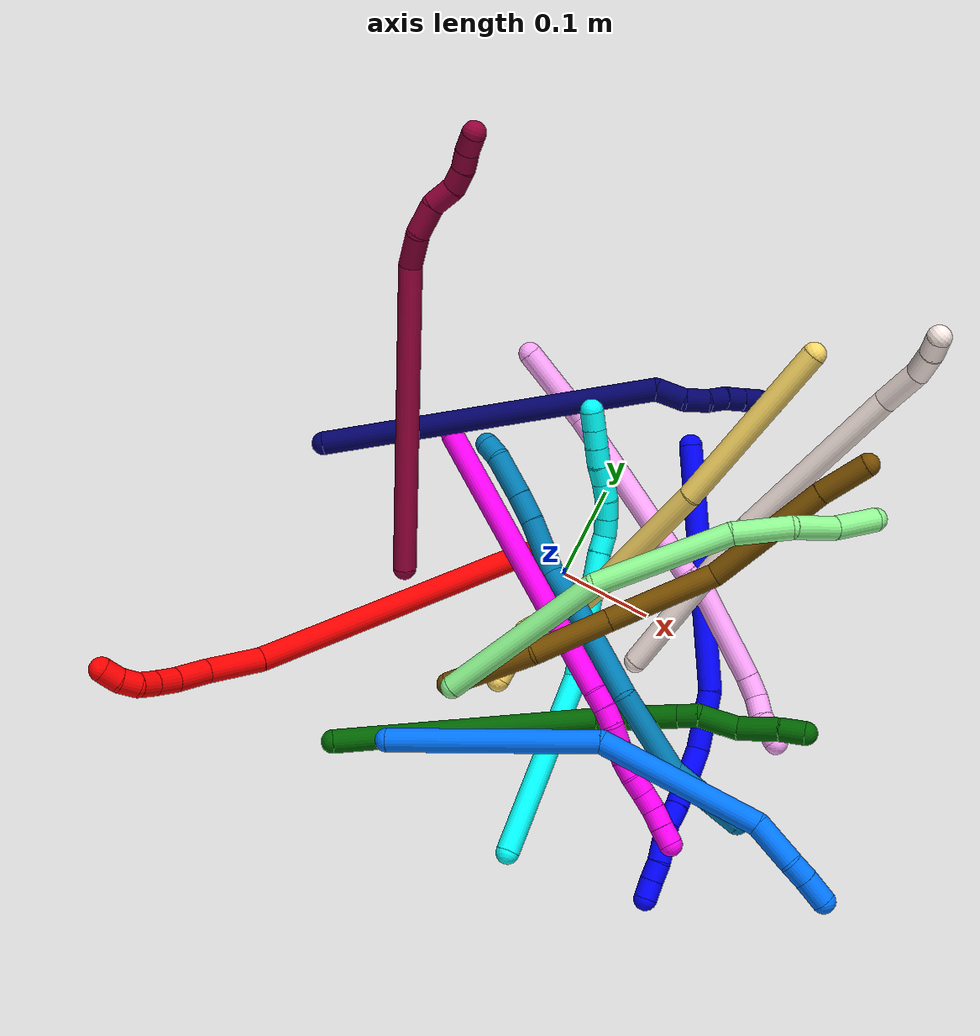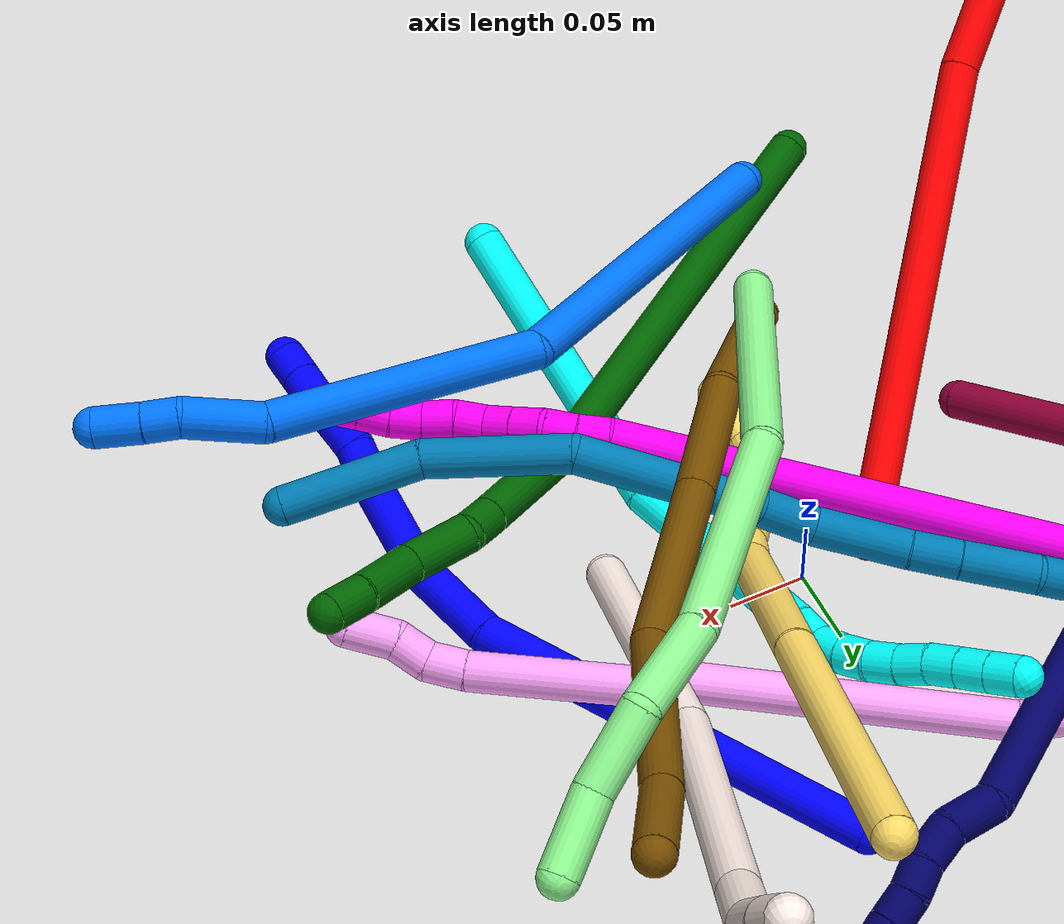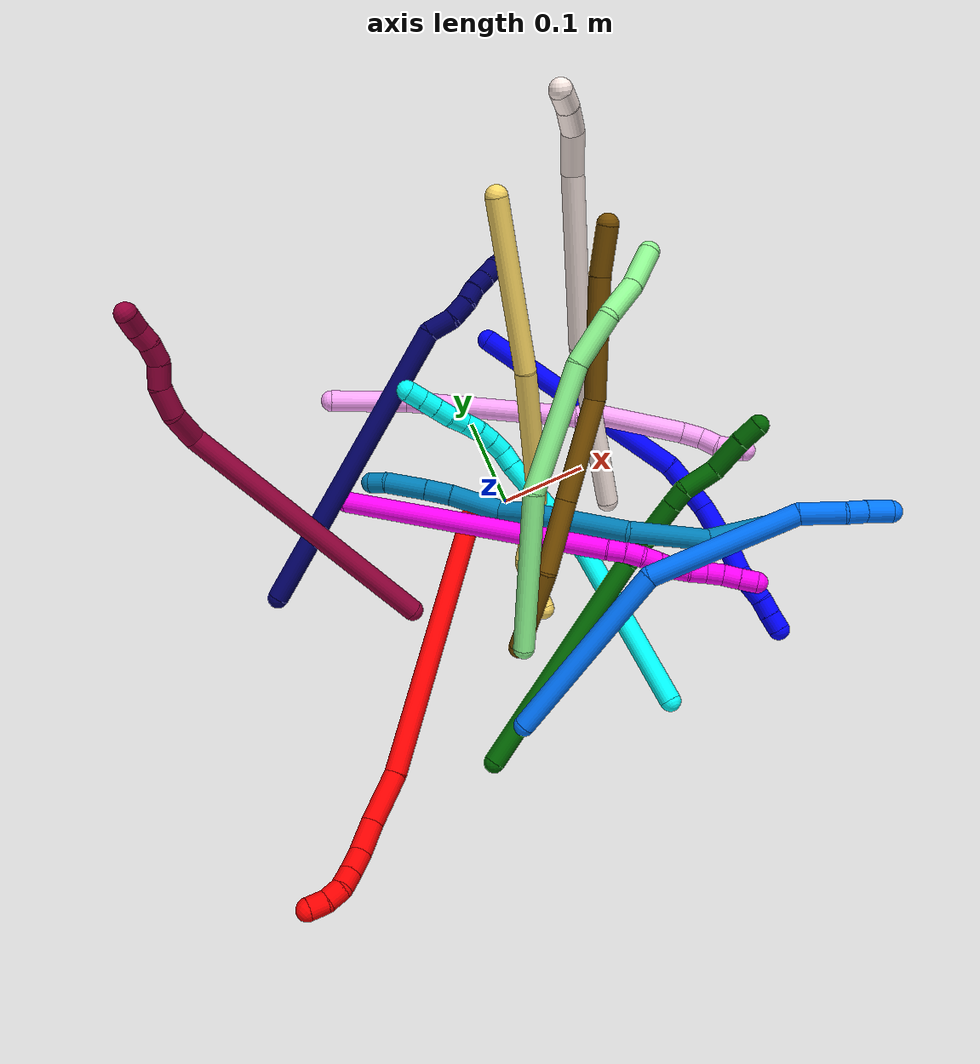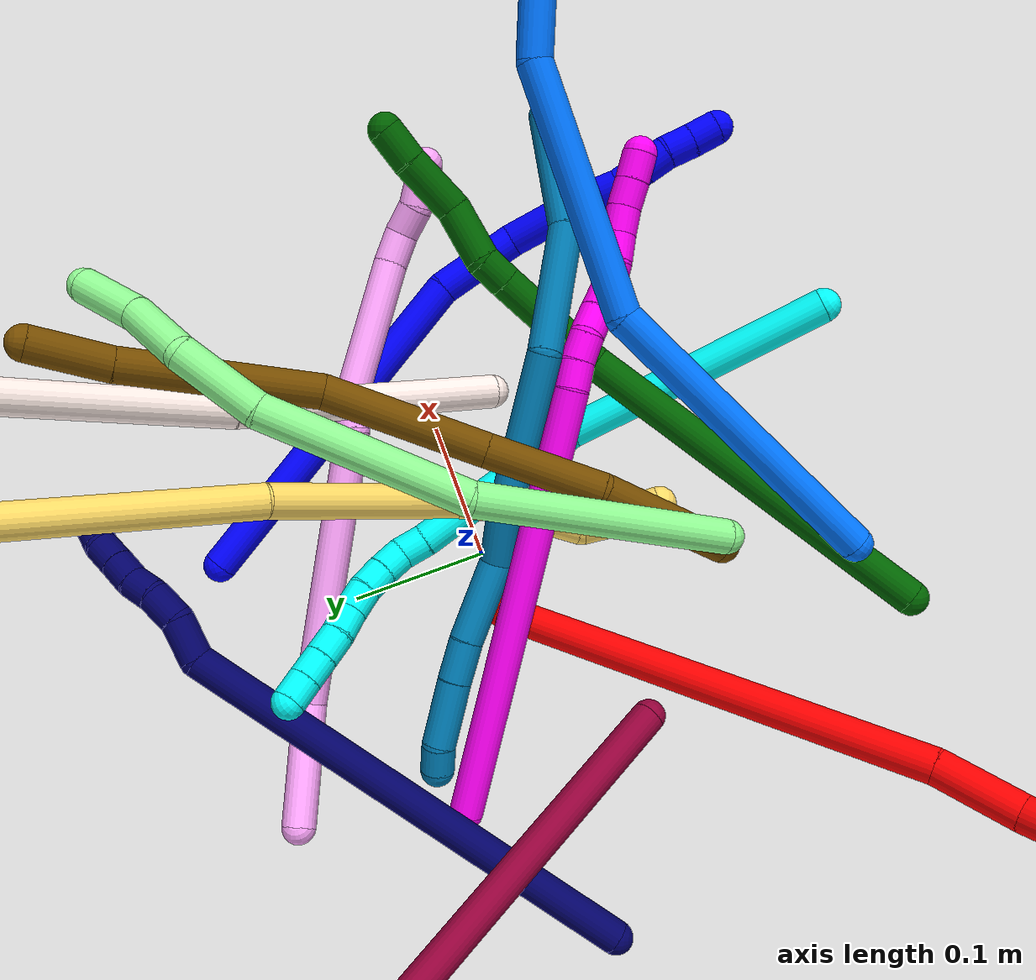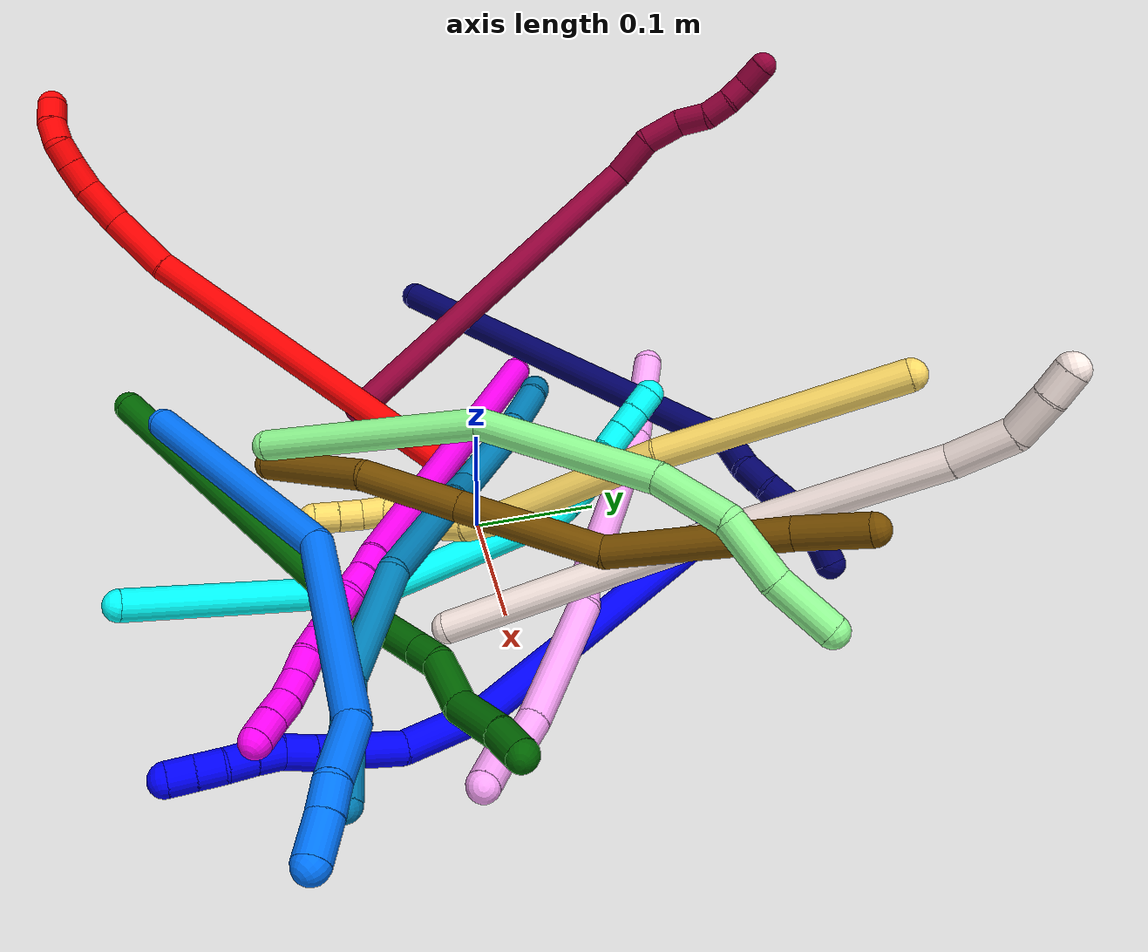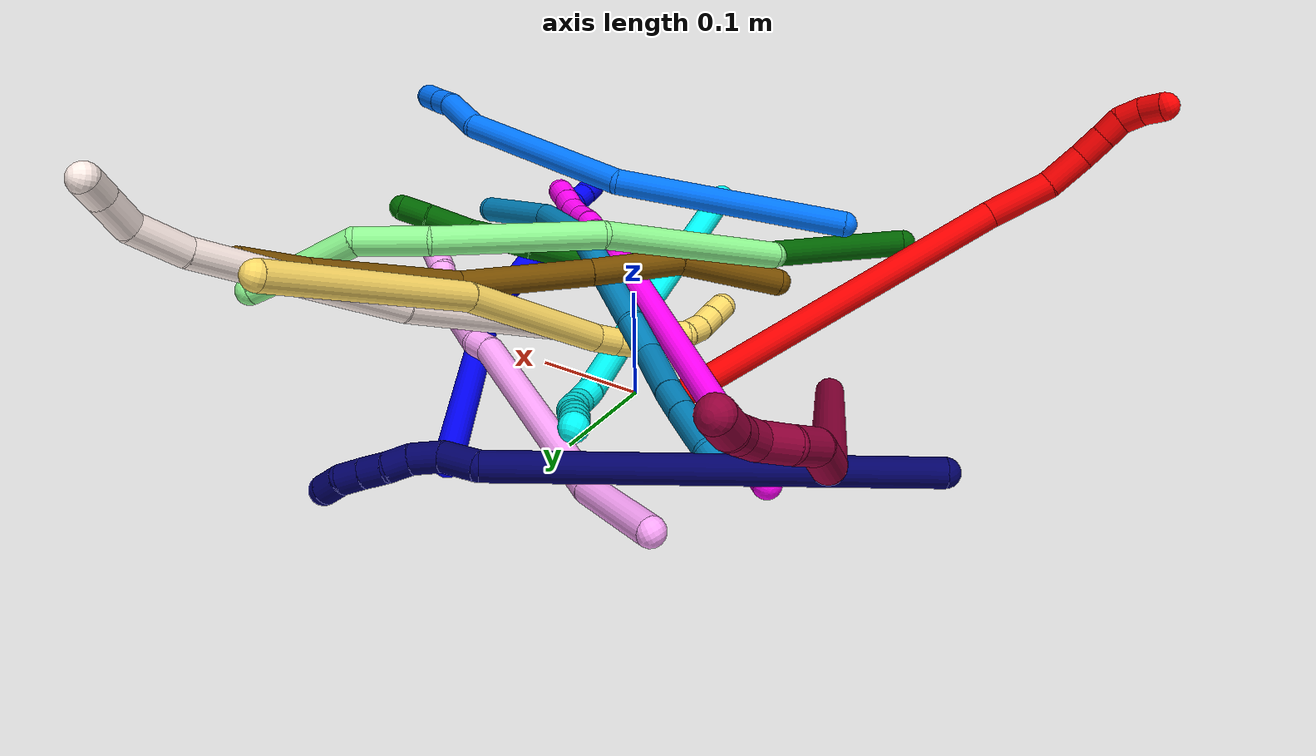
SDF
<sdf version="1.7">
 <world name="default">
  <plugin name="TubeGeneratorPlugin" filename="libtube_generator_plugin.so"/>
  <model name="photoneo_s_sensor">
   <static>1</static>
   <pose>0 0 2 1.57079 1.57079 3.14159</pose>
   <link name="link">
    <inertial><mass>0.1</mass></inertial>
    <sensor name="sensor" type="depth">
     <update_rate>30</update_rate>
     <camera>
      <horizontal_fov>1.22</horizontal_fov>
      <image><width>1920</width><height>1200</height><format>B8G8R8</format></image>
      <clip><near>0.1</near><far>4</far></clip>
      <depth_camera><output>points</output></depth_camera>
     </camera>
     <plugin name="camera_plugin" filename="libgazebo_ros_depth_camera.so">
      <baseline>0.2</baseline>
      <alwaysOn>1</alwaysOn>
      <updateRate>0.0</updateRate>
      <cameraName>camera_ir</cameraName>
      <imageTopicName>/camera/color/image_raw</imageTopicName>
      <cameraInfoTopicName>/camera/color/camera_info</cameraInfoTopicName>
      <depthImageTopicName>/camera/depth/image_raw</depthImageTopicName>
      <depthImageCameraInfoTopicName>/camera/depth/camera_info</depthImageCameraInfoTopicName>
      <pointCloudTopicName>/camera/depth/points</pointCloudTopicName>
      <frameName>fr_optical</frameName>
      <pointCloudCutoff>0.1</pointCloudCutoff>
      <pointCloudCutoffMax>2.0</pointCloudCutoffMax>
      <distortionK1>0</distortionK1>
      <distortionK2>0</distortionK2>
      <distortionK3>0</distortionK3>
      <distortionT1>0</distortionT1>
      <distortionT2>0</distortionT2>
      <CxPrime>0</CxPrime>
      <Cx>0</Cx>
      <Cy>0</Cy>
      <focalLength>0</focalLength>
      <hackBaseline>0</hackBaseline>
     </plugin>
    </sensor>
   </link>
  </model>
  <gravity>0 0 -9.8</gravity>
  <magnetic_field>6e-06 2.3e-05 -4.2e-05</magnetic_field>
  <atmosphere type="adiabatic"/>
  <physics name="default_physics" default="0" type="ode">
   <max_step_size>0.003</max_step_size>
   <real_time_factor>1</real_time_factor>
   <real_time_update_rate>1000</real_time_update_rate>
   <max_contacts>10000</max_contacts>
   <ode>
    <solver>
     <type>quick</type>
     <iters>100</iters>
     <sor>1.3</sor>
     <use_dynamic_moi_rescaling>0</use_dynamic_moi_rescaling>
    </solver>
    <constraints>
     <contact_max_correcting_vel>0</contact_max_correcting_vel>
     <contact_surface_layer>0.001</contact_surface_layer>
     <cfm>0</cfm>
     <erp>0.2</erp>
    </constraints>
   </ode>
  </physics>
  <scene><ambient>0.4 0.4 0.4 1</ambient><background>0.7 0.7 0.7 1</background><shadows>0</shadows></scene>
  <audio><device>default</device></audio>
  <spherical_coordinates>
   <surface_model>EARTH_WGS84</surface_model>
   <latitude_deg>0</latitude_deg>
   <longitude_deg>0</longitude_deg>
   <elevation>0</elevation>
   <heading_deg>0</heading_deg>
  </spherical_coordinates>
  <model name="bin">
   <static>1</static>
   <link name="bottom">
    <collision name="collision-bottom">
     <pose>0 0 -0.01 0 -0 0</pose>
     <geometry><box><size>0.8 0.6 0.02</size></box></geometry>
     <surface>
      <friction><ode><mu>100</mu><mu2>100</mu2></ode></friction>
      <contact><collide_bitmask>65535</collide_bitmask></contact>
     </surface>
    </collision>
   </link>
   <link name="west_wall">
    <collision name="collision-west_wall">
     <pose>-0.41 0 0.1 0 -0 0</pose>
     <geometry><box><size>0.02 0.6 0.2</size></box></geometry>
     <surface>
      <friction><ode><mu>100</mu><mu2>100</mu2></ode></friction>
      <contact><collide_bitmask>65535</collide_bitmask></contact>
     </surface>
    </collision>
   </link>
   <link name="east_wall">
    <collision name="collision-east_wall">
     <pose>0.41 0 0.1 0 -0 0</pose>
     <geometry><box><size>0.02 0.6 0.2</size></box></geometry>
     <surface>
      <friction><ode><mu>100</mu><mu2>100</mu2></ode></friction>
      <contact><collide_bitmask>65535</collide_bitmask></contact>
     </surface>
    </collision>
   </link>
   <link name="south_wall">
    <collision name="collision-south_wall">
     <pose>0 -0.31 0.1 0 -0 0</pose>
     <geometry><box><size>0.8 0.02 0.2</size></box></geometry>
     <surface>
      <friction><ode><mu>100</mu><mu2>100</mu2></ode></friction>
      <contact><collide_bitmask>65535</collide_bitmask></contact>
     </surface>
    </collision>
   </link>
   <link name="north_wall">
    <collision name="collision-north_wall">
     <pose>0 0.31 0.1 0 -0 0</pose>
     <geometry><box><size>0.8 0.02 0.2</size></box></geometry>
     <surface>
      <friction><ode><mu>100</mu><mu2>100</mu2></ode></friction>
      <contact><collide_bitmask>65535</collide_bitmask></contact>
     </surface>
    </collision>
   </link>
  </model>
  <model name="1">
   <static>0</static>
   <link name="1">
    <collision name="collision-cylinder-e_1_1_4">
     <pose>0.039754 -0.099244 0.07849 0.90164 0.30442 0.148236</pose>
     <geometry><cylinder><radius>0.0125</radius><length>0.265257</length></cylinder></geometry>
     <surface>
      <friction><ode><mu>1.16</mu><mu2>1.16</mu2><slip1>0</slip1><slip2>0</slip2></ode></friction>
      <contact><ode><kp>1e+06</kp><kd>1</kd><max_vel>0</max_vel><min_depth>0.001</min_depth></ode></contact>
     </surface>
    </collision>
    <visual name="visual-cylinder-e_1_1_4">
     <pose>0.039754 -0.099244 0.07849 0.90164 0.30442 0.148236</pose>
     <geometry><cylinder><radius>0.0125</radius><length>0.265257</length></cylinder></geometry>
     <material><ambient>0 0 1 1</ambient></material>
    </visual>
    <collision name="collision-cylinder-e_2_4_5">
     <pose>0.092423 -0.225521 0.167946 1.18543 0.416775 0.282927</pose>
     <geometry><cylinder><radius>0.0125</radius><length>0.063808</length></cylinder></geometry>
     <surface>
      <friction><ode><mu>1.16</mu><mu2>1.16</mu2><slip1>0</slip1><slip2>0</slip2></ode></friction>
      <contact><ode><kp>1e+06</kp><kd>1</kd><max_vel>0</max_vel><min_depth>0.001</min_depth></ode></contact>
     </surface>
    </collision>
    <visual name="visual-cylinder-e_2_4_5">
     <pose>0.092423 -0.225521 0.167946 1.18543 0.416775 0.282927</pose>
     <geometry><cylinder><radius>0.0125</radius><length>0.063808</length></cylinder></geometry>
     <material><ambient>0 0 1 1</ambient></material>
    </visual>
    <collision name="collision-cylinder-e_3_5_6">
     <pose>0.111017 -0.28537 0.182448 1.46348 0.17038 0.153082</pose>
     <geometry><cylinder><radius>0.0125</radius><length>0.066981</length></cylinder></geometry>
     <surface>
      <friction><ode><mu>1.16</mu><mu2>1.16</mu2><slip1>0</slip1><slip2>0</slip2></ode></friction>
      <contact><ode><kp>1e+06</kp><kd>1</kd><max_vel>0</max_vel><min_depth>0.001</min_depth></ode></contact>
     </surface>
    </collision>
    <visual name="visual-cylinder-e_3_5_6">
     <pose>0.111017 -0.28537 0.182448 1.46348 0.17038 0.153082</pose>
     <geometry><cylinder><radius>0.0125</radius><length>0.066981</length></cylinder></geometry>
     <material><ambient>0 0 1 1</ambient></material>
    </visual>
    <collision name="collision-cylinder-e_4_6_7">
     <pose>0.118943 -0.3294 0.185966 1.57229 0.197746 0.198039</pose>
     <geometry><cylinder><radius>0.0125</radius><length>0.022873</length></cylinder></geometry>
     <surface>
      <friction><ode><mu>1.16</mu><mu2>1.16</mu2><slip1>0</slip1><slip2>0</slip2></ode></friction>
      <contact><ode><kp>1e+06</kp><kd>1</kd><max_vel>0</max_vel><min_depth>0.001</min_depth></ode></contact>
     </surface>
    </collision>
    <visual name="visual-cylinder-e_4_6_7">
     <pose>0.118943 -0.3294 0.185966 1.57229 0.197746 0.198039</pose>
     <geometry><cylinder><radius>0.0125</radius><length>0.022873</length></cylinder></geometry>
     <material><ambient>0 0 1 1</ambient></material>
    </visual>
    <collision name="collision-cylinder-e_5_7_8">
     <pose>0.123179 -0.350255 0.188508 1.31149 0.196833 0.151625</pose>
     <geometry><cylinder><radius>0.0125</radius><length>0.020344</length></cylinder></geometry>
     <surface>
      <friction><ode><mu>1.16</mu><mu2>1.16</mu2><slip1>0</slip1><slip2>0</slip2></ode></friction>
      <contact><ode><kp>1e+06</kp><kd>1</kd><max_vel>0</max_vel><min_depth>0.001</min_depth></ode></contact>
     </surface>
    </collision>
    <visual name="visual-cylinder-e_5_7_8">
     <pose>0.123179 -0.350255 0.188508 1.31149 0.196833 0.151625</pose>
     <geometry><cylinder><radius>0.0125</radius><length>0.020344</length></cylinder></geometry>
     <material><ambient>0 0 1 1</ambient></material>
    </visual>
    <collision name="collision-cylinder-e_6_8_9">
     <pose>0.12788 -0.36939 0.193927 1.27799 0.267009 0.198911</pose>
     <geometry><cylinder><radius>0.0125</radius><length>0.020557</length></cylinder></geometry>
     <surface>
      <friction><ode><mu>1.16</mu><mu2>1.16</mu2><slip1>0</slip1><slip2>0</slip2></ode></friction>
      <contact><ode><kp>1e+06</kp><kd>1</kd><max_vel>0</max_vel><min_depth>0.001</min_depth></ode></contact>
     </surface>
    </collision>
    <visual name="visual-cylinder-e_6_8_9">
     <pose>0.12788 -0.36939 0.193927 1.27799 0.267009 0.198911</pose>
     <geometry><cylinder><radius>0.0125</radius><length>0.020557</length></cylinder></geometry>
     <material><ambient>0 0 1 1</ambient></material>
    </visual>
    <collision name="collision-cylinder-e_7_9_10">
     <pose>0.134894 -0.387782 0.198489 1.38206 0.443345 0.368573</pose>
     <geometry><cylinder><radius>0.0125</radius><length>0.020061</length></cylinder></geometry>
     <surface>
      <friction><ode><mu>1.16</mu><mu2>1.16</mu2><slip1>0</slip1><slip2>0</slip2></ode></friction>
      <contact><ode><kp>1e+06</kp><kd>1</kd><max_vel>0</max_vel><min_depth>0.001</min_depth></ode></contact>
     </surface>
    </collision>
    <visual name="visual-cylinder-e_7_9_10">
     <pose>0.134894 -0.387782 0.198489 1.38206 0.443345 0.368573</pose>
     <geometry><cylinder><radius>0.0125</radius><length>0.020061</length></cylinder></geometry>
     <material><ambient>0 0 1 1</ambient></material>
    </visual>
    <collision name="collision-cylinder-e_8_10_2">
     <pose>0.14294 -0.405804 0.20218 1.3559 0.381264 0.308331</pose>
     <geometry><cylinder><radius>0.0125</radius><length>0.020118</length></cylinder></geometry>
     <surface>
      <friction><ode><mu>1.16</mu><mu2>1.16</mu2><slip1>0</slip1><slip2>0</slip2></ode></friction>
      <contact><ode><kp>1e+06</kp><kd>1</kd><max_vel>0</max_vel><min_depth>0.001</min_depth></ode></contact>
     </surface>
    </collision>
    <visual name="visual-cylinder-e_8_10_2">
     <pose>0.14294 -0.405804 0.20218 1.3559 0.381264 0.308331</pose>
     <geometry><cylinder><radius>0.0125</radius><length>0.020118</length></cylinder></geometry>
     <material><ambient>0 0 1 1</ambient></material>
    </visual>
    <collision name="collision-sphere-2">
     <pose>0.146683 -0.414926 0.204171 0 -0 0</pose>
     <geometry><sphere><radius>0.0125</radius></sphere></geometry>
     <surface>
      <friction><ode><mu>1.16</mu><mu2>1.16</mu2><slip1>0</slip1><slip2>0</slip2></ode></friction>
      <contact><ode><kp>1e+06</kp><kd>1</kd><max_vel>0</max_vel><min_depth>0.001</min_depth></ode></contact>
     </surface>
    </collision>
    <visual name="visual-sphere-2">
     <pose>0.146683 -0.414926 0.204171 0 -0 0</pose>
     <geometry><sphere><radius>0.0125</radius></sphere></geometry>
     <material><ambient>0 0 1 1</ambient></material>
    </visual>
    <collision name="collision-sphere-10">
     <pose>0.139197 -0.396682 0.200189 0 -0 0</pose>
     <geometry><sphere><radius>0.0125</radius></sphere></geometry>
     <surface>
      <friction><ode><mu>1.16</mu><mu2>1.16</mu2><slip1>0</slip1><slip2>0</slip2></ode></friction>
      <contact><ode><kp>1e+06</kp><kd>1</kd><max_vel>0</max_vel><min_depth>0.001</min_depth></ode></contact>
     </surface>
    </collision>
    <visual name="visual-sphere-10">
     <pose>0.139197 -0.396682 0.200189 0 -0 0</pose>
     <geometry><sphere><radius>0.0125</radius></sphere></geometry>
     <material><ambient>0 0 1 1</ambient></material>
    </visual>
    <collision name="collision-sphere-9">
     <pose>0.130592 -0.378882 0.196789 0 -0 0</pose>
     <geometry><sphere><radius>0.0125</radius></sphere></geometry>
     <surface>
      <friction><ode><mu>1.16</mu><mu2>1.16</mu2><slip1>0</slip1><slip2>0</slip2></ode></friction>
      <contact><ode><kp>1e+06</kp><kd>1</kd><max_vel>0</max_vel><min_depth>0.001</min_depth></ode></contact>
     </surface>
    </collision>
    <visual name="visual-sphere-9">
     <pose>0.130592 -0.378882 0.196789 0 -0 0</pose>
     <geometry><sphere><radius>0.0125</radius></sphere></geometry>
     <material><ambient>0 0 1 1</ambient></material>
    </visual>
    <collision name="collision-sphere-4">
     <pose>0.079508 -0.198487 0.15698 0 -0 0</pose>
     <geometry><sphere><radius>0.0125</radius></sphere></geometry>
     <surface>
      <friction><ode><mu>1.16</mu><mu2>1.16</mu2><slip1>0</slip1><slip2>0</slip2></ode></friction>
      <contact><ode><kp>1e+06</kp><kd>1</kd><max_vel>0</max_vel><min_depth>0.001</min_depth></ode></contact>
     </surface>
    </collision>
    <visual name="visual-sphere-4">
     <pose>0.079508 -0.198487 0.15698 0 -0 0</pose>
     <geometry><sphere><radius>0.0125</radius></sphere></geometry>
     <material><ambient>0 0 1 1</ambient></material>
    </visual>
    <collision name="collision-sphere-1">
     <geometry><sphere><radius>0.0125</radius></sphere></geometry>
     <surface>
      <friction><ode><mu>1.16</mu><mu2>1.16</mu2><slip1>0</slip1><slip2>0</slip2></ode></friction>
      <contact><ode><kp>1e+06</kp><kd>1</kd><max_vel>0</max_vel><min_depth>0.001</min_depth></ode></contact>
     </surface>
    </collision>
    <visual name="visual-sphere-1">
     <geometry><sphere><radius>0.0125</radius></sphere></geometry>
     <material><ambient>0 0 1 1</ambient></material>
    </visual>
    <collision name="collision-sphere-8">
     <pose>0.125168 -0.359897 0.191065 0 -0 0</pose>
     <geometry><sphere><radius>0.0125</radius></sphere></geometry>
     <surface>
      <friction><ode><mu>1.16</mu><mu2>1.16</mu2><slip1>0</slip1><slip2>0</slip2></ode></friction>
      <contact><ode><kp>1e+06</kp><kd>1</kd><max_vel>0</max_vel><min_depth>0.001</min_depth></ode></contact>
     </surface>
    </collision>
    <visual name="visual-sphere-8">
     <pose>0.125168 -0.359897 0.191065 0 -0 0</pose>
     <geometry><sphere><radius>0.0125</radius></sphere></geometry>
     <material><ambient>0 0 1 1</ambient></material>
    </visual>
    <collision name="collision-sphere-5">
     <pose>0.105339 -0.252554 0.178912 0 -0 0</pose>
     <geometry><sphere><radius>0.0125</radius></sphere></geometry>
     <surface>
      <friction><ode><mu>1.16</mu><mu2>1.16</mu2><slip1>0</slip1><slip2>0</slip2></ode></friction>
      <contact><ode><kp>1e+06</kp><kd>1</kd><max_vel>0</max_vel><min_depth>0.001</min_depth></ode></contact>
     </surface>
    </collision>
    <visual name="visual-sphere-5">
     <pose>0.105339 -0.252554 0.178912 0 -0 0</pose>
     <geometry><sphere><radius>0.0125</radius></sphere></geometry>
     <material><ambient>0 0 1 1</ambient></material>
    </visual>
    <collision name="collision-sphere-6">
     <pose>0.116696 -0.318186 0.185983 0 -0 0</pose>
     <geometry><sphere><radius>0.0125</radius></sphere></geometry>
     <surface>
      <friction><ode><mu>1.16</mu><mu2>1.16</mu2><slip1>0</slip1><slip2>0</slip2></ode></friction>
      <contact><ode><kp>1e+06</kp><kd>1</kd><max_vel>0</max_vel><min_depth>0.001</min_depth></ode></contact>
     </surface>
    </collision>
    <visual name="visual-sphere-6">
     <pose>0.116696 -0.318186 0.185983 0 -0 0</pose>
     <geometry><sphere><radius>0.0125</radius></sphere></geometry>
     <material><ambient>0 0 1 1</ambient></material>
    </visual>
    <collision name="collision-sphere-7">
     <pose>0.121189 -0.340613 0.18595 0 -0 0</pose>
     <geometry><sphere><radius>0.0125</radius></sphere></geometry>
     <surface>
      <friction><ode><mu>1.16</mu><mu2>1.16</mu2><slip1>0</slip1><slip2>0</slip2></ode></friction>
      <contact><ode><kp>1e+06</kp><kd>1</kd><max_vel>0</max_vel><min_depth>0.001</min_depth></ode></contact>
     </surface>
    </collision>
    <visual name="visual-sphere-7">
     <pose>0.121189 -0.340613 0.18595 0 -0 0</pose>
     <geometry><sphere><radius>0.0125</radius></sphere></geometry>
     <material><ambient>0 0 1 1</ambient></material>
    </visual>
    <inertial>
     <pose>0.074631 -0.196053 0.127763 0 -0 0</pose>
     <mass>0.5</mass>
     <inertia>
      <ixx>0.001777</ixx>
      <ixy>0</ixy>
      <ixz>0</ixz>
      <iyy>0.001232</iyy>
      <iyz>0</iyz>
      <izz>0.000756</izz>
     </inertia>
    </inertial>
   </link>
   <pose>0.058605 0.185474 0.011497 -1.9445 1.01314 -1.98854</pose>
  </model>
  <model name="2">
   <static>0</static>
   <link name="2">
    <collision name="collision-cylinder-e_1_1_4">
     <pose>-0.060789 -0.037595 0.142839 0.257364 -0.390436 -0.051162</pose>
     <geometry><cylinder><radius>0.0125</radius><length>0.319448</length></cylinder></geometry>
     <surface>
      <friction><ode><mu>1.16</mu><mu2>1.16</mu2><slip1>0</slip1><slip2>0</slip2></ode></friction>
      <contact><ode><kp>1e+06</kp><kd>1</kd><max_vel>0</max_vel><min_depth>0.001</min_depth></ode></contact>
     </surface>
    </collision>
    <visual name="visual-cylinder-e_1_1_4">
     <pose>-0.060789 -0.037595 0.142839 0.257364 -0.390436 -0.051162</pose>
     <geometry><cylinder><radius>0.0125</radius><length>0.319448</length></cylinder></geometry>
     <material><ambient>1 0 0 1</ambient></material>
    </visual>
    <collision name="collision-cylinder-e_2_4_5">
     <pose>-0.128835 -0.079797 0.313423 0.164524 -0.252479 -0.020927</pose>
     <geometry><cylinder><radius>0.0125</radius><length>0.058092</length></cylinder></geometry>
     <surface>
      <friction><ode><mu>1.16</mu><mu2>1.16</mu2><slip1>0</slip1><slip2>0</slip2></ode></friction>
      <contact><ode><kp>1e+06</kp><kd>1</kd><max_vel>0</max_vel><min_depth>0.001</min_depth></ode></contact>
     </surface>
    </collision>
    <visual name="visual-cylinder-e_2_4_5">
     <pose>-0.128835 -0.079797 0.313423 0.164524 -0.252479 -0.020927</pose>
     <geometry><cylinder><radius>0.0125</radius><length>0.058092</length></cylinder></geometry>
     <material><ambient>1 0 0 1</ambient></material>
    </visual>
    <collision name="collision-cylinder-e_3_5_6">
     <pose>-0.138553 -0.091341 0.358173 0.387378 -0.133281 -0.02618</pose>
     <geometry><cylinder><radius>0.0125</radius><length>0.037058</length></cylinder></geometry>
     <surface>
      <friction><ode><mu>1.16</mu><mu2>1.16</mu2><slip1>0</slip1><slip2>0</slip2></ode></friction>
      <contact><ode><kp>1e+06</kp><kd>1</kd><max_vel>0</max_vel><min_depth>0.001</min_depth></ode></contact>
     </surface>
    </collision>
    <visual name="visual-cylinder-e_3_5_6">
     <pose>-0.138553 -0.091341 0.358173 0.387378 -0.133281 -0.02618</pose>
     <geometry><cylinder><radius>0.0125</radius><length>0.037058</length></cylinder></geometry>
     <material><ambient>1 0 0 1</ambient></material>
    </visual>
    <collision name="collision-cylinder-e_4_6_7">
     <pose>-0.140973 -0.103192 0.386817 0.39944 0.003361 0.00068</pose>
     <geometry><cylinder><radius>0.0125</radius><length>0.02527</length></cylinder></geometry>
     <surface>
      <friction><ode><mu>1.16</mu><mu2>1.16</mu2><slip1>0</slip1><slip2>0</slip2></ode></friction>
      <contact><ode><kp>1e+06</kp><kd>1</kd><max_vel>0</max_vel><min_depth>0.001</min_depth></ode></contact>
     </surface>
    </collision>
    <visual name="visual-cylinder-e_4_6_7">
     <pose>-0.140973 -0.103192 0.386817 0.39944 0.003361 0.00068</pose>
     <geometry><cylinder><radius>0.0125</radius><length>0.02527</length></cylinder></geometry>
     <material><ambient>1 0 0 1</ambient></material>
    </visual>
    <collision name="collision-cylinder-e_5_7_8">
     <pose>-0.140232 -0.112054 0.407679 0.404546 0.069505 0.014259</pose>
     <geometry><cylinder><radius>0.0125</radius><length>0.020111</length></cylinder></geometry>
     <surface>
      <friction><ode><mu>1.16</mu><mu2>1.16</mu2><slip1>0</slip1><slip2>0</slip2></ode></friction>
      <contact><ode><kp>1e+06</kp><kd>1</kd><max_vel>0</max_vel><min_depth>0.001</min_depth></ode></contact>
     </surface>
    </collision>
    <visual name="visual-cylinder-e_5_7_8">
     <pose>-0.140232 -0.112054 0.407679 0.404546 0.069505 0.014259</pose>
     <geometry><cylinder><radius>0.0125</radius><length>0.020111</length></cylinder></geometry>
     <material><ambient>1 0 0 1</ambient></material>
    </visual>
    <collision name="collision-cylinder-e_6_8_9">
     <pose>-0.13784 -0.115918 0.426763 -0.008617 0.170063 -0.000735</pose>
     <geometry><cylinder><radius>0.0125</radius><length>0.020016</length></cylinder></geometry>
     <surface>
      <friction><ode><mu>1.16</mu><mu2>1.16</mu2><slip1>0</slip1><slip2>0</slip2></ode></friction>
      <contact><ode><kp>1e+06</kp><kd>1</kd><max_vel>0</max_vel><min_depth>0.001</min_depth></ode></contact>
     </surface>
    </collision>
    <visual name="visual-cylinder-e_6_8_9">
     <pose>-0.13784 -0.115918 0.426763 -0.008617 0.170063 -0.000735</pose>
     <geometry><cylinder><radius>0.0125</radius><length>0.020016</length></cylinder></geometry>
     <material><ambient>1 0 0 1</ambient></material>
    </visual>
    <collision name="collision-cylinder-e_7_9_2">
     <pose>-0.13264 -0.113466 0.44569 -0.255396 0.358182 -0.046479</pose>
     <geometry><cylinder><radius>0.0125</radius><length>0.020005</length></cylinder></geometry>
     <surface>
      <friction><ode><mu>1.16</mu><mu2>1.16</mu2><slip1>0</slip1><slip2>0</slip2></ode></friction>
      <contact><ode><kp>1e+06</kp><kd>1</kd><max_vel>0</max_vel><min_depth>0.001</min_depth></ode></contact>
     </surface>
    </collision>
    <visual name="visual-cylinder-e_7_9_2">
     <pose>-0.13264 -0.113466 0.44569 -0.255396 0.358182 -0.046479</pose>
     <geometry><cylinder><radius>0.0125</radius><length>0.020005</length></cylinder></geometry>
     <material><ambient>1 0 0 1</ambient></material>
    </visual>
    <collision name="collision-sphere-2">
     <pose>-0.129133 -0.111099 0.454754 0 -0 0</pose>
     <geometry><sphere><radius>0.0125</radius></sphere></geometry>
     <surface>
      <friction><ode><mu>1.16</mu><mu2>1.16</mu2><slip1>0</slip1><slip2>0</slip2></ode></friction>
      <contact><ode><kp>1e+06</kp><kd>1</kd><max_vel>0</max_vel><min_depth>0.001</min_depth></ode></contact>
     </surface>
    </collision>
    <visual name="visual-sphere-2">
     <pose>-0.129133 -0.111099 0.454754 0 -0 0</pose>
     <geometry><sphere><radius>0.0125</radius></sphere></geometry>
     <material><ambient>1 0 0 1</ambient></material>
    </visual>
    <collision name="collision-sphere-9">
     <pose>-0.136146 -0.115833 0.436626 0 -0 0</pose>
     <geometry><sphere><radius>0.0125</radius></sphere></geometry>
     <surface>
      <friction><ode><mu>1.16</mu><mu2>1.16</mu2><slip1>0</slip1><slip2>0</slip2></ode></friction>
      <contact><ode><kp>1e+06</kp><kd>1</kd><max_vel>0</max_vel><min_depth>0.001</min_depth></ode></contact>
     </surface>
    </collision>
    <visual name="visual-sphere-9">
     <pose>-0.136146 -0.115833 0.436626 0 -0 0</pose>
     <geometry><sphere><radius>0.0125</radius></sphere></geometry>
     <material><ambient>1 0 0 1</ambient></material>
    </visual>
    <collision name="collision-sphere-4">
     <pose>-0.121579 -0.075191 0.285678 0 -0 0</pose>
     <geometry><sphere><radius>0.0125</radius></sphere></geometry>
     <surface>
      <friction><ode><mu>1.16</mu><mu2>1.16</mu2><slip1>0</slip1><slip2>0</slip2></ode></friction>
      <contact><ode><kp>1e+06</kp><kd>1</kd><max_vel>0</max_vel><min_depth>0.001</min_depth></ode></contact>
     </surface>
    </collision>
    <visual name="visual-sphere-4">
     <pose>-0.121579 -0.075191 0.285678 0 -0 0</pose>
     <geometry><sphere><radius>0.0125</radius></sphere></geometry>
     <material><ambient>1 0 0 1</ambient></material>
    </visual>
    <collision name="collision-sphere-1">
     <geometry><sphere><radius>0.0125</radius></sphere></geometry>
     <surface>
      <friction><ode><mu>1.16</mu><mu2>1.16</mu2><slip1>0</slip1><slip2>0</slip2></ode></friction>
      <contact><ode><kp>1e+06</kp><kd>1</kd><max_vel>0</max_vel><min_depth>0.001</min_depth></ode></contact>
     </surface>
    </collision>
    <visual name="visual-sphere-1">
     <geometry><sphere><radius>0.0125</radius></sphere></geometry>
     <material><ambient>1 0 0 1</ambient></material>
    </visual>
    <collision name="collision-sphere-8">
     <pose>-0.139534 -0.116003 0.4169 0 -0 0</pose>
     <geometry><sphere><radius>0.0125</radius></sphere></geometry>
     <surface>
      <friction><ode><mu>1.16</mu><mu2>1.16</mu2><slip1>0</slip1><slip2>0</slip2></ode></friction>
      <contact><ode><kp>1e+06</kp><kd>1</kd><max_vel>0</max_vel><min_depth>0.001</min_depth></ode></contact>
     </surface>
    </collision>
    <visual name="visual-sphere-8">
     <pose>-0.139534 -0.116003 0.4169 0 -0 0</pose>
     <geometry><sphere><radius>0.0125</radius></sphere></geometry>
     <material><ambient>1 0 0 1</ambient></material>
    </visual>
    <collision name="collision-sphere-5">
     <pose>-0.136091 -0.084403 0.341168 0 -0 0</pose>
     <geometry><sphere><radius>0.0125</radius></sphere></geometry>
     <surface>
      <friction><ode><mu>1.16</mu><mu2>1.16</mu2><slip1>0</slip1><slip2>0</slip2></ode></friction>
      <contact><ode><kp>1e+06</kp><kd>1</kd><max_vel>0</max_vel><min_depth>0.001</min_depth></ode></contact>
     </surface>
    </collision>
    <visual name="visual-sphere-5">
     <pose>-0.136091 -0.084403 0.341168 0 -0 0</pose>
     <geometry><sphere><radius>0.0125</radius></sphere></geometry>
     <material><ambient>1 0 0 1</ambient></material>
    </visual>
    <collision name="collision-sphere-6">
     <pose>-0.141015 -0.098279 0.375177 0 -0 0</pose>
     <geometry><sphere><radius>0.0125</radius></sphere></geometry>
     <surface>
      <friction><ode><mu>1.16</mu><mu2>1.16</mu2><slip1>0</slip1><slip2>0</slip2></ode></friction>
      <contact><ode><kp>1e+06</kp><kd>1</kd><max_vel>0</max_vel><min_depth>0.001</min_depth></ode></contact>
     </surface>
    </collision>
    <visual name="visual-sphere-6">
     <pose>-0.141015 -0.098279 0.375177 0 -0 0</pose>
     <geometry><sphere><radius>0.0125</radius></sphere></geometry>
     <material><ambient>1 0 0 1</ambient></material>
    </visual>
    <collision name="collision-sphere-7">
     <pose>-0.14093 -0.108106 0.398457 0 -0 0</pose>
     <geometry><sphere><radius>0.0125</radius></sphere></geometry>
     <surface>
      <friction><ode><mu>1.16</mu><mu2>1.16</mu2><slip1>0</slip1><slip2>0</slip2></ode></friction>
      <contact><ode><kp>1e+06</kp><kd>1</kd><max_vel>0</max_vel><min_depth>0.001</min_depth></ode></contact>
     </surface>
    </collision>
    <visual name="visual-sphere-7">
     <pose>-0.14093 -0.108106 0.398457 0 -0 0</pose>
     <geometry><sphere><radius>0.0125</radius></sphere></geometry>
     <material><ambient>1 0 0 1</ambient></material>
    </visual>
    <inertial>
     <pose>-0.087666 -0.058963 0.225084 0 -0 0</pose>
     <mass>0.5</mass>
     <inertia>
      <ixx>0.002411</ixx>
      <ixy>0</ixy>
      <ixz>0</ixz>
      <iyy>0.002541</iyy>
      <iyz>0</iyz>
      <izz>0.001727</izz>
     </inertia>
    </inertial>
   </link>
   <pose>-0.046013 -0.000494 0.011492 -1.02007 -0.495702 1.66135</pose>
  </model>
  <model name="3">
   <static>0</static>
   <link name="3">
    <collision name="collision-cylinder-e_1_1_4">
     <pose>-0.0055 0.029108 -0.09682 -2.84955 -0.05435 0.365522</pose>
     <geometry><cylinder><radius>0.0125</radius><length>0.202501</length></cylinder></geometry>
     <surface>
      <friction><ode><mu>1.16</mu><mu2>1.16</mu2><slip1>0</slip1><slip2>0</slip2></ode></friction>
      <contact><ode><kp>1e+06</kp><kd>1</kd><max_vel>0</max_vel><min_depth>0.001</min_depth></ode></contact>
     </surface>
    </collision>
    <visual name="visual-cylinder-e_1_1_4">
     <pose>-0.0055 0.029108 -0.09682 -2.84955 -0.05435 0.365522</pose>
     <geometry><cylinder><radius>0.0125</radius><length>0.202501</length></cylinder></geometry>
     <material><ambient>0.003922 1 0.996078 1</ambient></material>
    </visual>
    <collision name="collision-cylinder-e_2_4_5">
     <pose>-0.032882 0.088092 -0.250668 -2.65902 -0.327622 1.18295</pose>
     <geometry><cylinder><radius>0.0125</radius><length>0.135995</length></cylinder></geometry>
     <surface>
      <friction><ode><mu>1.16</mu><mu2>1.16</mu2><slip1>0</slip1><slip2>0</slip2></ode></friction>
      <contact><ode><kp>1e+06</kp><kd>1</kd><max_vel>0</max_vel><min_depth>0.001</min_depth></ode></contact>
     </surface>
    </collision>
    <visual name="visual-cylinder-e_2_4_5">
     <pose>-0.032882 0.088092 -0.250668 -2.65902 -0.327622 1.18295</pose>
     <geometry><cylinder><radius>0.0125</radius><length>0.135995</length></cylinder></geometry>
     <material><ambient>0.003922 1 0.996078 1</ambient></material>
    </visual>
    <collision name="collision-cylinder-e_3_5_6">
     <pose>-0.057045 0.123144 -0.316121 -2.59071 -0.226885 0.766389</pose>
     <geometry><cylinder><radius>0.0125</radius><length>0.020294</length></cylinder></geometry>
     <surface>
      <friction><ode><mu>1.16</mu><mu2>1.16</mu2><slip1>0</slip1><slip2>0</slip2></ode></friction>
      <contact><ode><kp>1e+06</kp><kd>1</kd><max_vel>0</max_vel><min_depth>0.001</min_depth></ode></contact>
     </surface>
    </collision>
    <visual name="visual-cylinder-e_3_5_6">
     <pose>-0.057045 0.123144 -0.316121 -2.59071 -0.226885 0.766389</pose>
     <geometry><cylinder><radius>0.0125</radius><length>0.020294</length></cylinder></geometry>
     <material><ambient>0.003922 1 0.996078 1</ambient></material>
    </visual>
    <collision name="collision-cylinder-e_4_6_7">
     <pose>-0.064445 0.134758 -0.330315 -2.3015 -0.534467 1.09984</pose>
     <geometry><cylinder><radius>0.0125</radius><length>0.020092</length></cylinder></geometry>
     <surface>
      <friction><ode><mu>1.16</mu><mu2>1.16</mu2><slip1>0</slip1><slip2>0</slip2></ode></friction>
      <contact><ode><kp>1e+06</kp><kd>1</kd><max_vel>0</max_vel><min_depth>0.001</min_depth></ode></contact>
     </surface>
    </collision>
    <visual name="visual-cylinder-e_4_6_7">
     <pose>-0.064445 0.134758 -0.330315 -2.3015 -0.534467 1.09984</pose>
     <geometry><cylinder><radius>0.0125</radius><length>0.020092</length></cylinder></geometry>
     <material><ambient>0.003922 1 0.996078 1</ambient></material>
    </visual>
    <collision name="collision-cylinder-e_5_7_8">
     <pose>-0.075359 0.14743 -0.341385 -2.27535 -0.616371 1.20582</pose>
     <geometry><cylinder><radius>0.0125</radius><length>0.020056</length></cylinder></geometry>
     <surface>
      <friction><ode><mu>1.16</mu><mu2>1.16</mu2><slip1>0</slip1><slip2>0</slip2></ode></friction>
      <contact><ode><kp>1e+06</kp><kd>1</kd><max_vel>0</max_vel><min_depth>0.001</min_depth></ode></contact>
     </surface>
    </collision>
    <visual name="visual-cylinder-e_5_7_8">
     <pose>-0.075359 0.14743 -0.341385 -2.27535 -0.616371 1.20582</pose>
     <geometry><cylinder><radius>0.0125</radius><length>0.020056</length></cylinder></geometry>
     <material><ambient>0.003922 1 0.996078 1</ambient></material>
    </visual>
    <collision name="collision-cylinder-e_6_8_9">
     <pose>-0.088357 0.158835 -0.351543 -2.32503 -0.792802 1.53783</pose>
     <geometry><cylinder><radius>0.0125</radius><length>0.020219</length></cylinder></geometry>
     <surface>
      <friction><ode><mu>1.16</mu><mu2>1.16</mu2><slip1>0</slip1><slip2>0</slip2></ode></friction>
      <contact><ode><kp>1e+06</kp><kd>1</kd><max_vel>0</max_vel><min_depth>0.001</min_depth></ode></contact>
     </surface>
    </collision>
    <visual name="visual-cylinder-e_6_8_9">
     <pose>-0.088357 0.158835 -0.351543 -2.32503 -0.792802 1.53783</pose>
     <geometry><cylinder><radius>0.0125</radius><length>0.020219</length></cylinder></geometry>
     <material><ambient>0.003922 1 0.996078 1</ambient></material>
    </visual>
    <collision name="collision-cylinder-e_7_9_10">
     <pose>-0.103281 0.169444 -0.360055 -2.1625 -0.867277 1.43089</pose>
     <geometry><cylinder><radius>0.0125</radius><length>0.020254</length></cylinder></geometry>
     <surface>
      <friction><ode><mu>1.16</mu><mu2>1.16</mu2><slip1>0</slip1><slip2>0</slip2></ode></friction>
      <contact><ode><kp>1e+06</kp><kd>1</kd><max_vel>0</max_vel><min_depth>0.001</min_depth></ode></contact>
     </surface>
    </collision>
    <visual name="visual-cylinder-e_7_9_10">
     <pose>-0.103281 0.169444 -0.360055 -2.1625 -0.867277 1.43089</pose>
     <geometry><cylinder><radius>0.0125</radius><length>0.020254</length></cylinder></geometry>
     <material><ambient>0.003922 1 0.996078 1</ambient></material>
    </visual>
    <collision name="collision-cylinder-e_8_10_11">
     <pose>-0.117959 0.180644 -0.368581 -2.27261 -0.744667 1.39917</pose>
     <geometry><cylinder><radius>0.0125</radius><length>0.020525</length></cylinder></geometry>
     <surface>
      <friction><ode><mu>1.16</mu><mu2>1.16</mu2><slip1>0</slip1><slip2>0</slip2></ode></friction>
      <contact><ode><kp>1e+06</kp><kd>1</kd><max_vel>0</max_vel><min_depth>0.001</min_depth></ode></contact>
     </surface>
    </collision>
    <visual name="visual-cylinder-e_8_10_11">
     <pose>-0.117959 0.180644 -0.368581 -2.27261 -0.744667 1.39917</pose>
     <geometry><cylinder><radius>0.0125</radius><length>0.020525</length></cylinder></geometry>
     <material><ambient>0.003922 1 0.996078 1</ambient></material>
    </visual>
    <collision name="collision-cylinder-e_9_11_12">
     <pose>-0.131672 0.191936 -0.378335 -2.29407 -0.741702 1.42285</pose>
     <geometry><cylinder><radius>0.0125</radius><length>0.020008</length></cylinder></geometry>
     <surface>
      <friction><ode><mu>1.16</mu><mu2>1.16</mu2><slip1>0</slip1><slip2>0</slip2></ode></friction>
      <contact><ode><kp>1e+06</kp><kd>1</kd><max_vel>0</max_vel><min_depth>0.001</min_depth></ode></contact>
     </surface>
    </collision>
    <visual name="visual-cylinder-e_9_11_12">
     <pose>-0.131672 0.191936 -0.378335 -2.29407 -0.741702 1.42285</pose>
     <geometry><cylinder><radius>0.0125</radius><length>0.020008</length></cylinder></geometry>
     <material><ambient>0.003922 1 0.996078 1</ambient></material>
    </visual>
    <collision name="collision-cylinder-e_10_12_2">
     <pose>-0.145243 0.202992 -0.388076 -2.29207 -0.746821 1.42769</pose>
     <geometry><cylinder><radius>0.0125</radius><length>0.020057</length></cylinder></geometry>
     <surface>
      <friction><ode><mu>1.16</mu><mu2>1.16</mu2><slip1>0</slip1><slip2>0</slip2></ode></friction>
      <contact><ode><kp>1e+06</kp><kd>1</kd><max_vel>0</max_vel><min_depth>0.001</min_depth></ode></contact>
     </surface>
    </collision>
    <visual name="visual-cylinder-e_10_12_2">
     <pose>-0.145243 0.202992 -0.388076 -2.29207 -0.746821 1.42769</pose>
     <geometry><cylinder><radius>0.0125</radius><length>0.020057</length></cylinder></geometry>
     <material><ambient>0.003922 1 0.996078 1</ambient></material>
    </visual>
    <collision name="collision-sphere-2">
     <pose>-0.152055 0.208519 -0.392936 0 -0 0</pose>
     <geometry><sphere><radius>0.0125</radius></sphere></geometry>
     <surface>
      <friction><ode><mu>1.16</mu><mu2>1.16</mu2><slip1>0</slip1><slip2>0</slip2></ode></friction>
      <contact><ode><kp>1e+06</kp><kd>1</kd><max_vel>0</max_vel><min_depth>0.001</min_depth></ode></contact>
     </surface>
    </collision>
    <visual name="visual-sphere-2">
     <pose>-0.152055 0.208519 -0.392936 0 -0 0</pose>
     <geometry><sphere><radius>0.0125</radius></sphere></geometry>
     <material><ambient>0.003922 1 0.996078 1</ambient></material>
    </visual>
    <collision name="collision-sphere-12">
     <pose>-0.13843 0.197466 -0.383217 0 -0 0</pose>
     <geometry><sphere><radius>0.0125</radius></sphere></geometry>
     <surface>
      <friction><ode><mu>1.16</mu><mu2>1.16</mu2><slip1>0</slip1><slip2>0</slip2></ode></friction>
      <contact><ode><kp>1e+06</kp><kd>1</kd><max_vel>0</max_vel><min_depth>0.001</min_depth></ode></contact>
     </surface>
    </collision>
    <visual name="visual-sphere-12">
     <pose>-0.13843 0.197466 -0.383217 0 -0 0</pose>
     <geometry><sphere><radius>0.0125</radius></sphere></geometry>
     <material><ambient>0.003922 1 0.996078 1</ambient></material>
    </visual>
    <collision name="collision-sphere-11">
     <pose>-0.124914 0.186407 -0.373453 0 -0 0</pose>
     <geometry><sphere><radius>0.0125</radius></sphere></geometry>
     <surface>
      <friction><ode><mu>1.16</mu><mu2>1.16</mu2><slip1>0</slip1><slip2>0</slip2></ode></friction>
      <contact><ode><kp>1e+06</kp><kd>1</kd><max_vel>0</max_vel><min_depth>0.001</min_depth></ode></contact>
     </surface>
    </collision>
    <visual name="visual-sphere-11">
     <pose>-0.124914 0.186407 -0.373453 0 -0 0</pose>
     <geometry><sphere><radius>0.0125</radius></sphere></geometry>
     <material><ambient>0.003922 1 0.996078 1</ambient></material>
    </visual>
    <collision name="collision-sphere-10">
     <pose>-0.111004 0.174881 -0.363709 0 -0 0</pose>
     <geometry><sphere><radius>0.0125</radius></sphere></geometry>
     <surface>
      <friction><ode><mu>1.16</mu><mu2>1.16</mu2><slip1>0</slip1><slip2>0</slip2></ode></friction>
      <contact><ode><kp>1e+06</kp><kd>1</kd><max_vel>0</max_vel><min_depth>0.001</min_depth></ode></contact>
     </surface>
    </collision>
    <visual name="visual-sphere-10">
     <pose>-0.111004 0.174881 -0.363709 0 -0 0</pose>
     <geometry><sphere><radius>0.0125</radius></sphere></geometry>
     <material><ambient>0.003922 1 0.996078 1</ambient></material>
    </visual>
    <collision name="collision-sphere-9">
     <pose>-0.095558 0.164006 -0.356401 0 -0 0</pose>
     <geometry><sphere><radius>0.0125</radius></sphere></geometry>
     <surface>
      <friction><ode><mu>1.16</mu><mu2>1.16</mu2><slip1>0</slip1><slip2>0</slip2></ode></friction>
      <contact><ode><kp>1e+06</kp><kd>1</kd><max_vel>0</max_vel><min_depth>0.001</min_depth></ode></contact>
     </surface>
    </collision>
    <visual name="visual-sphere-9">
     <pose>-0.095558 0.164006 -0.356401 0 -0 0</pose>
     <geometry><sphere><radius>0.0125</radius></sphere></geometry>
     <material><ambient>0.003922 1 0.996078 1</ambient></material>
    </visual>
    <collision name="collision-sphere-4">
     <pose>-0.011001 0.058216 -0.19364 0 -0 0</pose>
     <geometry><sphere><radius>0.0125</radius></sphere></geometry>
     <surface>
      <friction><ode><mu>1.16</mu><mu2>1.16</mu2><slip1>0</slip1><slip2>0</slip2></ode></friction>
      <contact><ode><kp>1e+06</kp><kd>1</kd><max_vel>0</max_vel><min_depth>0.001</min_depth></ode></contact>
     </surface>
    </collision>
    <visual name="visual-sphere-4">
     <pose>-0.011001 0.058216 -0.19364 0 -0 0</pose>
     <geometry><sphere><radius>0.0125</radius></sphere></geometry>
     <material><ambient>0.003922 1 0.996078 1</ambient></material>
    </visual>
    <collision name="collision-sphere-1">
     <geometry><sphere><radius>0.0125</radius></sphere></geometry>
     <surface>
      <friction><ode><mu>1.16</mu><mu2>1.16</mu2><slip1>0</slip1><slip2>0</slip2></ode></friction>
      <contact><ode><kp>1e+06</kp><kd>1</kd><max_vel>0</max_vel><min_depth>0.001</min_depth></ode></contact>
     </surface>
    </collision>
    <visual name="visual-sphere-1">
     <geometry><sphere><radius>0.0125</radius></sphere></geometry>
     <material><ambient>0.003922 1 0.996078 1</ambient></material>
    </visual>
    <collision name="collision-sphere-8">
     <pose>-0.081156 0.153664 -0.346684 0 -0 0</pose>
     <geometry><sphere><radius>0.0125</radius></sphere></geometry>
     <surface>
      <friction><ode><mu>1.16</mu><mu2>1.16</mu2><slip1>0</slip1><slip2>0</slip2></ode></friction>
      <contact><ode><kp>1e+06</kp><kd>1</kd><max_vel>0</max_vel><min_depth>0.001</min_depth></ode></contact>
     </surface>
    </collision>
    <visual name="visual-sphere-8">
     <pose>-0.081156 0.153664 -0.346684 0 -0 0</pose>
     <geometry><sphere><radius>0.0125</radius></sphere></geometry>
     <material><ambient>0.003922 1 0.996078 1</ambient></material>
    </visual>
    <collision name="collision-sphere-5">
     <pose>-0.054763 0.117969 -0.307697 0 -0 0</pose>
     <geometry><sphere><radius>0.0125</radius></sphere></geometry>
     <surface>
      <friction><ode><mu>1.16</mu><mu2>1.16</mu2><slip1>0</slip1><slip2>0</slip2></ode></friction>
      <contact><ode><kp>1e+06</kp><kd>1</kd><max_vel>0</max_vel><min_depth>0.001</min_depth></ode></contact>
     </surface>
    </collision>
    <visual name="visual-sphere-5">
     <pose>-0.054763 0.117969 -0.307697 0 -0 0</pose>
     <geometry><sphere><radius>0.0125</radius></sphere></geometry>
     <material><ambient>0.003922 1 0.996078 1</ambient></material>
    </visual>
    <collision name="collision-sphere-6">
     <pose>-0.059328 0.12832 -0.324546 0 -0 0</pose>
     <geometry><sphere><radius>0.0125</radius></sphere></geometry>
     <surface>
      <friction><ode><mu>1.16</mu><mu2>1.16</mu2><slip1>0</slip1><slip2>0</slip2></ode></friction>
      <contact><ode><kp>1e+06</kp><kd>1</kd><max_vel>0</max_vel><min_depth>0.001</min_depth></ode></contact>
     </surface>
    </collision>
    <visual name="visual-sphere-6">
     <pose>-0.059328 0.12832 -0.324546 0 -0 0</pose>
     <geometry><sphere><radius>0.0125</radius></sphere></geometry>
     <material><ambient>0.003922 1 0.996078 1</ambient></material>
    </visual>
    <collision name="collision-sphere-7">
     <pose>-0.069562 0.141195 -0.336085 0 -0 0</pose>
     <geometry><sphere><radius>0.0125</radius></sphere></geometry>
     <surface>
      <friction><ode><mu>1.16</mu><mu2>1.16</mu2><slip1>0</slip1><slip2>0</slip2></ode></friction>
      <contact><ode><kp>1e+06</kp><kd>1</kd><max_vel>0</max_vel><min_depth>0.001</min_depth></ode></contact>
     </surface>
    </collision>
    <visual name="visual-sphere-7">
     <pose>-0.069562 0.141195 -0.336085 0 -0 0</pose>
     <geometry><sphere><radius>0.0125</radius></sphere></geometry>
     <material><ambient>0.003922 1 0.996078 1</ambient></material>
    </visual>
    <inertial>
     <pose>-0.042793 0.088601 -0.221827 0 -0 0</pose>
     <mass>0.5</mass>
     <inertia>
      <ixx>0.001167</ixx>
      <ixy>0</ixy>
      <ixz>0</ixz>
      <iyy>-0.000199</iyy>
      <iyz>0</iyz>
      <izz>-0.000219</izz>
     </inertia>
    </inertial>
   </link>
   <pose>0.081779 -0.28851 0.064923 0.977005 0.331558 -0.056261</pose>
  </model>
  <model name="4">
   <static>0</static>
   <link name="4">
    <collision name="collision-cylinder-e_1_1_4">
     <pose>0.027061 -0.029236 -0.020743 2.18786 0.646628 1.15073</pose>
     <geometry><cylinder><radius>0.0125</radius><length>0.089828</length></cylinder></geometry>
     <surface>
      <friction><ode><mu>1.16</mu><mu2>1.16</mu2><slip1>0</slip1><slip2>0</slip2></ode></friction>
      <contact><ode><kp>1e+06</kp><kd>1</kd><max_vel>0</max_vel><min_depth>0.001</min_depth></ode></contact>
     </surface>
    </collision>
    <visual name="visual-cylinder-e_1_1_4">
     <pose>0.027061 -0.029236 -0.020743 2.18786 0.646628 1.15073</pose>
     <geometry><cylinder><radius>0.0125</radius><length>0.089828</length></cylinder></geometry>
     <material><ambient>1 0.65098 0.996078 1</ambient></material>
    </visual>
    <collision name="collision-cylinder-e_2_4_5">
     <pose>0.115415 -0.103348 -0.109199 2.55633 0.646395 1.67651</pose>
     <geometry><cylinder><radius>0.0125</radius><length>0.203529</length></cylinder></geometry>
     <surface>
      <friction><ode><mu>1.16</mu><mu2>1.16</mu2><slip1>0</slip1><slip2>0</slip2></ode></friction>
      <contact><ode><kp>1e+06</kp><kd>1</kd><max_vel>0</max_vel><min_depth>0.001</min_depth></ode></contact>
     </surface>
    </collision>
    <visual name="visual-cylinder-e_2_4_5">
     <pose>0.115415 -0.103348 -0.109199 2.55633 0.646395 1.67651</pose>
     <geometry><cylinder><radius>0.0125</radius><length>0.203529</length></cylinder></geometry>
     <material><ambient>1 0.65098 0.996078 1</ambient></material>
    </visual>
    <collision name="collision-cylinder-e_3_5_6">
     <pose>0.181151 -0.155236 -0.182867 2.27467 0.449837 0.918215</pose>
     <geometry><cylinder><radius>0.0125</radius><length>0.020429</length></cylinder></geometry>
     <surface>
      <friction><ode><mu>1.16</mu><mu2>1.16</mu2><slip1>0</slip1><slip2>0</slip2></ode></friction>
      <contact><ode><kp>1e+06</kp><kd>1</kd><max_vel>0</max_vel><min_depth>0.001</min_depth></ode></contact>
     </surface>
    </collision>
    <visual name="visual-cylinder-e_3_5_6">
     <pose>0.181151 -0.155236 -0.182867 2.27467 0.449837 0.918215</pose>
     <geometry><cylinder><radius>0.0125</radius><length>0.020429</length></cylinder></geometry>
     <material><ambient>1 0.65098 0.996078 1</ambient></material>
    </visual>
    <collision name="collision-cylinder-e_4_6_7">
     <pose>0.224902 -0.187853 -0.215377 2.37445 0.817122 1.64097</pose>
     <geometry><cylinder><radius>0.0125</radius><length>0.107818</length></cylinder></geometry>
     <surface>
      <friction><ode><mu>1.16</mu><mu2>1.16</mu2><slip1>0</slip1><slip2>0</slip2></ode></friction>
      <contact><ode><kp>1e+06</kp><kd>1</kd><max_vel>0</max_vel><min_depth>0.001</min_depth></ode></contact>
     </surface>
    </collision>
    <visual name="visual-cylinder-e_4_6_7">
     <pose>0.224902 -0.187853 -0.215377 2.37445 0.817122 1.64097</pose>
     <geometry><cylinder><radius>0.0125</radius><length>0.107818</length></cylinder></geometry>
     <material><ambient>1 0.65098 0.996078 1</ambient></material>
    </visual>
    <collision name="collision-cylinder-e_5_7_8">
     <pose>0.273475 -0.21771 -0.248915 2.59457 0.847915 2.0293</pose>
     <geometry><cylinder><radius>0.0125</radius><length>0.024709</length></cylinder></geometry>
     <surface>
      <friction><ode><mu>1.16</mu><mu2>1.16</mu2><slip1>0</slip1><slip2>0</slip2></ode></friction>
      <contact><ode><kp>1e+06</kp><kd>1</kd><max_vel>0</max_vel><min_depth>0.001</min_depth></ode></contact>
     </surface>
    </collision>
    <visual name="visual-cylinder-e_5_7_8">
     <pose>0.273475 -0.21771 -0.248915 2.59457 0.847915 2.0293</pose>
     <geometry><cylinder><radius>0.0125</radius><length>0.024709</length></cylinder></geometry>
     <material><ambient>1 0.65098 0.996078 1</ambient></material>
    </visual>
    <collision name="collision-cylinder-e_6_8_9">
     <pose>0.29034 -0.221708 -0.264193 -3.11113 0.741337 -3.06324</pose>
     <geometry><cylinder><radius>0.0125</radius><length>0.022509</length></cylinder></geometry>
     <surface>
      <friction><ode><mu>1.16</mu><mu2>1.16</mu2><slip1>0</slip1><slip2>0</slip2></ode></friction>
      <contact><ode><kp>1e+06</kp><kd>1</kd><max_vel>0</max_vel><min_depth>0.001</min_depth></ode></contact>
     </surface>
    </collision>
    <visual name="visual-cylinder-e_6_8_9">
     <pose>0.29034 -0.221708 -0.264193 -3.11113 0.741337 -3.06324</pose>
     <geometry><cylinder><radius>0.0125</radius><length>0.022509</length></cylinder></geometry>
     <material><ambient>1 0.65098 0.996078 1</ambient></material>
    </visual>
    <collision name="collision-cylinder-e_7_9_2">
     <pose>0.307447 -0.226246 -0.283878 2.74342 0.655901 2.07109</pose>
     <geometry><cylinder><radius>0.0125</radius><length>0.031178</length></cylinder></geometry>
     <surface>
      <friction><ode><mu>1.16</mu><mu2>1.16</mu2><slip1>0</slip1><slip2>0</slip2></ode></friction>
      <contact><ode><kp>1e+06</kp><kd>1</kd><max_vel>0</max_vel><min_depth>0.001</min_depth></ode></contact>
     </surface>
    </collision>
    <visual name="visual-cylinder-e_7_9_2">
     <pose>0.307447 -0.226246 -0.283878 2.74342 0.655901 2.07109</pose>
     <geometry><cylinder><radius>0.0125</radius><length>0.031178</length></cylinder></geometry>
     <material><ambient>1 0.65098 0.996078 1</ambient></material>
    </visual>
    <collision name="collision-sphere-2">
     <pose>0.316954 -0.231036 -0.295266 0 -0 0</pose>
     <geometry><sphere><radius>0.0125</radius></sphere></geometry>
     <surface>
      <friction><ode><mu>1.16</mu><mu2>1.16</mu2><slip1>0</slip1><slip2>0</slip2></ode></friction>
      <contact><ode><kp>1e+06</kp><kd>1</kd><max_vel>0</max_vel><min_depth>0.001</min_depth></ode></contact>
     </surface>
    </collision>
    <visual name="visual-sphere-2">
     <pose>0.316954 -0.231036 -0.295266 0 -0 0</pose>
     <geometry><sphere><radius>0.0125</radius></sphere></geometry>
     <material><ambient>1 0.65098 0.996078 1</ambient></material>
    </visual>
    <collision name="collision-sphere-9">
     <pose>0.297939 -0.221456 -0.27249 0 -0 0</pose>
     <geometry><sphere><radius>0.0125</radius></sphere></geometry>
     <surface>
      <friction><ode><mu>1.16</mu><mu2>1.16</mu2><slip1>0</slip1><slip2>0</slip2></ode></friction>
      <contact><ode><kp>1e+06</kp><kd>1</kd><max_vel>0</max_vel><min_depth>0.001</min_depth></ode></contact>
     </surface>
    </collision>
    <visual name="visual-sphere-9">
     <pose>0.297939 -0.221456 -0.27249 0 -0 0</pose>
     <geometry><sphere><radius>0.0125</radius></sphere></geometry>
     <material><ambient>1 0.65098 0.996078 1</ambient></material>
    </visual>
    <collision name="collision-sphere-4">
     <pose>0.054121 -0.058472 -0.041485 0 -0 0</pose>
     <geometry><sphere><radius>0.0125</radius></sphere></geometry>
     <surface>
      <friction><ode><mu>1.16</mu><mu2>1.16</mu2><slip1>0</slip1><slip2>0</slip2></ode></friction>
      <contact><ode><kp>1e+06</kp><kd>1</kd><max_vel>0</max_vel><min_depth>0.001</min_depth></ode></contact>
     </surface>
    </collision>
    <visual name="visual-sphere-4">
     <pose>0.054121 -0.058472 -0.041485 0 -0 0</pose>
     <geometry><sphere><radius>0.0125</radius></sphere></geometry>
     <material><ambient>1 0.65098 0.996078 1</ambient></material>
    </visual>
    <collision name="collision-sphere-1">
     <geometry><sphere><radius>0.0125</radius></sphere></geometry>
     <surface>
      <friction><ode><mu>1.16</mu><mu2>1.16</mu2><slip1>0</slip1><slip2>0</slip2></ode></friction>
      <contact><ode><kp>1e+06</kp><kd>1</kd><max_vel>0</max_vel><min_depth>0.001</min_depth></ode></contact>
     </surface>
    </collision>
    <visual name="visual-sphere-1">
     <geometry><sphere><radius>0.0125</radius></sphere></geometry>
     <material><ambient>1 0.65098 0.996078 1</ambient></material>
    </visual>
    <collision name="collision-sphere-8">
     <pose>0.28274 -0.221961 -0.255896 0 -0 0</pose>
     <geometry><sphere><radius>0.0125</radius></sphere></geometry>
     <surface>
      <friction><ode><mu>1.16</mu><mu2>1.16</mu2><slip1>0</slip1><slip2>0</slip2></ode></friction>
      <contact><ode><kp>1e+06</kp><kd>1</kd><max_vel>0</max_vel><min_depth>0.001</min_depth></ode></contact>
     </surface>
    </collision>
    <visual name="visual-sphere-8">
     <pose>0.28274 -0.221961 -0.255896 0 -0 0</pose>
     <geometry><sphere><radius>0.0125</radius></sphere></geometry>
     <material><ambient>1 0.65098 0.996078 1</ambient></material>
    </visual>
    <collision name="collision-sphere-5">
     <pose>0.176709 -0.148223 -0.176914 0 -0 0</pose>
     <geometry><sphere><radius>0.0125</radius></sphere></geometry>
     <surface>
      <friction><ode><mu>1.16</mu><mu2>1.16</mu2><slip1>0</slip1><slip2>0</slip2></ode></friction>
      <contact><ode><kp>1e+06</kp><kd>1</kd><max_vel>0</max_vel><min_depth>0.001</min_depth></ode></contact>
     </surface>
    </collision>
    <visual name="visual-sphere-5">
     <pose>0.176709 -0.148223 -0.176914 0 -0 0</pose>
     <geometry><sphere><radius>0.0125</radius></sphere></geometry>
     <material><ambient>1 0.65098 0.996078 1</ambient></material>
    </visual>
    <collision name="collision-sphere-6">
     <pose>0.185592 -0.162248 -0.18882 0 -0 0</pose>
     <geometry><sphere><radius>0.0125</radius></sphere></geometry>
     <surface>
      <friction><ode><mu>1.16</mu><mu2>1.16</mu2><slip1>0</slip1><slip2>0</slip2></ode></friction>
      <contact><ode><kp>1e+06</kp><kd>1</kd><max_vel>0</max_vel><min_depth>0.001</min_depth></ode></contact>
     </surface>
    </collision>
    <visual name="visual-sphere-6">
     <pose>0.185592 -0.162248 -0.18882 0 -0 0</pose>
     <geometry><sphere><radius>0.0125</radius></sphere></geometry>
     <material><ambient>1 0.65098 0.996078 1</ambient></material>
    </visual>
    <collision name="collision-sphere-7">
     <pose>0.264211 -0.213459 -0.241935 0 -0 0</pose>
     <geometry><sphere><radius>0.0125</radius></sphere></geometry>
     <surface>
      <friction><ode><mu>1.16</mu><mu2>1.16</mu2><slip1>0</slip1><slip2>0</slip2></ode></friction>
      <contact><ode><kp>1e+06</kp><kd>1</kd><max_vel>0</max_vel><min_depth>0.001</min_depth></ode></contact>
     </surface>
    </collision>
    <visual name="visual-sphere-7">
     <pose>0.264211 -0.213459 -0.241935 0 -0 0</pose>
     <geometry><sphere><radius>0.0125</radius></sphere></geometry>
     <material><ambient>1 0.65098 0.996078 1</ambient></material>
    </visual>
    <inertial>
     <pose>0.153497 -0.129019 -0.143987 0 -0 0</pose>
     <mass>0.5</mass>
     <inertia>
      <ixx>0.000668</ixx>
      <ixy>0</ixy>
      <ixz>0</ixz>
      <iyy>0.001049</iyy>
      <iyz>0</iyz>
      <izz>-0.000165</izz>
     </inertia>
    </inertial>
   </link>
   <pose>-0.141067 0.192479 0.026305 2.546 0.286493 -1.35188</pose>
  </model>
  <model name="5">
   <static>0</static>
   <link name="5">
    <collision name="collision-cylinder-e_1_1_4">
     <pose>0.003775 -0.034356 -0.090775 2.77978 0.038872 0.211759</pose>
     <geometry><cylinder><radius>0.0125</radius><length>0.194265</length></cylinder></geometry>
     <surface>
      <friction><ode><mu>1.16</mu><mu2>1.16</mu2><slip1>0</slip1><slip2>0</slip2></ode></friction>
      <contact><ode><kp>1e+06</kp><kd>1</kd><max_vel>0</max_vel><min_depth>0.001</min_depth></ode></contact>
     </surface>
    </collision>
    <visual name="visual-cylinder-e_1_1_4">
     <pose>0.003775 -0.034356 -0.090775 2.77978 0.038872 0.211759</pose>
     <geometry><cylinder><radius>0.0125</radius><length>0.194265</length></cylinder></geometry>
     <material><ambient>1 0.858824 0.4 1</ambient></material>
    </visual>
    <collision name="collision-cylinder-e_2_4_5">
     <pose>0.021003 -0.088377 -0.251938 2.86915 0.18205 1.17497</pose>
     <geometry><cylinder><radius>0.0125</radius><length>0.148622</length></cylinder></geometry>
     <surface>
      <friction><ode><mu>1.16</mu><mu2>1.16</mu2><slip1>0</slip1><slip2>0</slip2></ode></friction>
      <contact><ode><kp>1e+06</kp><kd>1</kd><max_vel>0</max_vel><min_depth>0.001</min_depth></ode></contact>
     </surface>
    </collision>
    <visual name="visual-cylinder-e_2_4_5">
     <pose>0.021003 -0.088377 -0.251938 2.86915 0.18205 1.17497</pose>
     <geometry><cylinder><radius>0.0125</radius><length>0.148622</length></cylinder></geometry>
     <material><ambient>1 0.858824 0.4 1</ambient></material>
    </visual>
    <collision name="collision-cylinder-e_3_5_6">
     <pose>0.035166 -0.110555 -0.334696 2.94121 0.056093 0.544271</pose>
     <geometry><cylinder><radius>0.0125</radius><length>0.025286</length></cylinder></geometry>
     <surface>
      <friction><ode><mu>1.16</mu><mu2>1.16</mu2><slip1>0</slip1><slip2>0</slip2></ode></friction>
      <contact><ode><kp>1e+06</kp><kd>1</kd><max_vel>0</max_vel><min_depth>0.001</min_depth></ode></contact>
     </surface>
    </collision>
    <visual name="visual-cylinder-e_3_5_6">
     <pose>0.035166 -0.110555 -0.334696 2.94121 0.056093 0.544271</pose>
     <geometry><cylinder><radius>0.0125</radius><length>0.025286</length></cylinder></geometry>
     <material><ambient>1 0.858824 0.4 1</ambient></material>
    </visual>
    <collision name="collision-cylinder-e_4_6_7">
     <pose>0.034596 -0.113089 -0.3582 3.1397 -0.114365 -3.10846</pose>
     <geometry><cylinder><radius>0.0125</radius><length>0.022414</length></cylinder></geometry>
     <surface>
      <friction><ode><mu>1.16</mu><mu2>1.16</mu2><slip1>0</slip1><slip2>0</slip2></ode></friction>
      <contact><ode><kp>1e+06</kp><kd>1</kd><max_vel>0</max_vel><min_depth>0.001</min_depth></ode></contact>
     </surface>
    </collision>
    <visual name="visual-cylinder-e_4_6_7">
     <pose>0.034596 -0.113089 -0.3582 3.1397 -0.114365 -3.10846</pose>
     <geometry><cylinder><radius>0.0125</radius><length>0.022414</length></cylinder></geometry>
     <material><ambient>1 0.858824 0.4 1</ambient></material>
    </visual>
    <collision name="collision-cylinder-e_5_7_8">
     <pose>0.027262 -0.1148 -0.382358 3.01252 -0.431951 -2.56867</pose>
     <geometry><cylinder><radius>0.0125</radius><length>0.028924</length></cylinder></geometry>
     <surface>
      <friction><ode><mu>1.16</mu><mu2>1.16</mu2><slip1>0</slip1><slip2>0</slip2></ode></friction>
      <contact><ode><kp>1e+06</kp><kd>1</kd><max_vel>0</max_vel><min_depth>0.001</min_depth></ode></contact>
     </surface>
    </collision>
    <visual name="visual-cylinder-e_5_7_8">
     <pose>0.027262 -0.1148 -0.382358 3.01252 -0.431951 -2.56867</pose>
     <geometry><cylinder><radius>0.0125</radius><length>0.028924</length></cylinder></geometry>
     <material><ambient>1 0.858824 0.4 1</ambient></material>
    </visual>
    <collision name="collision-cylinder-e_6_8_9">
     <pose>0.017664 -0.116735 -0.40483 3.11579 -0.358786 -2.99956</pose>
     <geometry><cylinder><radius>0.0125</radius><length>0.020186</length></cylinder></geometry>
     <surface>
      <friction><ode><mu>1.16</mu><mu2>1.16</mu2><slip1>0</slip1><slip2>0</slip2></ode></friction>
      <contact><ode><kp>1e+06</kp><kd>1</kd><max_vel>0</max_vel><min_depth>0.001</min_depth></ode></contact>
     </surface>
    </collision>
    <visual name="visual-cylinder-e_6_8_9">
     <pose>0.017664 -0.116735 -0.40483 3.11579 -0.358786 -2.99956</pose>
     <geometry><cylinder><radius>0.0125</radius><length>0.020186</length></cylinder></geometry>
     <material><ambient>1 0.858824 0.4 1</ambient></material>
    </visual>
    <collision name="collision-cylinder-e_7_9_10">
     <pose>0.011526 -0.122084 -0.422559 2.58912 -0.260584 -0.865947</pose>
     <geometry><cylinder><radius>0.0125</radius><length>0.020138</length></cylinder></geometry>
     <surface>
      <friction><ode><mu>1.16</mu><mu2>1.16</mu2><slip1>0</slip1><slip2>0</slip2></ode></friction>
      <contact><ode><kp>1e+06</kp><kd>1</kd><max_vel>0</max_vel><min_depth>0.001</min_depth></ode></contact>
     </surface>
    </collision>
    <visual name="visual-cylinder-e_7_9_10">
     <pose>0.011526 -0.122084 -0.422559 2.58912 -0.260584 -0.865947</pose>
     <geometry><cylinder><radius>0.0125</radius><length>0.020138</length></cylinder></geometry>
     <material><ambient>1 0.858824 0.4 1</ambient></material>
    </visual>
    <collision name="collision-cylinder-e_8_10_11">
     <pose>0.00477 -0.133337 -0.437557 2.40044 -0.428643 -1.02133</pose>
     <geometry><cylinder><radius>0.0125</radius><length>0.020022</length></cylinder></geometry>
     <surface>
      <friction><ode><mu>1.16</mu><mu2>1.16</mu2><slip1>0</slip1><slip2>0</slip2></ode></friction>
      <contact><ode><kp>1e+06</kp><kd>1</kd><max_vel>0</max_vel><min_depth>0.001</min_depth></ode></contact>
     </surface>
    </collision>
    <visual name="visual-cylinder-e_8_10_11">
     <pose>0.00477 -0.133337 -0.437557 2.40044 -0.428643 -1.02133</pose>
     <geometry><cylinder><radius>0.0125</radius><length>0.020022</length></cylinder></geometry>
     <material><ambient>1 0.858824 0.4 1</ambient></material>
    </visual>
    <collision name="collision-cylinder-e_9_11_2">
     <pose>-0.003542 -0.145451 -0.451246 2.43382 -0.424911 -1.05697</pose>
     <geometry><cylinder><radius>0.0125</radius><length>0.020143</length></cylinder></geometry>
     <surface>
      <friction><ode><mu>1.16</mu><mu2>1.16</mu2><slip1>0</slip1><slip2>0</slip2></ode></friction>
      <contact><ode><kp>1e+06</kp><kd>1</kd><max_vel>0</max_vel><min_depth>0.001</min_depth></ode></contact>
     </surface>
    </collision>
    <visual name="visual-cylinder-e_9_11_2">
     <pose>-0.003542 -0.145451 -0.451246 2.43382 -0.424911 -1.05697</pose>
     <geometry><cylinder><radius>0.0125</radius><length>0.020143</length></cylinder></geometry>
     <material><ambient>1 0.858824 0.4 1</ambient></material>
    </visual>
    <collision name="collision-sphere-2">
     <pose>-0.007694 -0.151416 -0.458218 0 -0 0</pose>
     <geometry><sphere><radius>0.0125</radius></sphere></geometry>
     <surface>
      <friction><ode><mu>1.16</mu><mu2>1.16</mu2><slip1>0</slip1><slip2>0</slip2></ode></friction>
      <contact><ode><kp>1e+06</kp><kd>1</kd><max_vel>0</max_vel><min_depth>0.001</min_depth></ode></contact>
     </surface>
    </collision>
    <visual name="visual-sphere-2">
     <pose>-0.007694 -0.151416 -0.458218 0 -0 0</pose>
     <geometry><sphere><radius>0.0125</radius></sphere></geometry>
     <material><ambient>1 0.858824 0.4 1</ambient></material>
    </visual>
    <collision name="collision-sphere-11">
     <pose>0.000609 -0.139485 -0.444274 0 -0 0</pose>
     <geometry><sphere><radius>0.0125</radius></sphere></geometry>
     <surface>
      <friction><ode><mu>1.16</mu><mu2>1.16</mu2><slip1>0</slip1><slip2>0</slip2></ode></friction>
      <contact><ode><kp>1e+06</kp><kd>1</kd><max_vel>0</max_vel><min_depth>0.001</min_depth></ode></contact>
     </surface>
    </collision>
    <visual name="visual-sphere-11">
     <pose>0.000609 -0.139485 -0.444274 0 -0 0</pose>
     <geometry><sphere><radius>0.0125</radius></sphere></geometry>
     <material><ambient>1 0.858824 0.4 1</ambient></material>
    </visual>
    <collision name="collision-sphere-10">
     <pose>0.008931 -0.12719 -0.43084 0 -0 0</pose>
     <geometry><sphere><radius>0.0125</radius></sphere></geometry>
     <surface>
      <friction><ode><mu>1.16</mu><mu2>1.16</mu2><slip1>0</slip1><slip2>0</slip2></ode></friction>
      <contact><ode><kp>1e+06</kp><kd>1</kd><max_vel>0</max_vel><min_depth>0.001</min_depth></ode></contact>
     </surface>
    </collision>
    <visual name="visual-sphere-10">
     <pose>0.008931 -0.12719 -0.43084 0 -0 0</pose>
     <geometry><sphere><radius>0.0125</radius></sphere></geometry>
     <material><ambient>1 0.858824 0.4 1</ambient></material>
    </visual>
    <collision name="collision-sphere-9">
     <pose>0.01412 -0.116978 -0.414277 0 -0 0</pose>
     <geometry><sphere><radius>0.0125</radius></sphere></geometry>
     <surface>
      <friction><ode><mu>1.16</mu><mu2>1.16</mu2><slip1>0</slip1><slip2>0</slip2></ode></friction>
      <contact><ode><kp>1e+06</kp><kd>1</kd><max_vel>0</max_vel><min_depth>0.001</min_depth></ode></contact>
     </surface>
    </collision>
    <visual name="visual-sphere-9">
     <pose>0.01412 -0.116978 -0.414277 0 -0 0</pose>
     <geometry><sphere><radius>0.0125</radius></sphere></geometry>
     <material><ambient>1 0.858824 0.4 1</ambient></material>
    </visual>
    <collision name="collision-sphere-4">
     <pose>0.00755 -0.068712 -0.181551 0 -0 0</pose>
     <geometry><sphere><radius>0.0125</radius></sphere></geometry>
     <surface>
      <friction><ode><mu>1.16</mu><mu2>1.16</mu2><slip1>0</slip1><slip2>0</slip2></ode></friction>
      <contact><ode><kp>1e+06</kp><kd>1</kd><max_vel>0</max_vel><min_depth>0.001</min_depth></ode></contact>
     </surface>
    </collision>
    <visual name="visual-sphere-4">
     <pose>0.00755 -0.068712 -0.181551 0 -0 0</pose>
     <geometry><sphere><radius>0.0125</radius></sphere></geometry>
     <material><ambient>1 0.858824 0.4 1</ambient></material>
    </visual>
    <collision name="collision-sphere-1">
     <geometry><sphere><radius>0.0125</radius></sphere></geometry>
     <surface>
      <friction><ode><mu>1.16</mu><mu2>1.16</mu2><slip1>0</slip1><slip2>0</slip2></ode></friction>
      <contact><ode><kp>1e+06</kp><kd>1</kd><max_vel>0</max_vel><min_depth>0.001</min_depth></ode></contact>
     </surface>
    </collision>
    <visual name="visual-sphere-1">
     <geometry><sphere><radius>0.0125</radius></sphere></geometry>
     <material><ambient>1 0.858824 0.4 1</ambient></material>
    </visual>
    <collision name="collision-sphere-8">
     <pose>0.021208 -0.116491 -0.395383 0 -0 0</pose>
     <geometry><sphere><radius>0.0125</radius></sphere></geometry>
     <surface>
      <friction><ode><mu>1.16</mu><mu2>1.16</mu2><slip1>0</slip1><slip2>0</slip2></ode></friction>
      <contact><ode><kp>1e+06</kp><kd>1</kd><max_vel>0</max_vel><min_depth>0.001</min_depth></ode></contact>
     </surface>
    </collision>
    <visual name="visual-sphere-8">
     <pose>0.021208 -0.116491 -0.395383 0 -0 0</pose>
     <geometry><sphere><radius>0.0125</radius></sphere></geometry>
     <material><ambient>1 0.858824 0.4 1</ambient></material>
    </visual>
    <collision name="collision-sphere-5">
     <pose>0.034457 -0.108042 -0.322325 0 -0 0</pose>
     <geometry><sphere><radius>0.0125</radius></sphere></geometry>
     <surface>
      <friction><ode><mu>1.16</mu><mu2>1.16</mu2><slip1>0</slip1><slip2>0</slip2></ode></friction>
      <contact><ode><kp>1e+06</kp><kd>1</kd><max_vel>0</max_vel><min_depth>0.001</min_depth></ode></contact>
     </surface>
    </collision>
    <visual name="visual-sphere-5">
     <pose>0.034457 -0.108042 -0.322325 0 -0 0</pose>
     <geometry><sphere><radius>0.0125</radius></sphere></geometry>
     <material><ambient>1 0.858824 0.4 1</ambient></material>
    </visual>
    <collision name="collision-sphere-6">
     <pose>0.035875 -0.113068 -0.347066 0 -0 0</pose>
     <geometry><sphere><radius>0.0125</radius></sphere></geometry>
     <surface>
      <friction><ode><mu>1.16</mu><mu2>1.16</mu2><slip1>0</slip1><slip2>0</slip2></ode></friction>
      <contact><ode><kp>1e+06</kp><kd>1</kd><max_vel>0</max_vel><min_depth>0.001</min_depth></ode></contact>
     </surface>
    </collision>
    <visual name="visual-sphere-6">
     <pose>0.035875 -0.113068 -0.347066 0 -0 0</pose>
     <geometry><sphere><radius>0.0125</radius></sphere></geometry>
     <material><ambient>1 0.858824 0.4 1</ambient></material>
    </visual>
    <collision name="collision-sphere-7">
     <pose>0.033317 -0.11311 -0.369334 0 -0 0</pose>
     <geometry><sphere><radius>0.0125</radius></sphere></geometry>
     <surface>
      <friction><ode><mu>1.16</mu><mu2>1.16</mu2><slip1>0</slip1><slip2>0</slip2></ode></friction>
      <contact><ode><kp>1e+06</kp><kd>1</kd><max_vel>0</max_vel><min_depth>0.001</min_depth></ode></contact>
     </surface>
    </collision>
    <visual name="visual-sphere-7">
     <pose>0.033317 -0.11311 -0.369334 0 -0 0</pose>
     <geometry><sphere><radius>0.0125</radius></sphere></geometry>
     <material><ambient>1 0.858824 0.4 1</ambient></material>
    </visual>
    <inertial>
     <pose>0.013842 -0.077748 -0.234322 0 -0 0</pose>
     <mass>0.5</mass>
     <inertia>
      <ixx>0.001088</ixx>
      <ixy>0</ixy>
      <ixz>0</ixz>
      <iyy>-0.000284</iyy>
      <iyz>0</iyz>
      <izz>0.000189</izz>
     </inertia>
    </inertial>
   </link>
   <pose>0.121281 0.293504 0.209539 -0.061284 1.13948 0.861759</pose>
  </model>
  <model name="6">
   <static>0</static>
   <link name="6">
    <collision name="collision-cylinder-e_1_1_4">
     <pose>0.106081 0.048483 0.074376 -0.577685 0.873937 -0.275828</pose>
     <geometry><cylinder><radius>0.0125</radius><length>0.276662</length></cylinder></geometry>
     <surface>
      <friction><ode><mu>1.16</mu><mu2>1.16</mu2><slip1>0</slip1><slip2>0</slip2></ode></friction>
      <contact><ode><kp>1e+06</kp><kd>1</kd><max_vel>0</max_vel><min_depth>0.001</min_depth></ode></contact>
     </surface>
    </collision>
    <visual name="visual-cylinder-e_1_1_4">
     <pose>0.106081 0.048483 0.074376 -0.577685 0.873937 -0.275828</pose>
     <geometry><cylinder><radius>0.0125</radius><length>0.276662</length></cylinder></geometry>
     <material><ambient>0 0.392157 0.003922 1</ambient></material>
    </visual>
    <collision name="collision-cylinder-e_2_4_5">
     <pose>0.234899 0.120402 0.178198 -0.672221 0.543478 -0.194077</pose>
     <geometry><cylinder><radius>0.0125</radius><length>0.08794</length></cylinder></geometry>
     <surface>
      <friction><ode><mu>1.16</mu><mu2>1.16</mu2><slip1>0</slip1><slip2>0</slip2></ode></friction>
      <contact><ode><kp>1e+06</kp><kd>1</kd><max_vel>0</max_vel><min_depth>0.001</min_depth></ode></contact>
     </surface>
    </collision>
    <visual name="visual-cylinder-e_2_4_5">
     <pose>0.234899 0.120402 0.178198 -0.672221 0.543478 -0.194077</pose>
     <geometry><cylinder><radius>0.0125</radius><length>0.08794</length></cylinder></geometry>
     <material><ambient>0 0.392157 0.003922 1</ambient></material>
    </visual>
    <collision name="collision-cylinder-e_3_5_6">
     <pose>0.262987 0.149715 0.215215 -0.660172 0.509177 -0.177854</pose>
     <geometry><cylinder><radius>0.0125</radius><length>0.021953</length></cylinder></geometry>
     <surface>
      <friction><ode><mu>1.16</mu><mu2>1.16</mu2><slip1>0</slip1><slip2>0</slip2></ode></friction>
      <contact><ode><kp>1e+06</kp><kd>1</kd><max_vel>0</max_vel><min_depth>0.001</min_depth></ode></contact>
     </surface>
    </collision>
    <visual name="visual-cylinder-e_3_5_6">
     <pose>0.262987 0.149715 0.215215 -0.660172 0.509177 -0.177854</pose>
     <geometry><cylinder><radius>0.0125</radius><length>0.021953</length></cylinder></geometry>
     <material><ambient>0 0.392157 0.003922 1</ambient></material>
    </visual>
    <collision name="collision-cylinder-e_4_6_7">
     <pose>0.279787 0.158746 0.239991 -0.181261 0.579577 -0.054184</pose>
     <geometry><cylinder><radius>0.0125</radius><length>0.041813</length></cylinder></geometry>
     <surface>
      <friction><ode><mu>1.16</mu><mu2>1.16</mu2><slip1>0</slip1><slip2>0</slip2></ode></friction>
      <contact><ode><kp>1e+06</kp><kd>1</kd><max_vel>0</max_vel><min_depth>0.001</min_depth></ode></contact>
     </surface>
    </collision>
    <visual name="visual-cylinder-e_4_6_7">
     <pose>0.279787 0.158746 0.239991 -0.181261 0.579577 -0.054184</pose>
     <geometry><cylinder><radius>0.0125</radius><length>0.041813</length></cylinder></geometry>
     <material><ambient>0 0.392157 0.003922 1</ambient></material>
    </visual>
    <collision name="collision-cylinder-e_5_7_8">
     <pose>0.300516 0.173887 0.273494 -0.634209 0.430037 -0.1431</pose>
     <geometry><cylinder><radius>0.0125</radius><length>0.044515</length></cylinder></geometry>
     <surface>
      <friction><ode><mu>1.16</mu><mu2>1.16</mu2><slip1>0</slip1><slip2>0</slip2></ode></friction>
      <contact><ode><kp>1e+06</kp><kd>1</kd><max_vel>0</max_vel><min_depth>0.001</min_depth></ode></contact>
     </surface>
    </collision>
    <visual name="visual-cylinder-e_5_7_8">
     <pose>0.300516 0.173887 0.273494 -0.634209 0.430037 -0.1431</pose>
     <geometry><cylinder><radius>0.0125</radius><length>0.044515</length></cylinder></geometry>
     <material><ambient>0 0.392157 0.003922 1</ambient></material>
    </visual>
    <collision name="collision-cylinder-e_6_8_2">
     <pose>0.31587 0.191496 0.30053 -0.482195 0.464542 -0.11619</pose>
     <geometry><cylinder><radius>0.0125</radius><length>0.027118</length></cylinder></geometry>
     <surface>
      <friction><ode><mu>1.16</mu><mu2>1.16</mu2><slip1>0</slip1><slip2>0</slip2></ode></friction>
      <contact><ode><kp>1e+06</kp><kd>1</kd><max_vel>0</max_vel><min_depth>0.001</min_depth></ode></contact>
     </surface>
    </collision>
    <visual name="visual-cylinder-e_6_8_2">
     <pose>0.31587 0.191496 0.30053 -0.482195 0.464542 -0.11619</pose>
     <geometry><cylinder><radius>0.0125</radius><length>0.027118</length></cylinder></geometry>
     <material><ambient>0 0.392157 0.003922 1</ambient></material>
    </visual>
    <collision name="collision-sphere-2">
     <pose>0.321945 0.197117 0.31127 0 -0 0</pose>
     <geometry><sphere><radius>0.0125</radius></sphere></geometry>
     <surface>
      <friction><ode><mu>1.16</mu><mu2>1.16</mu2><slip1>0</slip1><slip2>0</slip2></ode></friction>
      <contact><ode><kp>1e+06</kp><kd>1</kd><max_vel>0</max_vel><min_depth>0.001</min_depth></ode></contact>
     </surface>
    </collision>
    <visual name="visual-sphere-2">
     <pose>0.321945 0.197117 0.31127 0 -0 0</pose>
     <geometry><sphere><radius>0.0125</radius></sphere></geometry>
     <material><ambient>0 0.392157 0.003922 1</ambient></material>
    </visual>
    <collision name="collision-sphere-4">
     <pose>0.212161 0.096966 0.148751 0 -0 0</pose>
     <geometry><sphere><radius>0.0125</radius></sphere></geometry>
     <surface>
      <friction><ode><mu>1.16</mu><mu2>1.16</mu2><slip1>0</slip1><slip2>0</slip2></ode></friction>
      <contact><ode><kp>1e+06</kp><kd>1</kd><max_vel>0</max_vel><min_depth>0.001</min_depth></ode></contact>
     </surface>
    </collision>
    <visual name="visual-sphere-4">
     <pose>0.212161 0.096966 0.148751 0 -0 0</pose>
     <geometry><sphere><radius>0.0125</radius></sphere></geometry>
     <material><ambient>0 0.392157 0.003922 1</ambient></material>
    </visual>
    <collision name="collision-sphere-1">
     <geometry><sphere><radius>0.0125</radius></sphere></geometry>
     <surface>
      <friction><ode><mu>1.16</mu><mu2>1.16</mu2><slip1>0</slip1><slip2>0</slip2></ode></friction>
      <contact><ode><kp>1e+06</kp><kd>1</kd><max_vel>0</max_vel><min_depth>0.001</min_depth></ode></contact>
     </surface>
    </collision>
    <visual name="visual-sphere-1">
     <geometry><sphere><radius>0.0125</radius></sphere></geometry>
     <material><ambient>0 0.392157 0.003922 1</ambient></material>
    </visual>
    <collision name="collision-sphere-8">
     <pose>0.309796 0.185875 0.289791 0 -0 0</pose>
     <geometry><sphere><radius>0.0125</radius></sphere></geometry>
     <surface>
      <friction><ode><mu>1.16</mu><mu2>1.16</mu2><slip1>0</slip1><slip2>0</slip2></ode></friction>
      <contact><ode><kp>1e+06</kp><kd>1</kd><max_vel>0</max_vel><min_depth>0.001</min_depth></ode></contact>
     </surface>
    </collision>
    <visual name="visual-sphere-8">
     <pose>0.309796 0.185875 0.289791 0 -0 0</pose>
     <geometry><sphere><radius>0.0125</radius></sphere></geometry>
     <material><ambient>0 0.392157 0.003922 1</ambient></material>
    </visual>
    <collision name="collision-sphere-5">
     <pose>0.257636 0.143838 0.207645 0 -0 0</pose>
     <geometry><sphere><radius>0.0125</radius></sphere></geometry>
     <surface>
      <friction><ode><mu>1.16</mu><mu2>1.16</mu2><slip1>0</slip1><slip2>0</slip2></ode></friction>
      <contact><ode><kp>1e+06</kp><kd>1</kd><max_vel>0</max_vel><min_depth>0.001</min_depth></ode></contact>
     </surface>
    </collision>
    <visual name="visual-sphere-5">
     <pose>0.257636 0.143838 0.207645 0 -0 0</pose>
     <geometry><sphere><radius>0.0125</radius></sphere></geometry>
     <material><ambient>0 0.392157 0.003922 1</ambient></material>
    </visual>
    <collision name="collision-sphere-6">
     <pose>0.268338 0.155593 0.222786 0 -0 0</pose>
     <geometry><sphere><radius>0.0125</radius></sphere></geometry>
     <surface>
      <friction><ode><mu>1.16</mu><mu2>1.16</mu2><slip1>0</slip1><slip2>0</slip2></ode></friction>
      <contact><ode><kp>1e+06</kp><kd>1</kd><max_vel>0</max_vel><min_depth>0.001</min_depth></ode></contact>
     </surface>
    </collision>
    <visual name="visual-sphere-6">
     <pose>0.268338 0.155593 0.222786 0 -0 0</pose>
     <geometry><sphere><radius>0.0125</radius></sphere></geometry>
     <material><ambient>0 0.392157 0.003922 1</ambient></material>
    </visual>
    <collision name="collision-sphere-7">
     <pose>0.291237 0.161899 0.257197 0 -0 0</pose>
     <geometry><sphere><radius>0.0125</radius></sphere></geometry>
     <surface>
      <friction><ode><mu>1.16</mu><mu2>1.16</mu2><slip1>0</slip1><slip2>0</slip2></ode></friction>
      <contact><ode><kp>1e+06</kp><kd>1</kd><max_vel>0</max_vel><min_depth>0.001</min_depth></ode></contact>
     </surface>
    </collision>
    <visual name="visual-sphere-7">
     <pose>0.291237 0.161899 0.257197 0 -0 0</pose>
     <geometry><sphere><radius>0.0125</radius></sphere></geometry>
     <material><ambient>0 0.392157 0.003922 1</ambient></material>
    </visual>
    <inertial>
     <pose>0.178841 0.093719 0.142662 0 -0 0</pose>
     <mass>0.5</mass>
     <inertia>
      <ixx>0.000868</ixx>
      <ixy>0</ixy>
      <ixz>0</ixz>
      <iyy>0.001396</iyy>
      <iyz>0</iyz>
      <izz>-0.002041</izz>
     </inertia>
    </inertial>
   </link>
   <pose>-0.132357 -0.270367 0.072214 1.05449 0.735415 0.859907</pose>
  </model>
  <model name="7">
   <static>0</static>
   <link name="7">
    <collision name="collision-cylinder-e_1_1_4">
     <pose>0.064407 0.07509 -0.151638 -2.6818 0.363696 -1.33191</pose>
     <geometry><cylinder><radius>0.0125</radius><length>0.36211</length></cylinder></geometry>
     <surface>
      <friction><ode><mu>1.16</mu><mu2>1.16</mu2><slip1>0</slip1><slip2>0</slip2></ode></friction>
      <contact><ode><kp>1e+06</kp><kd>1</kd><max_vel>0</max_vel><min_depth>0.001</min_depth></ode></contact>
     </surface>
    </collision>
    <visual name="visual-cylinder-e_1_1_4">
     <pose>0.064407 0.07509 -0.151638 -2.6818 0.363696 -1.33191</pose>
     <geometry><cylinder><radius>0.0125</radius><length>0.36211</length></cylinder></geometry>
     <material><ambient>0.003922 0 0.403922 1</ambient></material>
    </visual>
    <collision name="collision-cylinder-e_2_4_5">
     <pose>0.140977 0.156523 -0.311574 -2.48903 0.861265 -1.87187</pose>
     <geometry><cylinder><radius>0.0125</radius><length>0.032065</length></cylinder></geometry>
     <surface>
      <friction><ode><mu>1.16</mu><mu2>1.16</mu2><slip1>0</slip1><slip2>0</slip2></ode></friction>
      <contact><ode><kp>1e+06</kp><kd>1</kd><max_vel>0</max_vel><min_depth>0.001</min_depth></ode></contact>
     </surface>
    </collision>
    <visual name="visual-cylinder-e_2_4_5">
     <pose>0.140977 0.156523 -0.311574 -2.48903 0.861265 -1.87187</pose>
     <geometry><cylinder><radius>0.0125</radius><length>0.032065</length></cylinder></geometry>
     <material><ambient>0.003922 0 0.403922 1</ambient></material>
    </visual>
    <collision name="collision-cylinder-e_3_5_6">
     <pose>0.160393 0.165926 -0.329991 -2.8479 0.601369 -2.25145</pose>
     <geometry><cylinder><radius>0.0125</radius><length>0.02564</length></cylinder></geometry>
     <surface>
      <friction><ode><mu>1.16</mu><mu2>1.16</mu2><slip1>0</slip1><slip2>0</slip2></ode></friction>
      <contact><ode><kp>1e+06</kp><kd>1</kd><max_vel>0</max_vel><min_depth>0.001</min_depth></ode></contact>
     </surface>
    </collision>
    <visual name="visual-cylinder-e_3_5_6">
     <pose>0.160393 0.165926 -0.329991 -2.8479 0.601369 -2.25145</pose>
     <geometry><cylinder><radius>0.0125</radius><length>0.02564</length></cylinder></geometry>
     <material><ambient>0.003922 0 0.403922 1</ambient></material>
    </visual>
    <collision name="collision-cylinder-e_4_6_7">
     <pose>0.171999 0.169355 -0.34916 -3.10085 0.447946 -2.9632</pose>
     <geometry><cylinder><radius>0.0125</radius><length>0.020098</length></cylinder></geometry>
     <surface>
      <friction><ode><mu>1.16</mu><mu2>1.16</mu2><slip1>0</slip1><slip2>0</slip2></ode></friction>
      <contact><ode><kp>1e+06</kp><kd>1</kd><max_vel>0</max_vel><min_depth>0.001</min_depth></ode></contact>
     </surface>
    </collision>
    <visual name="visual-cylinder-e_4_6_7">
     <pose>0.171999 0.169355 -0.34916 -3.10085 0.447946 -2.9632</pose>
     <geometry><cylinder><radius>0.0125</radius><length>0.020098</length></cylinder></geometry>
     <material><ambient>0.003922 0 0.403922 1</ambient></material>
    </visual>
    <collision name="collision-cylinder-e_5_7_8">
     <pose>0.182534 0.170332 -0.366048 -3.06416 0.666434 -2.91869</pose>
     <geometry><cylinder><radius>0.0125</radius><length>0.020003</length></cylinder></geometry>
     <surface>
      <friction><ode><mu>1.16</mu><mu2>1.16</mu2><slip1>0</slip1><slip2>0</slip2></ode></friction>
      <contact><ode><kp>1e+06</kp><kd>1</kd><max_vel>0</max_vel><min_depth>0.001</min_depth></ode></contact>
     </surface>
    </collision>
    <visual name="visual-cylinder-e_5_7_8">
     <pose>0.182534 0.170332 -0.366048 -3.06416 0.666434 -2.91869</pose>
     <geometry><cylinder><radius>0.0125</radius><length>0.020003</length></cylinder></geometry>
     <material><ambient>0.003922 0 0.403922 1</ambient></material>
    </visual>
    <collision name="collision-cylinder-e_6_8_9">
     <pose>0.194747 0.171206 -0.381895 -3.10835 0.645113 -3.0422</pose>
     <geometry><cylinder><radius>0.0125</radius><length>0.020057</length></cylinder></geometry>
     <surface>
      <friction><ode><mu>1.16</mu><mu2>1.16</mu2><slip1>0</slip1><slip2>0</slip2></ode></friction>
      <contact><ode><kp>1e+06</kp><kd>1</kd><max_vel>0</max_vel><min_depth>0.001</min_depth></ode></contact>
     </surface>
    </collision>
    <visual name="visual-cylinder-e_6_8_9">
     <pose>0.194747 0.171206 -0.381895 -3.10835 0.645113 -3.0422</pose>
     <geometry><cylinder><radius>0.0125</radius><length>0.020057</length></cylinder></geometry>
     <material><ambient>0.003922 0 0.403922 1</ambient></material>
    </visual>
    <collision name="collision-cylinder-e_7_9_2">
     <pose>0.207925 0.169062 -0.396489 2.79066 0.794957 2.34243</pose>
     <geometry><cylinder><radius>0.0125</radius><length>0.020027</length></cylinder></geometry>
     <surface>
      <friction><ode><mu>1.16</mu><mu2>1.16</mu2><slip1>0</slip1><slip2>0</slip2></ode></friction>
      <contact><ode><kp>1e+06</kp><kd>1</kd><max_vel>0</max_vel><min_depth>0.001</min_depth></ode></contact>
     </surface>
    </collision>
    <visual name="visual-cylinder-e_7_9_2">
     <pose>0.207925 0.169062 -0.396489 2.79066 0.794957 2.34243</pose>
     <geometry><cylinder><radius>0.0125</radius><length>0.020027</length></cylinder></geometry>
     <material><ambient>0.003922 0 0.403922 1</ambient></material>
    </visual>
    <collision name="collision-sphere-2">
     <pose>0.215073 0.166651 -0.403074 0 -0 0</pose>
     <geometry><sphere><radius>0.0125</radius></sphere></geometry>
     <surface>
      <friction><ode><mu>1.16</mu><mu2>1.16</mu2><slip1>0</slip1><slip2>0</slip2></ode></friction>
      <contact><ode><kp>1e+06</kp><kd>1</kd><max_vel>0</max_vel><min_depth>0.001</min_depth></ode></contact>
     </surface>
    </collision>
    <visual name="visual-sphere-2">
     <pose>0.215073 0.166651 -0.403074 0 -0 0</pose>
     <geometry><sphere><radius>0.0125</radius></sphere></geometry>
     <material><ambient>0.003922 0 0.403922 1</ambient></material>
    </visual>
    <collision name="collision-sphere-9">
     <pose>0.200778 0.171473 -0.389904 0 -0 0</pose>
     <geometry><sphere><radius>0.0125</radius></sphere></geometry>
     <surface>
      <friction><ode><mu>1.16</mu><mu2>1.16</mu2><slip1>0</slip1><slip2>0</slip2></ode></friction>
      <contact><ode><kp>1e+06</kp><kd>1</kd><max_vel>0</max_vel><min_depth>0.001</min_depth></ode></contact>
     </surface>
    </collision>
    <visual name="visual-sphere-9">
     <pose>0.200778 0.171473 -0.389904 0 -0 0</pose>
     <geometry><sphere><radius>0.0125</radius></sphere></geometry>
     <material><ambient>0.003922 0 0.403922 1</ambient></material>
    </visual>
    <collision name="collision-sphere-4">
     <pose>0.128814 0.150181 -0.303276 0 -0 0</pose>
     <geometry><sphere><radius>0.0125</radius></sphere></geometry>
     <surface>
      <friction><ode><mu>1.16</mu><mu2>1.16</mu2><slip1>0</slip1><slip2>0</slip2></ode></friction>
      <contact><ode><kp>1e+06</kp><kd>1</kd><max_vel>0</max_vel><min_depth>0.001</min_depth></ode></contact>
     </surface>
    </collision>
    <visual name="visual-sphere-4">
     <pose>0.128814 0.150181 -0.303276 0 -0 0</pose>
     <geometry><sphere><radius>0.0125</radius></sphere></geometry>
     <material><ambient>0.003922 0 0.403922 1</ambient></material>
    </visual>
    <collision name="collision-sphere-1">
     <geometry><sphere><radius>0.0125</radius></sphere></geometry>
     <surface>
      <friction><ode><mu>1.16</mu><mu2>1.16</mu2><slip1>0</slip1><slip2>0</slip2></ode></friction>
      <contact><ode><kp>1e+06</kp><kd>1</kd><max_vel>0</max_vel><min_depth>0.001</min_depth></ode></contact>
     </surface>
    </collision>
    <visual name="visual-sphere-1">
     <geometry><sphere><radius>0.0125</radius></sphere></geometry>
     <material><ambient>0.003922 0 0.403922 1</ambient></material>
    </visual>
    <collision name="collision-sphere-8">
     <pose>0.188717 0.17094 -0.373886 0 -0 0</pose>
     <geometry><sphere><radius>0.0125</radius></sphere></geometry>
     <surface>
      <friction><ode><mu>1.16</mu><mu2>1.16</mu2><slip1>0</slip1><slip2>0</slip2></ode></friction>
      <contact><ode><kp>1e+06</kp><kd>1</kd><max_vel>0</max_vel><min_depth>0.001</min_depth></ode></contact>
     </surface>
    </collision>
    <visual name="visual-sphere-8">
     <pose>0.188717 0.17094 -0.373886 0 -0 0</pose>
     <geometry><sphere><radius>0.0125</radius></sphere></geometry>
     <material><ambient>0.003922 0 0.403922 1</ambient></material>
    </visual>
    <collision name="collision-sphere-5">
     <pose>0.15314 0.162866 -0.319873 0 -0 0</pose>
     <geometry><sphere><radius>0.0125</radius></sphere></geometry>
     <surface>
      <friction><ode><mu>1.16</mu><mu2>1.16</mu2><slip1>0</slip1><slip2>0</slip2></ode></friction>
      <contact><ode><kp>1e+06</kp><kd>1</kd><max_vel>0</max_vel><min_depth>0.001</min_depth></ode></contact>
     </surface>
    </collision>
    <visual name="visual-sphere-5">
     <pose>0.15314 0.162866 -0.319873 0 -0 0</pose>
     <geometry><sphere><radius>0.0125</radius></sphere></geometry>
     <material><ambient>0.003922 0 0.403922 1</ambient></material>
    </visual>
    <collision name="collision-sphere-6">
     <pose>0.167647 0.168986 -0.34011 0 -0 0</pose>
     <geometry><sphere><radius>0.0125</radius></sphere></geometry>
     <surface>
      <friction><ode><mu>1.16</mu><mu2>1.16</mu2><slip1>0</slip1><slip2>0</slip2></ode></friction>
      <contact><ode><kp>1e+06</kp><kd>1</kd><max_vel>0</max_vel><min_depth>0.001</min_depth></ode></contact>
     </surface>
    </collision>
    <visual name="visual-sphere-6">
     <pose>0.167647 0.168986 -0.34011 0 -0 0</pose>
     <geometry><sphere><radius>0.0125</radius></sphere></geometry>
     <material><ambient>0.003922 0 0.403922 1</ambient></material>
    </visual>
    <collision name="collision-sphere-7">
     <pose>0.176351 0.169724 -0.35821 0 -0 0</pose>
     <geometry><sphere><radius>0.0125</radius></sphere></geometry>
     <surface>
      <friction><ode><mu>1.16</mu><mu2>1.16</mu2><slip1>0</slip1><slip2>0</slip2></ode></friction>
      <contact><ode><kp>1e+06</kp><kd>1</kd><max_vel>0</max_vel><min_depth>0.001</min_depth></ode></contact>
     </surface>
    </collision>
    <visual name="visual-sphere-7">
     <pose>0.176351 0.169724 -0.35821 0 -0 0</pose>
     <geometry><sphere><radius>0.0125</radius></sphere></geometry>
     <material><ambient>0.003922 0 0.403922 1</ambient></material>
    </visual>
    <inertial>
     <pose>0.094267 0.10019 -0.206602 0 -0 0</pose>
     <mass>0.5</mass>
     <inertia>
      <ixx>-0.002721</ixx>
      <ixy>0</ixy>
      <ixz>0</ixz>
      <iyy>-0.00382</iyy>
      <iyz>0</iyz>
      <izz>-0.003101</izz>
     </inertia>
    </inertial>
   </link>
   <pose>-0.294036 0.004027 0.023033 1.32974 0.347409 -0.523331</pose>
  </model>
  <model name="8">
   <static>0</static>
   <link name="8">
    <collision name="collision-cylinder-e_1_1_4">
     <pose>0.011052 0.046044 0.158204 -0.283219 0.066973 -0.009551</pose>
     <geometry><cylinder><radius>0.0125</radius><length>0.330277</length></cylinder></geometry>
     <surface>
      <friction><ode><mu>1.16</mu><mu2>1.16</mu2><slip1>0</slip1><slip2>0</slip2></ode></friction>
      <contact><ode><kp>1e+06</kp><kd>1</kd><max_vel>0</max_vel><min_depth>0.001</min_depth></ode></contact>
     </surface>
    </collision>
    <visual name="visual-cylinder-e_1_1_4">
     <pose>0.011052 0.046044 0.158204 -0.283219 0.066973 -0.009551</pose>
     <geometry><cylinder><radius>0.0125</radius><length>0.330277</length></cylinder></geometry>
     <material><ambient>0.584314 0 0.227451 1</ambient></material>
    </visual>
    <collision name="collision-cylinder-e_2_4_5">
     <pose>0.0137 0.094037 0.335172 -0.103466 -0.419049 0.02202</pose>
     <geometry><cylinder><radius>0.0125</radius><length>0.041303</length></cylinder></geometry>
     <surface>
      <friction><ode><mu>1.16</mu><mu2>1.16</mu2><slip1>0</slip1><slip2>0</slip2></ode></friction>
      <contact><ode><kp>1e+06</kp><kd>1</kd><max_vel>0</max_vel><min_depth>0.001</min_depth></ode></contact>
     </surface>
    </collision>
    <visual name="visual-cylinder-e_2_4_5">
     <pose>0.0137 0.094037 0.335172 -0.103466 -0.419049 0.02202</pose>
     <geometry><cylinder><radius>0.0125</radius><length>0.041303</length></cylinder></geometry>
     <material><ambient>0.584314 0 0.227451 1</ambient></material>
    </visual>
    <collision name="collision-cylinder-e_3_5_6">
     <pose>0.002817 0.093354 0.370825 0.154533 -0.144097 -0.011175</pose>
     <geometry><cylinder><radius>0.0125</radius><length>0.034543</length></cylinder></geometry>
     <surface>
      <friction><ode><mu>1.16</mu><mu2>1.16</mu2><slip1>0</slip1><slip2>0</slip2></ode></friction>
      <contact><ode><kp>1e+06</kp><kd>1</kd><max_vel>0</max_vel><min_depth>0.001</min_depth></ode></contact>
     </surface>
    </collision>
    <visual name="visual-cylinder-e_3_5_6">
     <pose>0.002817 0.093354 0.370825 0.154533 -0.144097 -0.011175</pose>
     <geometry><cylinder><radius>0.0125</radius><length>0.034543</length></cylinder></geometry>
     <material><ambient>0.584314 0 0.227451 1</ambient></material>
    </visual>
    <collision name="collision-cylinder-e_4_6_7">
     <pose>-0.002127 0.083747 0.399376 0.539119 -0.179356 -0.049676</pose>
     <geometry><cylinder><radius>0.0125</radius><length>0.027623</length></cylinder></geometry>
     <surface>
      <friction><ode><mu>1.16</mu><mu2>1.16</mu2><slip1>0</slip1><slip2>0</slip2></ode></friction>
      <contact><ode><kp>1e+06</kp><kd>1</kd><max_vel>0</max_vel><min_depth>0.001</min_depth></ode></contact>
     </surface>
    </collision>
    <visual name="visual-cylinder-e_4_6_7">
     <pose>-0.002127 0.083747 0.399376 0.539119 -0.179356 -0.049676</pose>
     <geometry><cylinder><radius>0.0125</radius><length>0.027623</length></cylinder></geometry>
     <material><ambient>0.584314 0 0.227451 1</ambient></material>
    </visual>
    <collision name="collision-cylinder-e_5_7_8">
     <pose>-0.007546 0.075449 0.422104 0.118781 -0.259177 -0.015497</pose>
     <geometry><cylinder><radius>0.0125</radius><length>0.02306</length></cylinder></geometry>
     <surface>
      <friction><ode><mu>1.16</mu><mu2>1.16</mu2><slip1>0</slip1><slip2>0</slip2></ode></friction>
      <contact><ode><kp>1e+06</kp><kd>1</kd><max_vel>0</max_vel><min_depth>0.001</min_depth></ode></contact>
     </surface>
    </collision>
    <visual name="visual-cylinder-e_5_7_8">
     <pose>-0.007546 0.075449 0.422104 0.118781 -0.259177 -0.015497</pose>
     <geometry><cylinder><radius>0.0125</radius><length>0.02306</length></cylinder></geometry>
     <material><ambient>0.584314 0 0.227451 1</ambient></material>
    </visual>
    <collision name="collision-cylinder-e_6_8_9">
     <pose>-0.012658 0.07526 0.442975 -0.114946 -0.215223 0.012431</pose>
     <geometry><cylinder><radius>0.0125</radius><length>0.020204</length></cylinder></geometry>
     <surface>
      <friction><ode><mu>1.16</mu><mu2>1.16</mu2><slip1>0</slip1><slip2>0</slip2></ode></friction>
      <contact><ode><kp>1e+06</kp><kd>1</kd><max_vel>0</max_vel><min_depth>0.001</min_depth></ode></contact>
     </surface>
    </collision>
    <visual name="visual-cylinder-e_6_8_9">
     <pose>-0.012658 0.07526 0.442975 -0.114946 -0.215223 0.012431</pose>
     <geometry><cylinder><radius>0.0125</radius><length>0.020204</length></cylinder></geometry>
     <material><ambient>0.584314 0 0.227451 1</ambient></material>
    </visual>
    <collision name="collision-cylinder-e_7_9_2">
     <pose>-0.020101 0.07648 0.462986 -0.008586 -0.477743 0.002091</pose>
     <geometry><cylinder><radius>0.0125</radius><length>0.02299</length></cylinder></geometry>
     <surface>
      <friction><ode><mu>1.16</mu><mu2>1.16</mu2><slip1>0</slip1><slip2>0</slip2></ode></friction>
      <contact><ode><kp>1e+06</kp><kd>1</kd><max_vel>0</max_vel><min_depth>0.001</min_depth></ode></contact>
     </surface>
    </collision>
    <visual name="visual-cylinder-e_7_9_2">
     <pose>-0.020101 0.07648 0.462986 -0.008586 -0.477743 0.002091</pose>
     <geometry><cylinder><radius>0.0125</radius><length>0.02299</length></cylinder></geometry>
     <material><ambient>0.584314 0 0.227451 1</ambient></material>
    </visual>
    <collision name="collision-sphere-2">
     <pose>-0.025386 0.076567 0.473194 0 -0 0</pose>
     <geometry><sphere><radius>0.0125</radius></sphere></geometry>
     <surface>
      <friction><ode><mu>1.16</mu><mu2>1.16</mu2><slip1>0</slip1><slip2>0</slip2></ode></friction>
      <contact><ode><kp>1e+06</kp><kd>1</kd><max_vel>0</max_vel><min_depth>0.001</min_depth></ode></contact>
     </surface>
    </collision>
    <visual name="visual-sphere-2">
     <pose>-0.025386 0.076567 0.473194 0 -0 0</pose>
     <geometry><sphere><radius>0.0125</radius></sphere></geometry>
     <material><ambient>0.584314 0 0.227451 1</ambient></material>
    </visual>
    <collision name="collision-sphere-9">
     <pose>-0.014816 0.076392 0.452779 0 -0 0</pose>
     <geometry><sphere><radius>0.0125</radius></sphere></geometry>
     <surface>
      <friction><ode><mu>1.16</mu><mu2>1.16</mu2><slip1>0</slip1><slip2>0</slip2></ode></friction>
      <contact><ode><kp>1e+06</kp><kd>1</kd><max_vel>0</max_vel><min_depth>0.001</min_depth></ode></contact>
     </surface>
    </collision>
    <visual name="visual-sphere-9">
     <pose>-0.014816 0.076392 0.452779 0 -0 0</pose>
     <geometry><sphere><radius>0.0125</radius></sphere></geometry>
     <material><ambient>0.584314 0 0.227451 1</ambient></material>
    </visual>
    <collision name="collision-sphere-4">
     <pose>0.022103 0.092088 0.316408 0 -0 0</pose>
     <geometry><sphere><radius>0.0125</radius></sphere></geometry>
     <surface>
      <friction><ode><mu>1.16</mu><mu2>1.16</mu2><slip1>0</slip1><slip2>0</slip2></ode></friction>
      <contact><ode><kp>1e+06</kp><kd>1</kd><max_vel>0</max_vel><min_depth>0.001</min_depth></ode></contact>
     </surface>
    </collision>
    <visual name="visual-sphere-4">
     <pose>0.022103 0.092088 0.316408 0 -0 0</pose>
     <geometry><sphere><radius>0.0125</radius></sphere></geometry>
     <material><ambient>0.584314 0 0.227451 1</ambient></material>
    </visual>
    <collision name="collision-sphere-1">
     <geometry><sphere><radius>0.0125</radius></sphere></geometry>
     <surface>
      <friction><ode><mu>1.16</mu><mu2>1.16</mu2><slip1>0</slip1><slip2>0</slip2></ode></friction>
      <contact><ode><kp>1e+06</kp><kd>1</kd><max_vel>0</max_vel><min_depth>0.001</min_depth></ode></contact>
     </surface>
    </collision>
    <visual name="visual-sphere-1">
     <geometry><sphere><radius>0.0125</radius></sphere></geometry>
     <material><ambient>0.584314 0 0.227451 1</ambient></material>
    </visual>
    <collision name="collision-sphere-8">
     <pose>-0.010501 0.074128 0.433171 0 -0 0</pose>
     <geometry><sphere><radius>0.0125</radius></sphere></geometry>
     <surface>
      <friction><ode><mu>1.16</mu><mu2>1.16</mu2><slip1>0</slip1><slip2>0</slip2></ode></friction>
      <contact><ode><kp>1e+06</kp><kd>1</kd><max_vel>0</max_vel><min_depth>0.001</min_depth></ode></contact>
     </surface>
    </collision>
    <visual name="visual-sphere-8">
     <pose>-0.010501 0.074128 0.433171 0 -0 0</pose>
     <geometry><sphere><radius>0.0125</radius></sphere></geometry>
     <material><ambient>0.584314 0 0.227451 1</ambient></material>
    </visual>
    <collision name="collision-sphere-5">
     <pose>0.005297 0.095985 0.353936 0 -0 0</pose>
     <geometry><sphere><radius>0.0125</radius></sphere></geometry>
     <surface>
      <friction><ode><mu>1.16</mu><mu2>1.16</mu2><slip1>0</slip1><slip2>0</slip2></ode></friction>
      <contact><ode><kp>1e+06</kp><kd>1</kd><max_vel>0</max_vel><min_depth>0.001</min_depth></ode></contact>
     </surface>
    </collision>
    <visual name="visual-sphere-5">
     <pose>0.005297 0.095985 0.353936 0 -0 0</pose>
     <geometry><sphere><radius>0.0125</radius></sphere></geometry>
     <material><ambient>0.584314 0 0.227451 1</ambient></material>
    </visual>
    <collision name="collision-sphere-6">
     <pose>0.000337 0.090723 0.387713 0 -0 0</pose>
     <geometry><sphere><radius>0.0125</radius></sphere></geometry>
     <surface>
      <friction><ode><mu>1.16</mu><mu2>1.16</mu2><slip1>0</slip1><slip2>0</slip2></ode></friction>
      <contact><ode><kp>1e+06</kp><kd>1</kd><max_vel>0</max_vel><min_depth>0.001</min_depth></ode></contact>
     </surface>
    </collision>
    <visual name="visual-sphere-6">
     <pose>0.000337 0.090723 0.387713 0 -0 0</pose>
     <geometry><sphere><radius>0.0125</radius></sphere></geometry>
     <material><ambient>0.584314 0 0.227451 1</ambient></material>
    </visual>
    <collision name="collision-sphere-7">
     <pose>-0.004591 0.07677 0.411038 0 -0 0</pose>
     <geometry><sphere><radius>0.0125</radius></sphere></geometry>
     <surface>
      <friction><ode><mu>1.16</mu><mu2>1.16</mu2><slip1>0</slip1><slip2>0</slip2></ode></friction>
      <contact><ode><kp>1e+06</kp><kd>1</kd><max_vel>0</max_vel><min_depth>0.001</min_depth></ode></contact>
     </surface>
    </collision>
    <visual name="visual-sphere-7">
     <pose>-0.004591 0.07677 0.411038 0 -0 0</pose>
     <geometry><sphere><radius>0.0125</radius></sphere></geometry>
     <material><ambient>0.584314 0 0.227451 1</ambient></material>
    </visual>
    <inertial>
     <pose>0.006725 0.059296 0.238528 0 -0 0</pose>
     <mass>0.5</mass>
     <inertia>
      <ixx>0.002997</ixx>
      <ixy>0</ixy>
      <ixz>0</ixz>
      <iyy>0.002893</iyy>
      <iyz>0</iyz>
      <izz>-0.000998</izz>
     </inertia>
    </inertial>
   </link>
   <pose>-0.15463 -0.074552 0.011513 0.440231 1.09832 2.18079</pose>
  </model>
  <model name="9">
   <static>0</static>
   <link name="9">
    <collision name="collision-cylinder-e_1_1_4">
     <pose>-0.023718 0.025127 0.02842 -0.723987 -0.558759 0.216425</pose>
     <geometry><cylinder><radius>0.0125</radius><length>0.089478</length></cylinder></geometry>
     <surface>
      <friction><ode><mu>1.16</mu><mu2>1.16</mu2><slip1>0</slip1><slip2>0</slip2></ode></friction>
      <contact><ode><kp>1e+06</kp><kd>1</kd><max_vel>0</max_vel><min_depth>0.001</min_depth></ode></contact>
     </surface>
    </collision>
    <visual name="visual-cylinder-e_1_1_4">
     <pose>-0.023718 0.025127 0.02842 -0.723987 -0.558759 0.216425</pose>
     <geometry><cylinder><radius>0.0125</radius><length>0.089478</length></cylinder></geometry>
     <material><ambient>0 0.490196 0.709804 1</ambient></material>
    </visual>
    <collision name="collision-cylinder-e_2_4_5">
     <pose>-0.07998 0.063645 0.087889 -0.407163 -0.766273 0.166032</pose>
     <geometry><cylinder><radius>0.0125</radius><length>0.093862</length></cylinder></geometry>
     <surface>
      <friction><ode><mu>1.16</mu><mu2>1.16</mu2><slip1>0</slip1><slip2>0</slip2></ode></friction>
      <contact><ode><kp>1e+06</kp><kd>1</kd><max_vel>0</max_vel><min_depth>0.001</min_depth></ode></contact>
     </surface>
    </collision>
    <visual name="visual-cylinder-e_2_4_5">
     <pose>-0.07998 0.063645 0.087889 -0.407163 -0.766273 0.166032</pose>
     <geometry><cylinder><radius>0.0125</radius><length>0.093862</length></cylinder></geometry>
     <material><ambient>0 0.490196 0.709804 1</ambient></material>
    </visual>
    <collision name="collision-cylinder-e_3_5_6">
     <pose>-0.14159 0.077095 0.17024 -0.001162 -0.515463 0.000306</pose>
     <geometry><cylinder><radius>0.0125</radius><length>0.117926</length></cylinder></geometry>
     <surface>
      <friction><ode><mu>1.16</mu><mu2>1.16</mu2><slip1>0</slip1><slip2>0</slip2></ode></friction>
      <contact><ode><kp>1e+06</kp><kd>1</kd><max_vel>0</max_vel><min_depth>0.001</min_depth></ode></contact>
     </surface>
    </collision>
    <visual name="visual-cylinder-e_3_5_6">
     <pose>-0.14159 0.077095 0.17024 -0.001162 -0.515463 0.000306</pose>
     <geometry><cylinder><radius>0.0125</radius><length>0.117926</length></cylinder></geometry>
     <material><ambient>0 0.490196 0.709804 1</ambient></material>
    </visual>
    <collision name="collision-cylinder-e_4_6_7">
     <pose>-0.176149 0.076396 0.239856 0.041379 -0.291231 -0.006069</pose>
     <geometry><cylinder><radius>0.0125</radius><length>0.038273</length></cylinder></geometry>
     <surface>
      <friction><ode><mu>1.16</mu><mu2>1.16</mu2><slip1>0</slip1><slip2>0</slip2></ode></friction>
      <contact><ode><kp>1e+06</kp><kd>1</kd><max_vel>0</max_vel><min_depth>0.001</min_depth></ode></contact>
     </surface>
    </collision>
    <visual name="visual-cylinder-e_4_6_7">
     <pose>-0.176149 0.076396 0.239856 0.041379 -0.291231 -0.006069</pose>
     <geometry><cylinder><radius>0.0125</radius><length>0.038273</length></cylinder></geometry>
     <material><ambient>0 0.490196 0.709804 1</ambient></material>
    </visual>
    <collision name="collision-cylinder-e_5_7_8">
     <pose>-0.202741 0.076263 0.280372 -0.028136 -0.75972 0.011234</pose>
     <geometry><cylinder><radius>0.0125</radius><length>0.061266</length></cylinder></geometry>
     <surface>
      <friction><ode><mu>1.16</mu><mu2>1.16</mu2><slip1>0</slip1><slip2>0</slip2></ode></friction>
      <contact><ode><kp>1e+06</kp><kd>1</kd><max_vel>0</max_vel><min_depth>0.001</min_depth></ode></contact>
     </surface>
    </collision>
    <visual name="visual-cylinder-e_5_7_8">
     <pose>-0.202741 0.076263 0.280372 -0.028136 -0.75972 0.011234</pose>
     <geometry><cylinder><radius>0.0125</radius><length>0.061266</length></cylinder></geometry>
     <material><ambient>0 0.490196 0.709804 1</ambient></material>
    </visual>
    <collision name="collision-cylinder-e_6_8_9">
     <pose>-0.233366 0.077955 0.314445 -0.089666 -0.674279 0.031448</pose>
     <geometry><cylinder><radius>0.0125</radius><length>0.030519</length></cylinder></geometry>
     <surface>
      <friction><ode><mu>1.16</mu><mu2>1.16</mu2><slip1>0</slip1><slip2>0</slip2></ode></friction>
      <contact><ode><kp>1e+06</kp><kd>1</kd><max_vel>0</max_vel><min_depth>0.001</min_depth></ode></contact>
     </surface>
    </collision>
    <visual name="visual-cylinder-e_6_8_9">
     <pose>-0.233366 0.077955 0.314445 -0.089666 -0.674279 0.031448</pose>
     <geometry><cylinder><radius>0.0125</radius><length>0.030519</length></cylinder></geometry>
     <material><ambient>0 0.490196 0.709804 1</ambient></material>
    </visual>
    <collision name="collision-cylinder-e_7_9_10">
     <pose>-0.257047 0.081055 0.345943 -0.103219 -0.622301 0.033221</pose>
     <geometry><cylinder><radius>0.0125</radius><length>0.048565</length></cylinder></geometry>
     <surface>
      <friction><ode><mu>1.16</mu><mu2>1.16</mu2><slip1>0</slip1><slip2>0</slip2></ode></friction>
      <contact><ode><kp>1e+06</kp><kd>1</kd><max_vel>0</max_vel><min_depth>0.001</min_depth></ode></contact>
     </surface>
    </collision>
    <visual name="visual-cylinder-e_7_9_10">
     <pose>-0.257047 0.081055 0.345943 -0.103219 -0.622301 0.033221</pose>
     <geometry><cylinder><radius>0.0125</radius><length>0.048565</length></cylinder></geometry>
     <material><ambient>0 0.490196 0.709804 1</ambient></material>
    </visual>
    <collision name="collision-cylinder-e_8_10_2">
     <pose>-0.274469 0.083922 0.375042 -0.087829 -0.330946 0.014677</pose>
     <geometry><cylinder><radius>0.0125</radius><length>0.020112</length></cylinder></geometry>
     <surface>
      <friction><ode><mu>1.16</mu><mu2>1.16</mu2><slip1>0</slip1><slip2>0</slip2></ode></friction>
      <contact><ode><kp>1e+06</kp><kd>1</kd><max_vel>0</max_vel><min_depth>0.001</min_depth></ode></contact>
     </surface>
    </collision>
    <visual name="visual-cylinder-e_8_10_2">
     <pose>-0.274469 0.083922 0.375042 -0.087829 -0.330946 0.014677</pose>
     <geometry><cylinder><radius>0.0125</radius><length>0.020112</length></cylinder></geometry>
     <material><ambient>0 0.490196 0.709804 1</ambient></material>
    </visual>
    <collision name="collision-sphere-2">
     <pose>-0.277737 0.084757 0.384515 0 -0 0</pose>
     <geometry><sphere><radius>0.0125</radius></sphere></geometry>
     <surface>
      <friction><ode><mu>1.16</mu><mu2>1.16</mu2><slip1>0</slip1><slip2>0</slip2></ode></friction>
      <contact><ode><kp>1e+06</kp><kd>1</kd><max_vel>0</max_vel><min_depth>0.001</min_depth></ode></contact>
     </surface>
    </collision>
    <visual name="visual-sphere-2">
     <pose>-0.277737 0.084757 0.384515 0 -0 0</pose>
     <geometry><sphere><radius>0.0125</radius></sphere></geometry>
     <material><ambient>0 0.490196 0.709804 1</ambient></material>
    </visual>
    <collision name="collision-sphere-10">
     <pose>-0.271202 0.083088 0.365568 0 -0 0</pose>
     <geometry><sphere><radius>0.0125</radius></sphere></geometry>
     <surface>
      <friction><ode><mu>1.16</mu><mu2>1.16</mu2><slip1>0</slip1><slip2>0</slip2></ode></friction>
      <contact><ode><kp>1e+06</kp><kd>1</kd><max_vel>0</max_vel><min_depth>0.001</min_depth></ode></contact>
     </surface>
    </collision>
    <visual name="visual-sphere-10">
     <pose>-0.271202 0.083088 0.365568 0 -0 0</pose>
     <geometry><sphere><radius>0.0125</radius></sphere></geometry>
     <material><ambient>0 0.490196 0.709804 1</ambient></material>
    </visual>
    <collision name="collision-sphere-9">
     <pose>-0.242893 0.079022 0.326317 0 -0 0</pose>
     <geometry><sphere><radius>0.0125</radius></sphere></geometry>
     <surface>
      <friction><ode><mu>1.16</mu><mu2>1.16</mu2><slip1>0</slip1><slip2>0</slip2></ode></friction>
      <contact><ode><kp>1e+06</kp><kd>1</kd><max_vel>0</max_vel><min_depth>0.001</min_depth></ode></contact>
     </surface>
    </collision>
    <visual name="visual-sphere-9">
     <pose>-0.242893 0.079022 0.326317 0 -0 0</pose>
     <geometry><sphere><radius>0.0125</radius></sphere></geometry>
     <material><ambient>0 0.490196 0.709804 1</ambient></material>
    </visual>
    <collision name="collision-sphere-4">
     <pose>-0.047435 0.050254 0.056839 0 -0 0</pose>
     <geometry><sphere><radius>0.0125</radius></sphere></geometry>
     <surface>
      <friction><ode><mu>1.16</mu><mu2>1.16</mu2><slip1>0</slip1><slip2>0</slip2></ode></friction>
      <contact><ode><kp>1e+06</kp><kd>1</kd><max_vel>0</max_vel><min_depth>0.001</min_depth></ode></contact>
     </surface>
    </collision>
    <visual name="visual-sphere-4">
     <pose>-0.047435 0.050254 0.056839 0 -0 0</pose>
     <geometry><sphere><radius>0.0125</radius></sphere></geometry>
     <material><ambient>0 0.490196 0.709804 1</ambient></material>
    </visual>
    <collision name="collision-sphere-1">
     <geometry><sphere><radius>0.0125</radius></sphere></geometry>
     <surface>
      <friction><ode><mu>1.16</mu><mu2>1.16</mu2><slip1>0</slip1><slip2>0</slip2></ode></friction>
      <contact><ode><kp>1e+06</kp><kd>1</kd><max_vel>0</max_vel><min_depth>0.001</min_depth></ode></contact>
     </surface>
    </collision>
    <visual name="visual-sphere-1">
     <geometry><sphere><radius>0.0125</radius></sphere></geometry>
     <material><ambient>0 0.490196 0.709804 1</ambient></material>
    </visual>
    <collision name="collision-sphere-8">
     <pose>-0.223839 0.076888 0.302573 0 -0 0</pose>
     <geometry><sphere><radius>0.0125</radius></sphere></geometry>
     <surface>
      <friction><ode><mu>1.16</mu><mu2>1.16</mu2><slip1>0</slip1><slip2>0</slip2></ode></friction>
      <contact><ode><kp>1e+06</kp><kd>1</kd><max_vel>0</max_vel><min_depth>0.001</min_depth></ode></contact>
     </surface>
    </collision>
    <visual name="visual-sphere-8">
     <pose>-0.223839 0.076888 0.302573 0 -0 0</pose>
     <geometry><sphere><radius>0.0125</radius></sphere></geometry>
     <material><ambient>0 0.490196 0.709804 1</ambient></material>
    </visual>
    <collision name="collision-sphere-5">
     <pose>-0.112525 0.077035 0.118938 0 -0 0</pose>
     <geometry><sphere><radius>0.0125</radius></sphere></geometry>
     <surface>
      <friction><ode><mu>1.16</mu><mu2>1.16</mu2><slip1>0</slip1><slip2>0</slip2></ode></friction>
      <contact><ode><kp>1e+06</kp><kd>1</kd><max_vel>0</max_vel><min_depth>0.001</min_depth></ode></contact>
     </surface>
    </collision>
    <visual name="visual-sphere-5">
     <pose>-0.112525 0.077035 0.118938 0 -0 0</pose>
     <geometry><sphere><radius>0.0125</radius></sphere></geometry>
     <material><ambient>0 0.490196 0.709804 1</ambient></material>
    </visual>
    <collision name="collision-sphere-6">
     <pose>-0.170655 0.077154 0.221541 0 -0 0</pose>
     <geometry><sphere><radius>0.0125</radius></sphere></geometry>
     <surface>
      <friction><ode><mu>1.16</mu><mu2>1.16</mu2><slip1>0</slip1><slip2>0</slip2></ode></friction>
      <contact><ode><kp>1e+06</kp><kd>1</kd><max_vel>0</max_vel><min_depth>0.001</min_depth></ode></contact>
     </surface>
    </collision>
    <visual name="visual-sphere-6">
     <pose>-0.170655 0.077154 0.221541 0 -0 0</pose>
     <geometry><sphere><radius>0.0125</radius></sphere></geometry>
     <material><ambient>0 0.490196 0.709804 1</ambient></material>
    </visual>
    <collision name="collision-sphere-7">
     <pose>-0.181644 0.075638 0.258171 0 -0 0</pose>
     <geometry><sphere><radius>0.0125</radius></sphere></geometry>
     <surface>
      <friction><ode><mu>1.16</mu><mu2>1.16</mu2><slip1>0</slip1><slip2>0</slip2></ode></friction>
      <contact><ode><kp>1e+06</kp><kd>1</kd><max_vel>0</max_vel><min_depth>0.001</min_depth></ode></contact>
     </surface>
    </collision>
    <visual name="visual-sphere-7">
     <pose>-0.181644 0.075638 0.258171 0 -0 0</pose>
     <geometry><sphere><radius>0.0125</radius></sphere></geometry>
     <material><ambient>0 0.490196 0.709804 1</ambient></material>
    </visual>
    <inertial>
     <pose>-0.14123 0.065826 0.18233 0 -0 0</pose>
     <mass>0.5</mass>
     <inertia>
      <ixx>0.000261</ixx>
      <ixy>0</ixy>
      <ixz>0</ixz>
      <iyy>0.000333</iyy>
      <iyz>0</iyz>
      <izz>0.000152</izz>
     </inertia>
    </inertial>
   </link>
   <pose>0.280859 -0.15183 0.056255 2.42684 0.599235 -1.23281</pose>
  </model>
  <model name="10">
   <static>0</static>
   <link name="10">
    <collision name="collision-cylinder-e_1_1_4">
     <pose>-0.01246 -0.022015 0.157911 0.138521 -0.077992 -0.005413</pose>
     <geometry><cylinder><radius>0.0125</radius><length>0.319849</length></cylinder></geometry>
     <surface>
      <friction><ode><mu>1.16</mu><mu2>1.16</mu2><slip1>0</slip1><slip2>0</slip2></ode></friction>
      <contact><ode><kp>1e+06</kp><kd>1</kd><max_vel>0</max_vel><min_depth>0.001</min_depth></ode></contact>
     </surface>
    </collision>
    <visual name="visual-cylinder-e_1_1_4">
     <pose>-0.01246 -0.022015 0.157911 0.138521 -0.077992 -0.005413</pose>
     <geometry><cylinder><radius>0.0125</radius><length>0.319849</length></cylinder></geometry>
     <material><ambient>1 0 0.964706 1</ambient></material>
    </visual>
    <collision name="collision-cylinder-e_2_4_5">
     <pose>-0.024798 -0.044041 0.325882 0.001099 0.012176 7e-06</pose>
     <geometry><cylinder><radius>0.0125</radius><length>0.020121</length></cylinder></geometry>
     <surface>
      <friction><ode><mu>1.16</mu><mu2>1.16</mu2><slip1>0</slip1><slip2>0</slip2></ode></friction>
      <contact><ode><kp>1e+06</kp><kd>1</kd><max_vel>0</max_vel><min_depth>0.001</min_depth></ode></contact>
     </surface>
    </collision>
    <visual name="visual-cylinder-e_2_4_5">
     <pose>-0.024798 -0.044041 0.325882 0.001099 0.012176 7e-06</pose>
     <geometry><cylinder><radius>0.0125</radius><length>0.020121</length></cylinder></geometry>
     <material><ambient>1 0 0.964706 1</ambient></material>
    </visual>
    <collision name="collision-cylinder-e_3_5_6">
     <pose>-0.023364 -0.044741 0.345846 0.069494 0.131296 0.004571</pose>
     <geometry><cylinder><radius>0.0125</radius><length>0.020029</length></cylinder></geometry>
     <surface>
      <friction><ode><mu>1.16</mu><mu2>1.16</mu2><slip1>0</slip1><slip2>0</slip2></ode></friction>
      <contact><ode><kp>1e+06</kp><kd>1</kd><max_vel>0</max_vel><min_depth>0.001</min_depth></ode></contact>
     </surface>
    </collision>
    <visual name="visual-cylinder-e_3_5_6">
     <pose>-0.023364 -0.044741 0.345846 0.069494 0.131296 0.004571</pose>
     <geometry><cylinder><radius>0.0125</radius><length>0.020029</length></cylinder></geometry>
     <material><ambient>1 0 0.964706 1</ambient></material>
    </visual>
    <collision name="collision-cylinder-e_4_6_7">
     <pose>-0.018259 -0.044621 0.364967 -0.087621 0.389115 -0.017276</pose>
     <geometry><cylinder><radius>0.0125</radius><length>0.020001</length></cylinder></geometry>
     <surface>
      <friction><ode><mu>1.16</mu><mu2>1.16</mu2><slip1>0</slip1><slip2>0</slip2></ode></friction>
      <contact><ode><kp>1e+06</kp><kd>1</kd><max_vel>0</max_vel><min_depth>0.001</min_depth></ode></contact>
     </surface>
    </collision>
    <visual name="visual-cylinder-e_4_6_7">
     <pose>-0.018259 -0.044621 0.364967 -0.087621 0.389115 -0.017276</pose>
     <geometry><cylinder><radius>0.0125</radius><length>0.020001</length></cylinder></geometry>
     <material><ambient>1 0 0.964706 1</ambient></material>
    </visual>
    <collision name="collision-cylinder-e_5_7_8">
     <pose>-0.010376 -0.043163 0.383287 -0.071156 0.421333 -0.015222</pose>
     <geometry><cylinder><radius>0.0125</radius><length>0.02</length></cylinder></geometry>
     <surface>
      <friction><ode><mu>1.16</mu><mu2>1.16</mu2><slip1>0</slip1><slip2>0</slip2></ode></friction>
      <contact><ode><kp>1e+06</kp><kd>1</kd><max_vel>0</max_vel><min_depth>0.001</min_depth></ode></contact>
     </surface>
    </collision>
    <visual name="visual-cylinder-e_5_7_8">
     <pose>-0.010376 -0.043163 0.383287 -0.071156 0.421333 -0.015222</pose>
     <geometry><cylinder><radius>0.0125</radius><length>0.02</length></cylinder></geometry>
     <material><ambient>1 0 0.964706 1</ambient></material>
    </visual>
    <collision name="collision-cylinder-e_6_8_9">
     <pose>-0.006264 -0.043204 0.402366 0.069082 0.002214 7.6e-05</pose>
     <geometry><cylinder><radius>0.0125</radius><length>0.02</length></cylinder></geometry>
     <surface>
      <friction><ode><mu>1.16</mu><mu2>1.16</mu2><slip1>0</slip1><slip2>0</slip2></ode></friction>
      <contact><ode><kp>1e+06</kp><kd>1</kd><max_vel>0</max_vel><min_depth>0.001</min_depth></ode></contact>
     </surface>
    </collision>
    <visual name="visual-cylinder-e_6_8_9">
     <pose>-0.006264 -0.043204 0.402366 0.069082 0.002214 7.6e-05</pose>
     <geometry><cylinder><radius>0.0125</radius><length>0.02</length></cylinder></geometry>
     <material><ambient>1 0 0.964706 1</ambient></material>
    </visual>
    <collision name="collision-cylinder-e_7_9_10">
     <pose>-0.00546 -0.042544 0.42222 -0.135897 0.07821 -0.005325</pose>
     <geometry><cylinder><radius>0.0125</radius><length>0.02</length></cylinder></geometry>
     <surface>
      <friction><ode><mu>1.16</mu><mu2>1.16</mu2><slip1>0</slip1><slip2>0</slip2></ode></friction>
      <contact><ode><kp>1e+06</kp><kd>1</kd><max_vel>0</max_vel><min_depth>0.001</min_depth></ode></contact>
     </surface>
    </collision>
    <visual name="visual-cylinder-e_7_9_10">
     <pose>-0.00546 -0.042544 0.42222 -0.135897 0.07821 -0.005325</pose>
     <geometry><cylinder><radius>0.0125</radius><length>0.02</length></cylinder></geometry>
     <material><ambient>1 0 0.964706 1</ambient></material>
    </visual>
    <collision name="collision-cylinder-e_8_10_11">
     <pose>-0.004518 -0.040991 0.442094 -0.02023 0.016071 -0.000163</pose>
     <geometry><cylinder><radius>0.0125</radius><length>0.02</length></cylinder></geometry>
     <surface>
      <friction><ode><mu>1.16</mu><mu2>1.16</mu2><slip1>0</slip1><slip2>0</slip2></ode></friction>
      <contact><ode><kp>1e+06</kp><kd>1</kd><max_vel>0</max_vel><min_depth>0.001</min_depth></ode></contact>
     </surface>
    </collision>
    <visual name="visual-cylinder-e_8_10_11">
     <pose>-0.004518 -0.040991 0.442094 -0.02023 0.016071 -0.000163</pose>
     <geometry><cylinder><radius>0.0125</radius><length>0.02</length></cylinder></geometry>
     <material><ambient>1 0 0.964706 1</ambient></material>
    </visual>
    <collision name="collision-cylinder-e_9_11_12">
     <pose>-0.004218 -0.042085 0.462005 0.13001 0.013925 0.000906</pose>
     <geometry><cylinder><radius>0.0125</radius><length>0.02</length></cylinder></geometry>
     <surface>
      <friction><ode><mu>1.16</mu><mu2>1.16</mu2><slip1>0</slip1><slip2>0</slip2></ode></friction>
      <contact><ode><kp>1e+06</kp><kd>1</kd><max_vel>0</max_vel><min_depth>0.001</min_depth></ode></contact>
     </surface>
    </collision>
    <visual name="visual-cylinder-e_9_11_12">
     <pose>-0.004218 -0.042085 0.462005 0.13001 0.013925 0.000906</pose>
     <geometry><cylinder><radius>0.0125</radius><length>0.02</length></cylinder></geometry>
     <material><ambient>1 0 0.964706 1</ambient></material>
    </visual>
    <collision name="collision-cylinder-e_10_12_2">
     <pose>-0.004014 -0.044324 0.481875 0.094396 0.006494 0.000307</pose>
     <geometry><cylinder><radius>0.0125</radius><length>0.02</length></cylinder></geometry>
     <surface>
      <friction><ode><mu>1.16</mu><mu2>1.16</mu2><slip1>0</slip1><slip2>0</slip2></ode></friction>
      <contact><ode><kp>1e+06</kp><kd>1</kd><max_vel>0</max_vel><min_depth>0.001</min_depth></ode></contact>
     </surface>
    </collision>
    <visual name="visual-cylinder-e_10_12_2">
     <pose>-0.004014 -0.044324 0.481875 0.094396 0.006494 0.000307</pose>
     <geometry><cylinder><radius>0.0125</radius><length>0.02</length></cylinder></geometry>
     <material><ambient>1 0 0.964706 1</ambient></material>
    </visual>
    <collision name="collision-sphere-2">
     <pose>-0.003949 -0.045266 0.49183 0 -0 0</pose>
     <geometry><sphere><radius>0.0125</radius></sphere></geometry>
     <surface>
      <friction><ode><mu>1.16</mu><mu2>1.16</mu2><slip1>0</slip1><slip2>0</slip2></ode></friction>
      <contact><ode><kp>1e+06</kp><kd>1</kd><max_vel>0</max_vel><min_depth>0.001</min_depth></ode></contact>
     </surface>
    </collision>
    <visual name="visual-sphere-2">
     <pose>-0.003949 -0.045266 0.49183 0 -0 0</pose>
     <geometry><sphere><radius>0.0125</radius></sphere></geometry>
     <material><ambient>1 0 0.964706 1</ambient></material>
    </visual>
    <collision name="collision-sphere-12">
     <pose>-0.004079 -0.043381 0.47192 0 -0 0</pose>
     <geometry><sphere><radius>0.0125</radius></sphere></geometry>
     <surface>
      <friction><ode><mu>1.16</mu><mu2>1.16</mu2><slip1>0</slip1><slip2>0</slip2></ode></friction>
      <contact><ode><kp>1e+06</kp><kd>1</kd><max_vel>0</max_vel><min_depth>0.001</min_depth></ode></contact>
     </surface>
    </collision>
    <visual name="visual-sphere-12">
     <pose>-0.004079 -0.043381 0.47192 0 -0 0</pose>
     <geometry><sphere><radius>0.0125</radius></sphere></geometry>
     <material><ambient>1 0 0.964706 1</ambient></material>
    </visual>
    <collision name="collision-sphere-11">
     <pose>-0.004358 -0.040789 0.45209 0 -0 0</pose>
     <geometry><sphere><radius>0.0125</radius></sphere></geometry>
     <surface>
      <friction><ode><mu>1.16</mu><mu2>1.16</mu2><slip1>0</slip1><slip2>0</slip2></ode></friction>
      <contact><ode><kp>1e+06</kp><kd>1</kd><max_vel>0</max_vel><min_depth>0.001</min_depth></ode></contact>
     </surface>
    </collision>
    <visual name="visual-sphere-11">
     <pose>-0.004358 -0.040789 0.45209 0 -0 0</pose>
     <geometry><sphere><radius>0.0125</radius></sphere></geometry>
     <material><ambient>1 0 0.964706 1</ambient></material>
    </visual>
    <collision name="collision-sphere-10">
     <pose>-0.004679 -0.041193 0.432097 0 -0 0</pose>
     <geometry><sphere><radius>0.0125</radius></sphere></geometry>
     <surface>
      <friction><ode><mu>1.16</mu><mu2>1.16</mu2><slip1>0</slip1><slip2>0</slip2></ode></friction>
      <contact><ode><kp>1e+06</kp><kd>1</kd><max_vel>0</max_vel><min_depth>0.001</min_depth></ode></contact>
     </surface>
    </collision>
    <visual name="visual-sphere-10">
     <pose>-0.004679 -0.041193 0.432097 0 -0 0</pose>
     <geometry><sphere><radius>0.0125</radius></sphere></geometry>
     <material><ambient>1 0 0.964706 1</ambient></material>
    </visual>
    <collision name="collision-sphere-9">
     <pose>-0.006242 -0.043894 0.412342 0 -0 0</pose>
     <geometry><sphere><radius>0.0125</radius></sphere></geometry>
     <surface>
      <friction><ode><mu>1.16</mu><mu2>1.16</mu2><slip1>0</slip1><slip2>0</slip2></ode></friction>
      <contact><ode><kp>1e+06</kp><kd>1</kd><max_vel>0</max_vel><min_depth>0.001</min_depth></ode></contact>
     </surface>
    </collision>
    <visual name="visual-sphere-9">
     <pose>-0.006242 -0.043894 0.412342 0 -0 0</pose>
     <geometry><sphere><radius>0.0125</radius></sphere></geometry>
     <material><ambient>1 0 0.964706 1</ambient></material>
    </visual>
    <collision name="collision-sphere-4">
     <pose>-0.024921 -0.04403 0.315822 0 -0 0</pose>
     <geometry><sphere><radius>0.0125</radius></sphere></geometry>
     <surface>
      <friction><ode><mu>1.16</mu><mu2>1.16</mu2><slip1>0</slip1><slip2>0</slip2></ode></friction>
      <contact><ode><kp>1e+06</kp><kd>1</kd><max_vel>0</max_vel><min_depth>0.001</min_depth></ode></contact>
     </surface>
    </collision>
    <visual name="visual-sphere-4">
     <pose>-0.024921 -0.04403 0.315822 0 -0 0</pose>
     <geometry><sphere><radius>0.0125</radius></sphere></geometry>
     <material><ambient>1 0 0.964706 1</ambient></material>
    </visual>
    <collision name="collision-sphere-1">
     <geometry><sphere><radius>0.0125</radius></sphere></geometry>
     <surface>
      <friction><ode><mu>1.16</mu><mu2>1.16</mu2><slip1>0</slip1><slip2>0</slip2></ode></friction>
      <contact><ode><kp>1e+06</kp><kd>1</kd><max_vel>0</max_vel><min_depth>0.001</min_depth></ode></contact>
     </surface>
    </collision>
    <visual name="visual-sphere-1">
     <geometry><sphere><radius>0.0125</radius></sphere></geometry>
     <material><ambient>1 0 0.964706 1</ambient></material>
    </visual>
    <collision name="collision-sphere-8">
     <pose>-0.006286 -0.042514 0.39239 0 -0 0</pose>
     <geometry><sphere><radius>0.0125</radius></sphere></geometry>
     <surface>
      <friction><ode><mu>1.16</mu><mu2>1.16</mu2><slip1>0</slip1><slip2>0</slip2></ode></friction>
      <contact><ode><kp>1e+06</kp><kd>1</kd><max_vel>0</max_vel><min_depth>0.001</min_depth></ode></contact>
     </surface>
    </collision>
    <visual name="visual-sphere-8">
     <pose>-0.006286 -0.042514 0.39239 0 -0 0</pose>
     <geometry><sphere><radius>0.0125</radius></sphere></geometry>
     <material><ambient>1 0 0.964706 1</ambient></material>
    </visual>
    <collision name="collision-sphere-5">
     <pose>-0.024676 -0.044052 0.335942 0 -0 0</pose>
     <geometry><sphere><radius>0.0125</radius></sphere></geometry>
     <surface>
      <friction><ode><mu>1.16</mu><mu2>1.16</mu2><slip1>0</slip1><slip2>0</slip2></ode></friction>
      <contact><ode><kp>1e+06</kp><kd>1</kd><max_vel>0</max_vel><min_depth>0.001</min_depth></ode></contact>
     </surface>
    </collision>
    <visual name="visual-sphere-5">
     <pose>-0.024676 -0.044052 0.335942 0 -0 0</pose>
     <geometry><sphere><radius>0.0125</radius></sphere></geometry>
     <material><ambient>1 0 0.964706 1</ambient></material>
    </visual>
    <collision name="collision-sphere-6">
     <pose>-0.022053 -0.045431 0.35575 0 -0 0</pose>
     <geometry><sphere><radius>0.0125</radius></sphere></geometry>
     <surface>
      <friction><ode><mu>1.16</mu><mu2>1.16</mu2><slip1>0</slip1><slip2>0</slip2></ode></friction>
      <contact><ode><kp>1e+06</kp><kd>1</kd><max_vel>0</max_vel><min_depth>0.001</min_depth></ode></contact>
     </surface>
    </collision>
    <visual name="visual-sphere-6">
     <pose>-0.022053 -0.045431 0.35575 0 -0 0</pose>
     <geometry><sphere><radius>0.0125</radius></sphere></geometry>
     <material><ambient>1 0 0.964706 1</ambient></material>
    </visual>
    <collision name="collision-sphere-7">
     <pose>-0.014466 -0.043811 0.374185 0 -0 0</pose>
     <geometry><sphere><radius>0.0125</radius></sphere></geometry>
     <surface>
      <friction><ode><mu>1.16</mu><mu2>1.16</mu2><slip1>0</slip1><slip2>0</slip2></ode></friction>
      <contact><ode><kp>1e+06</kp><kd>1</kd><max_vel>0</max_vel><min_depth>0.001</min_depth></ode></contact>
     </surface>
    </collision>
    <visual name="visual-sphere-7">
     <pose>-0.014466 -0.043811 0.374185 0 -0 0</pose>
     <geometry><sphere><radius>0.0125</radius></sphere></geometry>
     <material><ambient>1 0 0.964706 1</ambient></material>
    </visual>
    <inertial>
     <pose>-0.012029 -0.029685 0.246337 0 -0 0</pose>
     <mass>0.5</mass>
     <inertia>
      <ixx>0.002729</ixx>
      <ixy>0</ixy>
      <ixz>0</ixz>
      <iyy>0.002708</iyy>
      <iyz>0</iyz>
      <izz>0.000628</izz>
     </inertia>
    </inertial>
   </link>
   <pose>-0.174919 0.076299 0.011493 -1.49851 0.804784 -2.06366</pose>
  </model>
  <model name="11">
   <static>0</static>
   <link name="11">
    <collision name="collision-cylinder-e_1_1_4">
     <pose>0.005002 0.008192 0.098965 -0.082593 0.050333 -0.00208</pose>
     <geometry><cylinder><radius>0.0125</radius><length>0.198859</length></cylinder></geometry>
     <surface>
      <friction><ode><mu>1.16</mu><mu2>1.16</mu2><slip1>0</slip1><slip2>0</slip2></ode></friction>
      <contact><ode><kp>1e+06</kp><kd>1</kd><max_vel>0</max_vel><min_depth>0.001</min_depth></ode></contact>
     </surface>
    </collision>
    <visual name="visual-cylinder-e_1_1_4">
     <pose>0.005002 0.008192 0.098965 -0.082593 0.050333 -0.00208</pose>
     <geometry><cylinder><radius>0.0125</radius><length>0.198859</length></cylinder></geometry>
     <material><ambient>1 0.933333 0.909804 1</ambient></material>
    </visual>
    <collision name="collision-cylinder-e_2_4_5">
     <pose>0.0007 0.021673 0.296407 -0.053642 -0.094073 0.002526</pose>
     <geometry><cylinder><radius>0.0125</radius><length>0.198114</length></cylinder></geometry>
     <surface>
      <friction><ode><mu>1.16</mu><mu2>1.16</mu2><slip1>0</slip1><slip2>0</slip2></ode></friction>
      <contact><ode><kp>1e+06</kp><kd>1</kd><max_vel>0</max_vel><min_depth>0.001</min_depth></ode></contact>
     </surface>
    </collision>
    <visual name="visual-cylinder-e_2_4_5">
     <pose>0.0007 0.021673 0.296407 -0.053642 -0.094073 0.002526</pose>
     <geometry><cylinder><radius>0.0125</radius><length>0.198114</length></cylinder></geometry>
     <material><ambient>1 0.933333 0.909804 1</ambient></material>
    </visual>
    <collision name="collision-cylinder-e_3_5_6">
     <pose>-0.013704 0.030377 0.417582 -0.14941 -0.21861 0.016427</pose>
     <geometry><cylinder><radius>0.0125</radius><length>0.047025</length></cylinder></geometry>
     <surface>
      <friction><ode><mu>1.16</mu><mu2>1.16</mu2><slip1>0</slip1><slip2>0</slip2></ode></friction>
      <contact><ode><kp>1e+06</kp><kd>1</kd><max_vel>0</max_vel><min_depth>0.001</min_depth></ode></contact>
     </surface>
    </collision>
    <visual name="visual-cylinder-e_3_5_6">
     <pose>-0.013704 0.030377 0.417582 -0.14941 -0.21861 0.016427</pose>
     <geometry><cylinder><radius>0.0125</radius><length>0.047025</length></cylinder></geometry>
     <material><ambient>1 0.933333 0.909804 1</ambient></material>
    </visual>
    <collision name="collision-cylinder-e_4_6_7">
     <pose>-0.023818 0.042373 0.453683 -0.569369 -0.305278 0.089974</pose>
     <geometry><cylinder><radius>0.0125</radius><length>0.033372</length></cylinder></geometry>
     <surface>
      <friction><ode><mu>1.16</mu><mu2>1.16</mu2><slip1>0</slip1><slip2>0</slip2></ode></friction>
      <contact><ode><kp>1e+06</kp><kd>1</kd><max_vel>0</max_vel><min_depth>0.001</min_depth></ode></contact>
     </surface>
    </collision>
    <visual name="visual-cylinder-e_4_6_7">
     <pose>-0.023818 0.042373 0.453683 -0.569369 -0.305278 0.089974</pose>
     <geometry><cylinder><radius>0.0125</radius><length>0.033372</length></cylinder></geometry>
     <material><ambient>1 0.933333 0.909804 1</ambient></material>
    </visual>
    <collision name="collision-cylinder-e_5_7_2">
     <pose>-0.030924 0.057553 0.476036 -0.635529 -0.185861 0.061289</pose>
     <geometry><cylinder><radius>0.0125</radius><length>0.02263</length></cylinder></geometry>
     <surface>
      <friction><ode><mu>1.16</mu><mu2>1.16</mu2><slip1>0</slip1><slip2>0</slip2></ode></friction>
      <contact><ode><kp>1e+06</kp><kd>1</kd><max_vel>0</max_vel><min_depth>0.001</min_depth></ode></contact>
     </surface>
    </collision>
    <visual name="visual-cylinder-e_5_7_2">
     <pose>-0.030924 0.057553 0.476036 -0.635529 -0.185861 0.061289</pose>
     <geometry><cylinder><radius>0.0125</radius><length>0.02263</length></cylinder></geometry>
     <material><ambient>1 0.933333 0.909804 1</ambient></material>
    </visual>
    <collision name="collision-sphere-2">
     <pose>-0.033015 0.064154 0.484985 0 -0 0</pose>
     <geometry><sphere><radius>0.0125</radius></sphere></geometry>
     <surface>
      <friction><ode><mu>1.16</mu><mu2>1.16</mu2><slip1>0</slip1><slip2>0</slip2></ode></friction>
      <contact><ode><kp>1e+06</kp><kd>1</kd><max_vel>0</max_vel><min_depth>0.001</min_depth></ode></contact>
     </surface>
    </collision>
    <visual name="visual-sphere-2">
     <pose>-0.033015 0.064154 0.484985 0 -0 0</pose>
     <geometry><sphere><radius>0.0125</radius></sphere></geometry>
     <material><ambient>1 0.933333 0.909804 1</ambient></material>
    </visual>
    <collision name="collision-sphere-7">
     <pose>-0.028834 0.050953 0.467087 0 -0 0</pose>
     <geometry><sphere><radius>0.0125</radius></sphere></geometry>
     <surface>
      <friction><ode><mu>1.16</mu><mu2>1.16</mu2><slip1>0</slip1><slip2>0</slip2></ode></friction>
      <contact><ode><kp>1e+06</kp><kd>1</kd><max_vel>0</max_vel><min_depth>0.001</min_depth></ode></contact>
     </surface>
    </collision>
    <visual name="visual-sphere-7">
     <pose>-0.028834 0.050953 0.467087 0 -0 0</pose>
     <geometry><sphere><radius>0.0125</radius></sphere></geometry>
     <material><ambient>1 0.933333 0.909804 1</ambient></material>
    </visual>
    <collision name="collision-sphere-6">
     <pose>-0.018803 0.033793 0.440279 0 -0 0</pose>
     <geometry><sphere><radius>0.0125</radius></sphere></geometry>
     <surface>
      <friction><ode><mu>1.16</mu><mu2>1.16</mu2><slip1>0</slip1><slip2>0</slip2></ode></friction>
      <contact><ode><kp>1e+06</kp><kd>1</kd><max_vel>0</max_vel><min_depth>0.001</min_depth></ode></contact>
     </surface>
    </collision>
    <visual name="visual-sphere-6">
     <pose>-0.018803 0.033793 0.440279 0 -0 0</pose>
     <geometry><sphere><radius>0.0125</radius></sphere></geometry>
     <material><ambient>1 0.933333 0.909804 1</ambient></material>
    </visual>
    <collision name="collision-sphere-5">
     <pose>-0.008605 0.02696 0.394885 0 -0 0</pose>
     <geometry><sphere><radius>0.0125</radius></sphere></geometry>
     <surface>
      <friction><ode><mu>1.16</mu><mu2>1.16</mu2><slip1>0</slip1><slip2>0</slip2></ode></friction>
      <contact><ode><kp>1e+06</kp><kd>1</kd><max_vel>0</max_vel><min_depth>0.001</min_depth></ode></contact>
     </surface>
    </collision>
    <visual name="visual-sphere-5">
     <pose>-0.008605 0.02696 0.394885 0 -0 0</pose>
     <geometry><sphere><radius>0.0125</radius></sphere></geometry>
     <material><ambient>1 0.933333 0.909804 1</ambient></material>
    </visual>
    <collision name="collision-sphere-1">
     <geometry><sphere><radius>0.0125</radius></sphere></geometry>
     <surface>
      <friction><ode><mu>1.16</mu><mu2>1.16</mu2><slip1>0</slip1><slip2>0</slip2></ode></friction>
      <contact><ode><kp>1e+06</kp><kd>1</kd><max_vel>0</max_vel><min_depth>0.001</min_depth></ode></contact>
     </surface>
    </collision>
    <visual name="visual-sphere-1">
     <geometry><sphere><radius>0.0125</radius></sphere></geometry>
     <material><ambient>1 0.933333 0.909804 1</ambient></material>
    </visual>
    <collision name="collision-sphere-4">
     <pose>0.010005 0.016385 0.19793 0 -0 0</pose>
     <geometry><sphere><radius>0.0125</radius></sphere></geometry>
     <surface>
      <friction><ode><mu>1.16</mu><mu2>1.16</mu2><slip1>0</slip1><slip2>0</slip2></ode></friction>
      <contact><ode><kp>1e+06</kp><kd>1</kd><max_vel>0</max_vel><min_depth>0.001</min_depth></ode></contact>
     </surface>
    </collision>
    <visual name="visual-sphere-4">
     <pose>0.010005 0.016385 0.19793 0 -0 0</pose>
     <geometry><sphere><radius>0.0125</radius></sphere></geometry>
     <material><ambient>1 0.933333 0.909804 1</ambient></material>
    </visual>
    <inertial>
     <pose>-0.002011 0.020135 0.247905 0 -0 0</pose>
     <mass>0.5</mass>
     <inertia>
      <ixx>0.00133</ixx>
      <ixy>0</ixy>
      <ixz>0</ixz>
      <iyy>0.001337</iyy>
      <iyz>0</iyz>
      <izz>-2.4e-05</izz>
     </inertia>
    </inertial>
   </link>
   <pose>0.111793 -0.04852 0.011497 0.988805 0.679621 2.4413</pose>
  </model>
  <model name="12">
   <static>0</static>
   <link name="12">
    <collision name="collision-cylinder-e_1_1_4">
     <pose>0.011817 0.011833 0.047334 -0.244963 0.237626 -0.029388</pose>
     <geometry><cylinder><radius>0.0125</radius><length>0.100403</length></cylinder></geometry>
     <surface>
      <friction><ode><mu>1.16</mu><mu2>1.16</mu2><slip1>0</slip1><slip2>0</slip2></ode></friction>
      <contact><ode><kp>1e+06</kp><kd>1</kd><max_vel>0</max_vel><min_depth>0.001</min_depth></ode></contact>
     </surface>
    </collision>
    <visual name="visual-cylinder-e_1_1_4">
     <pose>0.011817 0.011833 0.047334 -0.244963 0.237626 -0.029388</pose>
     <geometry><cylinder><radius>0.0125</radius><length>0.100403</length></cylinder></geometry>
     <material><ambient>0.466667 0.301961 0 1</ambient></material>
    </visual>
    <collision name="collision-cylinder-e_2_4_5">
     <pose>0.025571 0.044029 0.131873 -0.500796 0.045637 -0.011674</pose>
     <geometry><cylinder><radius>0.0125</radius><length>0.084913</length></cylinder></geometry>
     <surface>
      <friction><ode><mu>1.16</mu><mu2>1.16</mu2><slip1>0</slip1><slip2>0</slip2></ode></friction>
      <contact><ode><kp>1e+06</kp><kd>1</kd><max_vel>0</max_vel><min_depth>0.001</min_depth></ode></contact>
     </surface>
    </collision>
    <visual name="visual-cylinder-e_2_4_5">
     <pose>0.025571 0.044029 0.131873 -0.500796 0.045637 -0.011674</pose>
     <geometry><cylinder><radius>0.0125</radius><length>0.084913</length></cylinder></geometry>
     <material><ambient>0.466667 0.301961 0 1</ambient></material>
    </visual>
    <collision name="collision-cylinder-e_3_5_6">
     <pose>0.031428 0.092137 0.221664 -0.48549 0.065823 -0.016305</pose>
     <geometry><cylinder><radius>0.0125</radius><length>0.119173</length></cylinder></geometry>
     <surface>
      <friction><ode><mu>1.16</mu><mu2>1.16</mu2><slip1>0</slip1><slip2>0</slip2></ode></friction>
      <contact><ode><kp>1e+06</kp><kd>1</kd><max_vel>0</max_vel><min_depth>0.001</min_depth></ode></contact>
     </surface>
    </collision>
    <visual name="visual-cylinder-e_3_5_6">
     <pose>0.031428 0.092137 0.221664 -0.48549 0.065823 -0.016305</pose>
     <geometry><cylinder><radius>0.0125</radius><length>0.119173</length></cylinder></geometry>
     <material><ambient>0.466667 0.301961 0 1</ambient></material>
    </visual>
    <collision name="collision-cylinder-e_4_6_7">
     <pose>0.033293 0.127459 0.343635 -0.108768 -0.029424 0.001602</pose>
     <geometry><cylinder><radius>0.0125</radius><length>0.139654</length></cylinder></geometry>
     <surface>
      <friction><ode><mu>1.16</mu><mu2>1.16</mu2><slip1>0</slip1><slip2>0</slip2></ode></friction>
      <contact><ode><kp>1e+06</kp><kd>1</kd><max_vel>0</max_vel><min_depth>0.001</min_depth></ode></contact>
     </surface>
    </collision>
    <visual name="visual-cylinder-e_4_6_7">
     <pose>0.033293 0.127459 0.343635 -0.108768 -0.029424 0.001602</pose>
     <geometry><cylinder><radius>0.0125</radius><length>0.139654</length></cylinder></geometry>
     <material><ambient>0.466667 0.301961 0 1</ambient></material>
    </visual>
    <collision name="collision-cylinder-e_5_7_2">
     <pose>0.033621 0.138562 0.440622 -0.127048 0.085414 -0.005436</pose>
     <geometry><cylinder><radius>0.0125</radius><length>0.055856</length></cylinder></geometry>
     <surface>
      <friction><ode><mu>1.16</mu><mu2>1.16</mu2><slip1>0</slip1><slip2>0</slip2></ode></friction>
      <contact><ode><kp>1e+06</kp><kd>1</kd><max_vel>0</max_vel><min_depth>0.001</min_depth></ode></contact>
     </surface>
    </collision>
    <visual name="visual-cylinder-e_5_7_2">
     <pose>0.033621 0.138562 0.440622 -0.127048 0.085414 -0.005436</pose>
     <geometry><cylinder><radius>0.0125</radius><length>0.055856</length></cylinder></geometry>
     <material><ambient>0.466667 0.301961 0 1</ambient></material>
    </visual>
    <collision name="collision-sphere-2">
     <pose>0.036004 0.142088 0.468224 0 -0 0</pose>
     <geometry><sphere><radius>0.0125</radius></sphere></geometry>
     <surface>
      <friction><ode><mu>1.16</mu><mu2>1.16</mu2><slip1>0</slip1><slip2>0</slip2></ode></friction>
      <contact><ode><kp>1e+06</kp><kd>1</kd><max_vel>0</max_vel><min_depth>0.001</min_depth></ode></contact>
     </surface>
    </collision>
    <visual name="visual-sphere-2">
     <pose>0.036004 0.142088 0.468224 0 -0 0</pose>
     <geometry><sphere><radius>0.0125</radius></sphere></geometry>
     <material><ambient>0.466667 0.301961 0 1</ambient></material>
    </visual>
    <collision name="collision-sphere-7">
     <pose>0.031238 0.135036 0.41302 0 -0 0</pose>
     <geometry><sphere><radius>0.0125</radius></sphere></geometry>
     <surface>
      <friction><ode><mu>1.16</mu><mu2>1.16</mu2><slip1>0</slip1><slip2>0</slip2></ode></friction>
      <contact><ode><kp>1e+06</kp><kd>1</kd><max_vel>0</max_vel><min_depth>0.001</min_depth></ode></contact>
     </surface>
    </collision>
    <visual name="visual-sphere-7">
     <pose>0.031238 0.135036 0.41302 0 -0 0</pose>
     <geometry><sphere><radius>0.0125</radius></sphere></geometry>
     <material><ambient>0.466667 0.301961 0 1</ambient></material>
    </visual>
    <collision name="collision-sphere-6">
     <pose>0.035347 0.119883 0.274251 0 -0 0</pose>
     <geometry><sphere><radius>0.0125</radius></sphere></geometry>
     <surface>
      <friction><ode><mu>1.16</mu><mu2>1.16</mu2><slip1>0</slip1><slip2>0</slip2></ode></friction>
      <contact><ode><kp>1e+06</kp><kd>1</kd><max_vel>0</max_vel><min_depth>0.001</min_depth></ode></contact>
     </surface>
    </collision>
    <visual name="visual-sphere-6">
     <pose>0.035347 0.119883 0.274251 0 -0 0</pose>
     <geometry><sphere><radius>0.0125</radius></sphere></geometry>
     <material><ambient>0.466667 0.301961 0 1</ambient></material>
    </visual>
    <collision name="collision-sphere-5">
     <pose>0.027508 0.064392 0.169077 0 -0 0</pose>
     <geometry><sphere><radius>0.0125</radius></sphere></geometry>
     <surface>
      <friction><ode><mu>1.16</mu><mu2>1.16</mu2><slip1>0</slip1><slip2>0</slip2></ode></friction>
      <contact><ode><kp>1e+06</kp><kd>1</kd><max_vel>0</max_vel><min_depth>0.001</min_depth></ode></contact>
     </surface>
    </collision>
    <visual name="visual-sphere-5">
     <pose>0.027508 0.064392 0.169077 0 -0 0</pose>
     <geometry><sphere><radius>0.0125</radius></sphere></geometry>
     <material><ambient>0.466667 0.301961 0 1</ambient></material>
    </visual>
    <collision name="collision-sphere-1">
     <geometry><sphere><radius>0.0125</radius></sphere></geometry>
     <surface>
      <friction><ode><mu>1.16</mu><mu2>1.16</mu2><slip1>0</slip1><slip2>0</slip2></ode></friction>
      <contact><ode><kp>1e+06</kp><kd>1</kd><max_vel>0</max_vel><min_depth>0.001</min_depth></ode></contact>
     </surface>
    </collision>
    <visual name="visual-sphere-1">
     <geometry><sphere><radius>0.0125</radius></sphere></geometry>
     <material><ambient>0.466667 0.301961 0 1</ambient></material>
    </visual>
    <collision name="collision-sphere-4">
     <pose>0.023635 0.023666 0.094669 0 -0 0</pose>
     <geometry><sphere><radius>0.0125</radius></sphere></geometry>
     <surface>
      <friction><ode><mu>1.16</mu><mu2>1.16</mu2><slip1>0</slip1><slip2>0</slip2></ode></friction>
      <contact><ode><kp>1e+06</kp><kd>1</kd><max_vel>0</max_vel><min_depth>0.001</min_depth></ode></contact>
     </surface>
    </collision>
    <visual name="visual-sphere-4">
     <pose>0.023635 0.023666 0.094669 0 -0 0</pose>
     <geometry><sphere><radius>0.0125</radius></sphere></geometry>
     <material><ambient>0.466667 0.301961 0 1</ambient></material>
    </visual>
    <inertial>
     <pose>0.027261 0.082894 0.229937 0 -0 0</pose>
     <mass>0.5</mass>
     <inertia>
      <ixx>0.000532</ixx>
      <ixy>0</ixy>
      <ixz>0</ixz>
      <iyy>0.000516</iyy>
      <iyz>0</iyz>
      <izz>-0.000133</izz>
     </inertia>
    </inertial>
   </link>
   <pose>-0.053876 -0.162396 0.055115 -1.05559 -0.44336 -0.64432</pose>
  </model>
  <model name="13">
   <static>0</static>
   <link name="13">
    <collision name="collision-cylinder-e_1_1_4">
     <pose>0.018638 0.026282 0.088423 -0.288912 0.199361 -0.029095</pose>
     <geometry><cylinder><radius>0.0125</radius><length>0.188221</length></cylinder></geometry>
     <surface>
      <friction><ode><mu>1.16</mu><mu2>1.16</mu2><slip1>0</slip1><slip2>0</slip2></ode></friction>
      <contact><ode><kp>1e+06</kp><kd>1</kd><max_vel>0</max_vel><min_depth>0.001</min_depth></ode></contact>
     </surface>
    </collision>
    <visual name="visual-cylinder-e_1_1_4">
     <pose>0.018638 0.026282 0.088423 -0.288912 0.199361 -0.029095</pose>
     <geometry><cylinder><radius>0.0125</radius><length>0.188221</length></cylinder></geometry>
     <material><ambient>0.564706 0.984314 0.572549 1</ambient></material>
    </visual>
    <collision name="collision-cylinder-e_2_4_5">
     <pose>0.055382 0.096261 0.233699 -0.655296 0.247344 -0.084453</pose>
     <geometry><cylinder><radius>0.0125</radius><length>0.147912</length></cylinder></geometry>
     <surface>
      <friction><ode><mu>1.16</mu><mu2>1.16</mu2><slip1>0</slip1><slip2>0</slip2></ode></friction>
      <contact><ode><kp>1e+06</kp><kd>1</kd><max_vel>0</max_vel><min_depth>0.001</min_depth></ode></contact>
     </surface>
    </collision>
    <visual name="visual-cylinder-e_2_4_5">
     <pose>0.055382 0.096261 0.233699 -0.655296 0.247344 -0.084453</pose>
     <geometry><cylinder><radius>0.0125</radius><length>0.147912</length></cylinder></geometry>
     <material><ambient>0.564706 0.984314 0.572549 1</ambient></material>
    </visual>
    <collision name="collision-cylinder-e_3_5_6">
     <pose>0.085069 0.162257 0.308635 -0.889448 0.383376 -0.18445</pose>
     <geometry><cylinder><radius>0.0125</radius><length>0.061913</length></cylinder></geometry>
     <surface>
      <friction><ode><mu>1.16</mu><mu2>1.16</mu2><slip1>0</slip1><slip2>0</slip2></ode></friction>
      <contact><ode><kp>1e+06</kp><kd>1</kd><max_vel>0</max_vel><min_depth>0.001</min_depth></ode></contact>
     </surface>
    </collision>
    <visual name="visual-cylinder-e_3_5_6">
     <pose>0.085069 0.162257 0.308635 -0.889448 0.383376 -0.18445</pose>
     <geometry><cylinder><radius>0.0125</radius><length>0.061913</length></cylinder></geometry>
     <material><ambient>0.564706 0.984314 0.572549 1</ambient></material>
    </visual>
    <collision name="collision-cylinder-e_4_6_7">
     <pose>0.098407 0.209597 0.333575 -1.30347 0.067643 -0.051616</pose>
     <geometry><cylinder><radius>0.0125</radius><length>0.052046</length></cylinder></geometry>
     <surface>
      <friction><ode><mu>1.16</mu><mu2>1.16</mu2><slip1>0</slip1><slip2>0</slip2></ode></friction>
      <contact><ode><kp>1e+06</kp><kd>1</kd><max_vel>0</max_vel><min_depth>0.001</min_depth></ode></contact>
     </surface>
    </collision>
    <visual name="visual-cylinder-e_4_6_7">
     <pose>0.098407 0.209597 0.333575 -1.30347 0.067643 -0.051616</pose>
     <geometry><cylinder><radius>0.0125</radius><length>0.052046</length></cylinder></geometry>
     <material><ambient>0.564706 0.984314 0.572549 1</ambient></material>
    </visual>
    <collision name="collision-cylinder-e_5_7_2">
     <pose>0.100775 0.256872 0.351747 -1.10011 0.024394 -0.014958</pose>
     <geometry><cylinder><radius>0.0125</radius><length>0.049907</length></cylinder></geometry>
     <surface>
      <friction><ode><mu>1.16</mu><mu2>1.16</mu2><slip1>0</slip1><slip2>0</slip2></ode></friction>
      <contact><ode><kp>1e+06</kp><kd>1</kd><max_vel>0</max_vel><min_depth>0.001</min_depth></ode></contact>
     </surface>
    </collision>
    <visual name="visual-cylinder-e_5_7_2">
     <pose>0.100775 0.256872 0.351747 -1.10011 0.024394 -0.014958</pose>
     <geometry><cylinder><radius>0.0125</radius><length>0.049907</length></cylinder></geometry>
     <material><ambient>0.564706 0.984314 0.572549 1</ambient></material>
    </visual>
    <collision name="collision-sphere-2">
     <pose>0.101383 0.279106 0.36306 0 -0 0</pose>
     <geometry><sphere><radius>0.0125</radius></sphere></geometry>
     <surface>
      <friction><ode><mu>1.16</mu><mu2>1.16</mu2><slip1>0</slip1><slip2>0</slip2></ode></friction>
      <contact><ode><kp>1e+06</kp><kd>1</kd><max_vel>0</max_vel><min_depth>0.001</min_depth></ode></contact>
     </surface>
    </collision>
    <visual name="visual-sphere-2">
     <pose>0.101383 0.279106 0.36306 0 -0 0</pose>
     <geometry><sphere><radius>0.0125</radius></sphere></geometry>
     <material><ambient>0.564706 0.984314 0.572549 1</ambient></material>
    </visual>
    <collision name="collision-sphere-7">
     <pose>0.100166 0.234639 0.340434 0 -0 0</pose>
     <geometry><sphere><radius>0.0125</radius></sphere></geometry>
     <surface>
      <friction><ode><mu>1.16</mu><mu2>1.16</mu2><slip1>0</slip1><slip2>0</slip2></ode></friction>
      <contact><ode><kp>1e+06</kp><kd>1</kd><max_vel>0</max_vel><min_depth>0.001</min_depth></ode></contact>
     </surface>
    </collision>
    <visual name="visual-sphere-7">
     <pose>0.100166 0.234639 0.340434 0 -0 0</pose>
     <geometry><sphere><radius>0.0125</radius></sphere></geometry>
     <material><ambient>0.564706 0.984314 0.572549 1</ambient></material>
    </visual>
    <collision name="collision-sphere-6">
     <pose>0.096648 0.184556 0.326717 0 -0 0</pose>
     <geometry><sphere><radius>0.0125</radius></sphere></geometry>
     <surface>
      <friction><ode><mu>1.16</mu><mu2>1.16</mu2><slip1>0</slip1><slip2>0</slip2></ode></friction>
      <contact><ode><kp>1e+06</kp><kd>1</kd><max_vel>0</max_vel><min_depth>0.001</min_depth></ode></contact>
     </surface>
    </collision>
    <visual name="visual-sphere-6">
     <pose>0.096648 0.184556 0.326717 0 -0 0</pose>
     <geometry><sphere><radius>0.0125</radius></sphere></geometry>
     <material><ambient>0.564706 0.984314 0.572549 1</ambient></material>
    </visual>
    <collision name="collision-sphere-5">
     <pose>0.073489 0.139957 0.290552 0 -0 0</pose>
     <geometry><sphere><radius>0.0125</radius></sphere></geometry>
     <surface>
      <friction><ode><mu>1.16</mu><mu2>1.16</mu2><slip1>0</slip1><slip2>0</slip2></ode></friction>
      <contact><ode><kp>1e+06</kp><kd>1</kd><max_vel>0</max_vel><min_depth>0.001</min_depth></ode></contact>
     </surface>
    </collision>
    <visual name="visual-sphere-5">
     <pose>0.073489 0.139957 0.290552 0 -0 0</pose>
     <geometry><sphere><radius>0.0125</radius></sphere></geometry>
     <material><ambient>0.564706 0.984314 0.572549 1</ambient></material>
    </visual>
    <collision name="collision-sphere-1">
     <geometry><sphere><radius>0.0125</radius></sphere></geometry>
     <surface>
      <friction><ode><mu>1.16</mu><mu2>1.16</mu2><slip1>0</slip1><slip2>0</slip2></ode></friction>
      <contact><ode><kp>1e+06</kp><kd>1</kd><max_vel>0</max_vel><min_depth>0.001</min_depth></ode></contact>
     </surface>
    </collision>
    <visual name="visual-sphere-1">
     <geometry><sphere><radius>0.0125</radius></sphere></geometry>
     <material><ambient>0.564706 0.984314 0.572549 1</ambient></material>
    </visual>
    <collision name="collision-sphere-4">
     <pose>0.037276 0.052564 0.176847 0 -0 0</pose>
     <geometry><sphere><radius>0.0125</radius></sphere></geometry>
     <surface>
      <friction><ode><mu>1.16</mu><mu2>1.16</mu2><slip1>0</slip1><slip2>0</slip2></ode></friction>
      <contact><ode><kp>1e+06</kp><kd>1</kd><max_vel>0</max_vel><min_depth>0.001</min_depth></ode></contact>
     </surface>
    </collision>
    <visual name="visual-sphere-4">
     <pose>0.037276 0.052564 0.176847 0 -0 0</pose>
     <geometry><sphere><radius>0.0125</radius></sphere></geometry>
     <material><ambient>0.564706 0.984314 0.572549 1</ambient></material>
    </visual>
    <inertial>
     <pose>0.054235 0.105919 0.21047 0 -0 0</pose>
     <mass>0.5</mass>
     <inertia>
      <ixx>0.000829</ixx>
      <ixy>0</ixy>
      <ixz>0</ixz>
      <iyy>0.000764</iyy>
      <iyz>0</iyz>
      <izz>-0.00052</izz>
     </inertia>
    </inertial>
   </link>
   <pose>-0.048078 -0.162705 0.081728 -1.00221 -0.683458 -0.494162</pose>
  </model>
  <model name="14">
   <static>0</static>
   <link name="14">
    <collision name="collision-cylinder-e_1_1_4">
     <pose>0.106111 -0.025311 0.023575 0.82089 1.25568 0.61186</pose>
     <geometry><cylinder><radius>0.0125</radius><length>0.223213</length></cylinder></geometry>
     <surface>
      <friction><ode><mu>1.16</mu><mu2>1.16</mu2><slip1>0</slip1><slip2>0</slip2></ode></friction>
      <contact><ode><kp>1e+06</kp><kd>1</kd><max_vel>0</max_vel><min_depth>0.001</min_depth></ode></contact>
     </surface>
    </collision>
    <visual name="visual-cylinder-e_1_1_4">
     <pose>0.106111 -0.025311 0.023575 0.82089 1.25568 0.61186</pose>
     <geometry><cylinder><radius>0.0125</radius><length>0.223213</length></cylinder></geometry>
     <material><ambient>0 0.462745 1 1</ambient></material>
    </visual>
    <collision name="collision-cylinder-e_2_4_5">
     <pose>0.278402 -0.067009 0.103208 0.284408 0.847738 0.129024</pose>
     <geometry><cylinder><radius>0.0125</radius><length>0.176531</length></cylinder></geometry>
     <surface>
      <friction><ode><mu>1.16</mu><mu2>1.16</mu2><slip1>0</slip1><slip2>0</slip2></ode></friction>
      <contact><ode><kp>1e+06</kp><kd>1</kd><max_vel>0</max_vel><min_depth>0.001</min_depth></ode></contact>
     </surface>
    </collision>
    <visual name="visual-cylinder-e_2_4_5">
     <pose>0.278402 -0.067009 0.103208 0.284408 0.847738 0.129024</pose>
     <geometry><cylinder><radius>0.0125</radius><length>0.176531</length></cylinder></geometry>
     <material><ambient>0 0.462745 1 1</ambient></material>
    </visual>
    <collision name="collision-cylinder-e_3_5_6">
     <pose>0.35671 -0.084032 0.180731 0.029571 0.514053 0.007773</pose>
     <geometry><cylinder><radius>0.0125</radius><length>0.049326</length></cylinder></geometry>
     <surface>
      <friction><ode><mu>1.16</mu><mu2>1.16</mu2><slip1>0</slip1><slip2>0</slip2></ode></friction>
      <contact><ode><kp>1e+06</kp><kd>1</kd><max_vel>0</max_vel><min_depth>0.001</min_depth></ode></contact>
     </surface>
    </collision>
    <visual name="visual-cylinder-e_3_5_6">
     <pose>0.35671 -0.084032 0.180731 0.029571 0.514053 0.007773</pose>
     <geometry><cylinder><radius>0.0125</radius><length>0.049326</length></cylinder></geometry>
     <material><ambient>0 0.462745 1 1</ambient></material>
    </visual>
    <collision name="collision-cylinder-e_4_6_7">
     <pose>0.373391 -0.087901 0.21155 0.332913 0.431333 0.07358</pose>
     <geometry><cylinder><radius>0.0125</radius><length>0.021787</length></cylinder></geometry>
     <surface>
      <friction><ode><mu>1.16</mu><mu2>1.16</mu2><slip1>0</slip1><slip2>0</slip2></ode></friction>
      <contact><ode><kp>1e+06</kp><kd>1</kd><max_vel>0</max_vel><min_depth>0.001</min_depth></ode></contact>
     </surface>
    </collision>
    <visual name="visual-cylinder-e_4_6_7">
     <pose>0.373391 -0.087901 0.21155 0.332913 0.431333 0.07358</pose>
     <geometry><cylinder><radius>0.0125</radius><length>0.021787</length></cylinder></geometry>
     <material><ambient>0 0.462745 1 1</ambient></material>
    </visual>
    <collision name="collision-cylinder-e_5_7_2">
     <pose>0.383362 -0.095111 0.233832 0.298354 0.380895 0.057932</pose>
     <geometry><cylinder><radius>0.0125</radius><length>0.029143</length></cylinder></geometry>
     <surface>
      <friction><ode><mu>1.16</mu><mu2>1.16</mu2><slip1>0</slip1><slip2>0</slip2></ode></friction>
      <contact><ode><kp>1e+06</kp><kd>1</kd><max_vel>0</max_vel><min_depth>0.001</min_depth></ode></contact>
     </surface>
    </collision>
    <visual name="visual-cylinder-e_5_7_2">
     <pose>0.383362 -0.095111 0.233832 0.298354 0.380895 0.057932</pose>
     <geometry><cylinder><radius>0.0125</radius><length>0.029143</length></cylinder></geometry>
     <material><ambient>0 0.462745 1 1</ambient></material>
    </visual>
    <collision name="collision-sphere-2">
     <pose>0.388779 -0.099087 0.246762 0 -0 0</pose>
     <geometry><sphere><radius>0.0125</radius></sphere></geometry>
     <surface>
      <friction><ode><mu>1.16</mu><mu2>1.16</mu2><slip1>0</slip1><slip2>0</slip2></ode></friction>
      <contact><ode><kp>1e+06</kp><kd>1</kd><max_vel>0</max_vel><min_depth>0.001</min_depth></ode></contact>
     </surface>
    </collision>
    <visual name="visual-sphere-2">
     <pose>0.388779 -0.099087 0.246762 0 -0 0</pose>
     <geometry><sphere><radius>0.0125</radius></sphere></geometry>
     <material><ambient>0 0.462745 1 1</ambient></material>
    </visual>
    <collision name="collision-sphere-7">
     <pose>0.377945 -0.091135 0.220902 0 -0 0</pose>
     <geometry><sphere><radius>0.0125</radius></sphere></geometry>
     <surface>
      <friction><ode><mu>1.16</mu><mu2>1.16</mu2><slip1>0</slip1><slip2>0</slip2></ode></friction>
      <contact><ode><kp>1e+06</kp><kd>1</kd><max_vel>0</max_vel><min_depth>0.001</min_depth></ode></contact>
     </surface>
    </collision>
    <visual name="visual-sphere-7">
     <pose>0.377945 -0.091135 0.220902 0 -0 0</pose>
     <geometry><sphere><radius>0.0125</radius></sphere></geometry>
     <material><ambient>0 0.462745 1 1</ambient></material>
    </visual>
    <collision name="collision-sphere-6">
     <pose>0.368837 -0.084667 0.202197 0 -0 0</pose>
     <geometry><sphere><radius>0.0125</radius></sphere></geometry>
     <surface>
      <friction><ode><mu>1.16</mu><mu2>1.16</mu2><slip1>0</slip1><slip2>0</slip2></ode></friction>
      <contact><ode><kp>1e+06</kp><kd>1</kd><max_vel>0</max_vel><min_depth>0.001</min_depth></ode></contact>
     </surface>
    </collision>
    <visual name="visual-sphere-6">
     <pose>0.368837 -0.084667 0.202197 0 -0 0</pose>
     <geometry><sphere><radius>0.0125</radius></sphere></geometry>
     <material><ambient>0 0.462745 1 1</ambient></material>
    </visual>
    <collision name="collision-sphere-5">
     <pose>0.344583 -0.083397 0.159265 0 -0 0</pose>
     <geometry><sphere><radius>0.0125</radius></sphere></geometry>
     <surface>
      <friction><ode><mu>1.16</mu><mu2>1.16</mu2><slip1>0</slip1><slip2>0</slip2></ode></friction>
      <contact><ode><kp>1e+06</kp><kd>1</kd><max_vel>0</max_vel><min_depth>0.001</min_depth></ode></contact>
     </surface>
    </collision>
    <visual name="visual-sphere-5">
     <pose>0.344583 -0.083397 0.159265 0 -0 0</pose>
     <geometry><sphere><radius>0.0125</radius></sphere></geometry>
     <material><ambient>0 0.462745 1 1</ambient></material>
    </visual>
    <collision name="collision-sphere-1">
     <geometry><sphere><radius>0.0125</radius></sphere></geometry>
     <surface>
      <friction><ode><mu>1.16</mu><mu2>1.16</mu2><slip1>0</slip1><slip2>0</slip2></ode></friction>
      <contact><ode><kp>1e+06</kp><kd>1</kd><max_vel>0</max_vel><min_depth>0.001</min_depth></ode></contact>
     </surface>
    </collision>
    <visual name="visual-sphere-1">
     <geometry><sphere><radius>0.0125</radius></sphere></geometry>
     <material><ambient>0 0.462745 1 1</ambient></material>
    </visual>
    <collision name="collision-sphere-4">
     <pose>0.212222 -0.050622 0.04715 0 -0 0</pose>
     <geometry><sphere><radius>0.0125</radius></sphere></geometry>
     <surface>
      <friction><ode><mu>1.16</mu><mu2>1.16</mu2><slip1>0</slip1><slip2>0</slip2></ode></friction>
      <contact><ode><kp>1e+06</kp><kd>1</kd><max_vel>0</max_vel><min_depth>0.001</min_depth></ode></contact>
     </surface>
    </collision>
    <visual name="visual-sphere-4">
     <pose>0.212222 -0.050622 0.04715 0 -0 0</pose>
     <geometry><sphere><radius>0.0125</radius></sphere></geometry>
     <material><ambient>0 0.462745 1 1</ambient></material>
    </visual>
    <inertial>
     <pose>0.219469 -0.052622 0.08764 0 -0 0</pose>
     <mass>0.5</mass>
     <inertia>
      <ixx>0.000794</ixx>
      <ixy>0</ixy>
      <ixz>0</ixz>
      <iyy>0.001567</iyy>
      <iyz>0</iyz>
      <izz>-0.000927</izz>
     </inertia>
    </inertial>
   </link>
   <pose>-0.082514 -0.242307 0.090894 1.56574 -0.40389 0.691856</pose>
  </model>
 </world>
</sdf>
